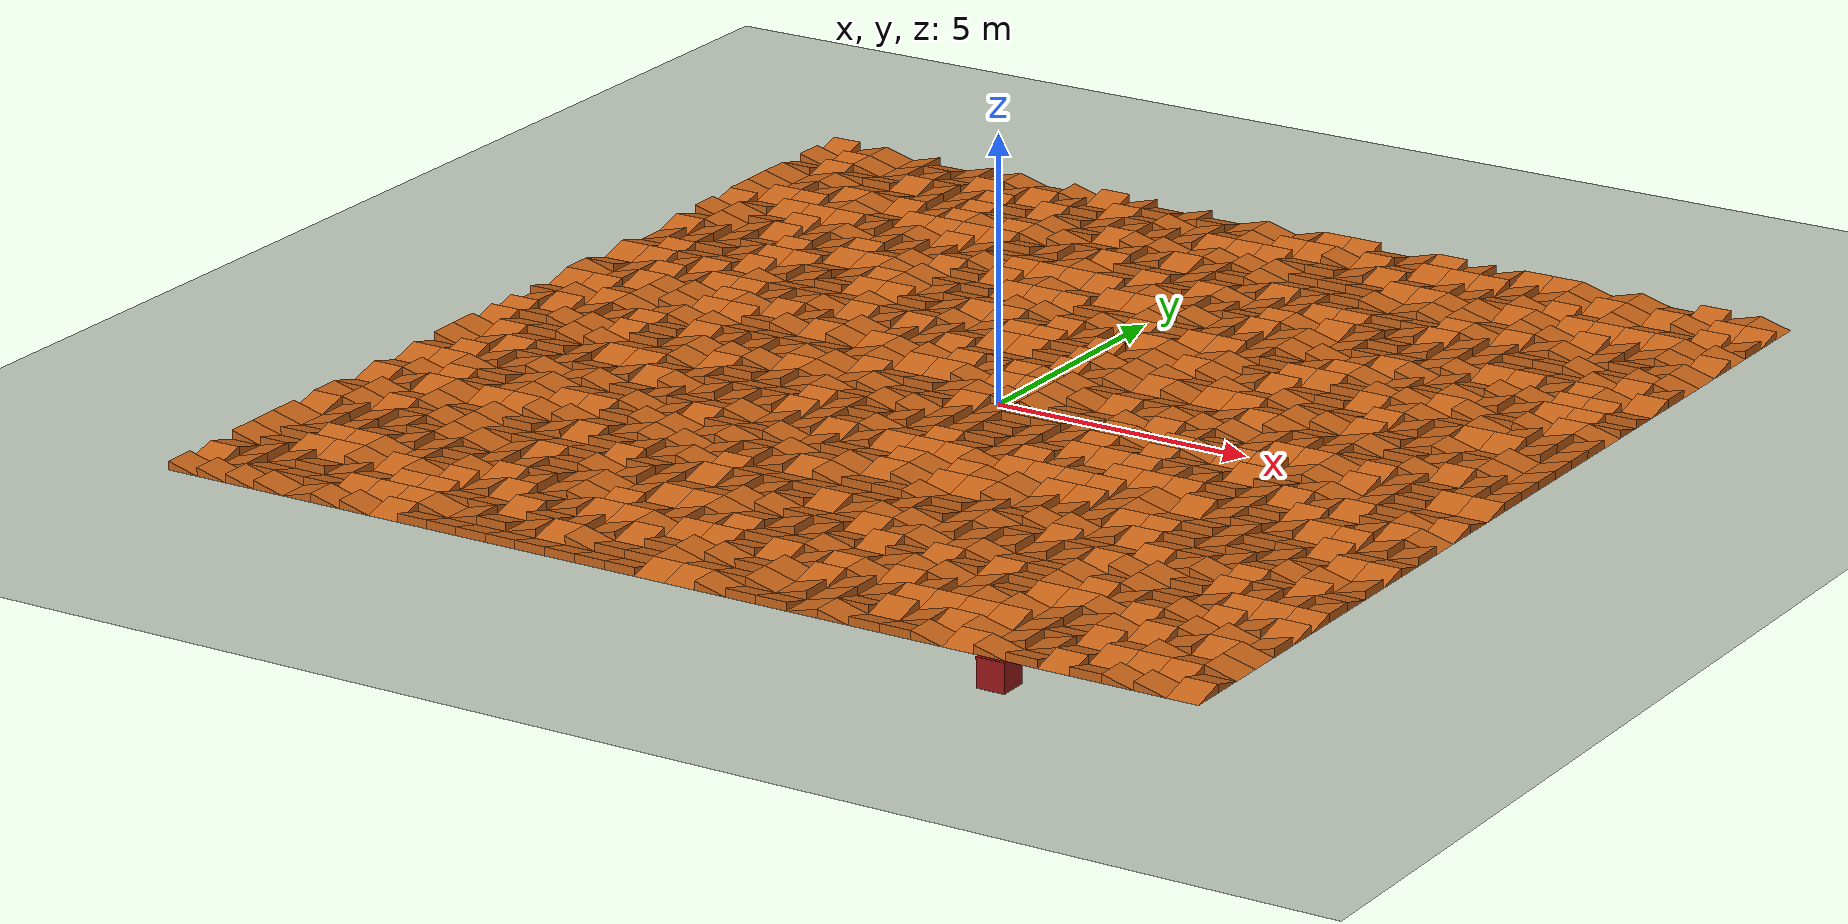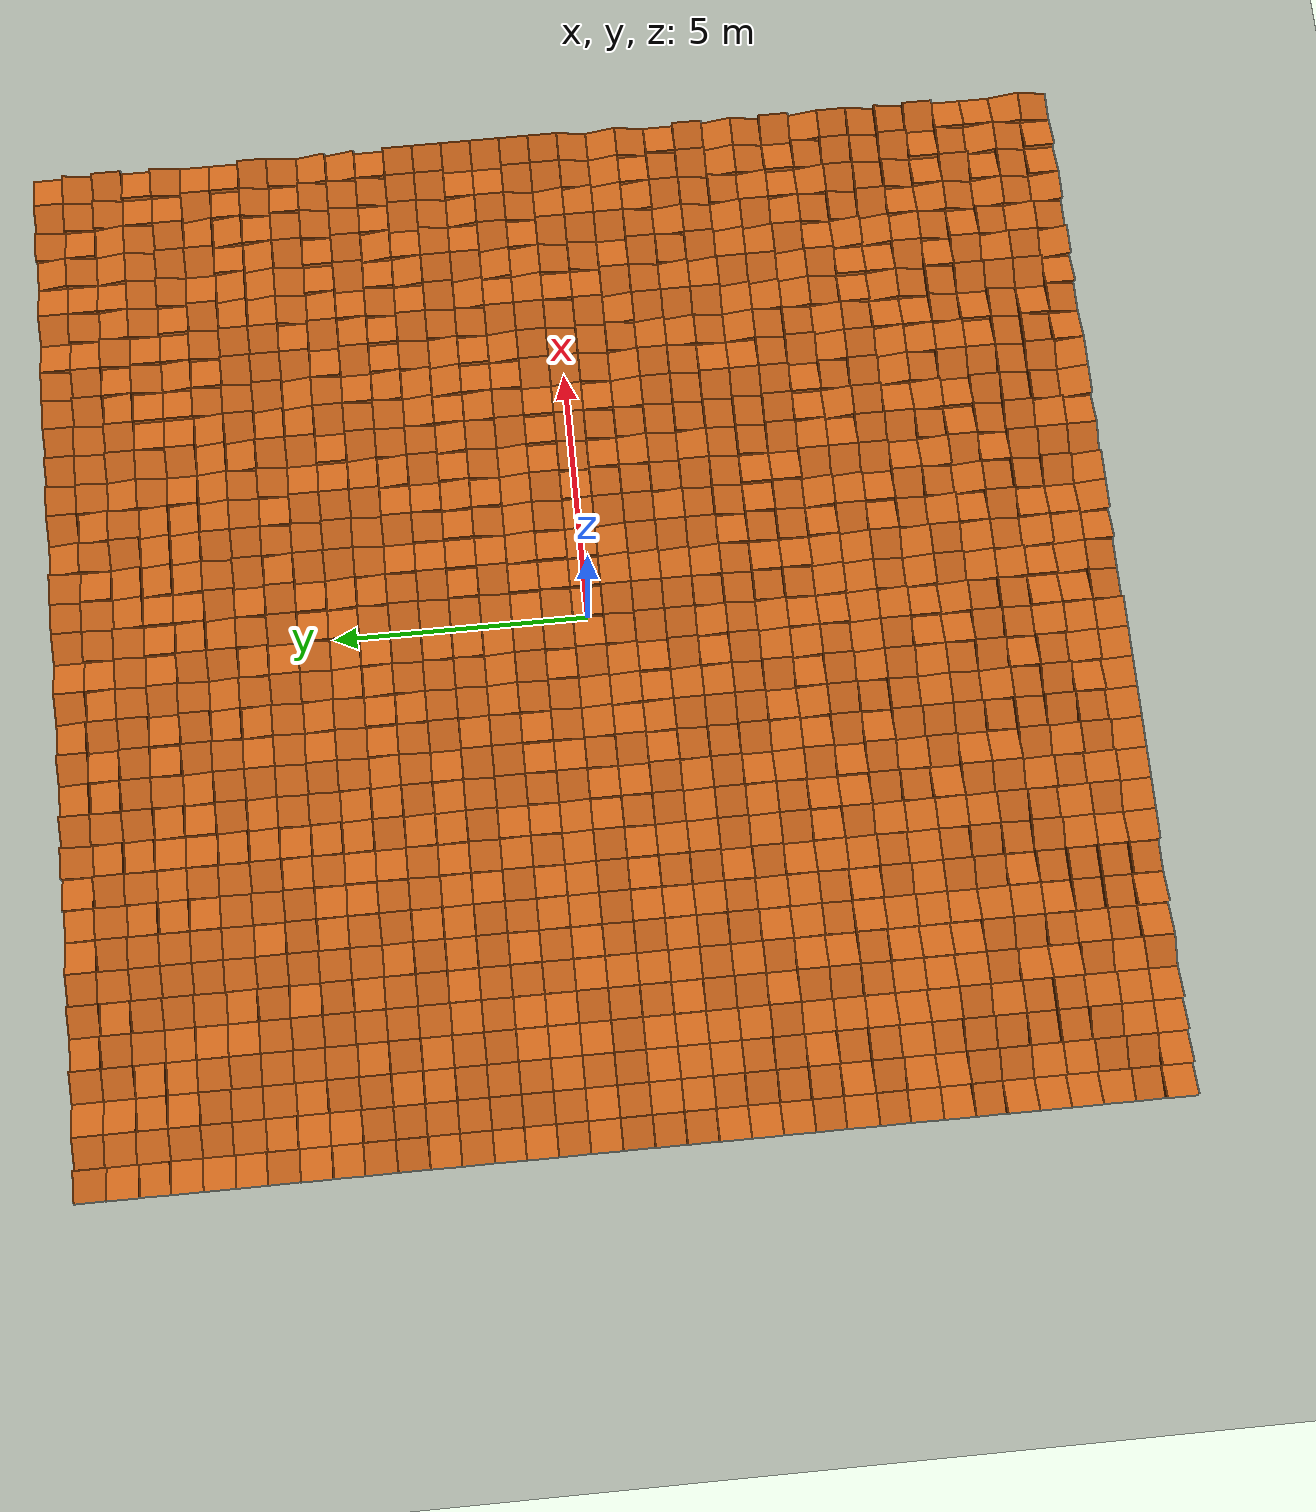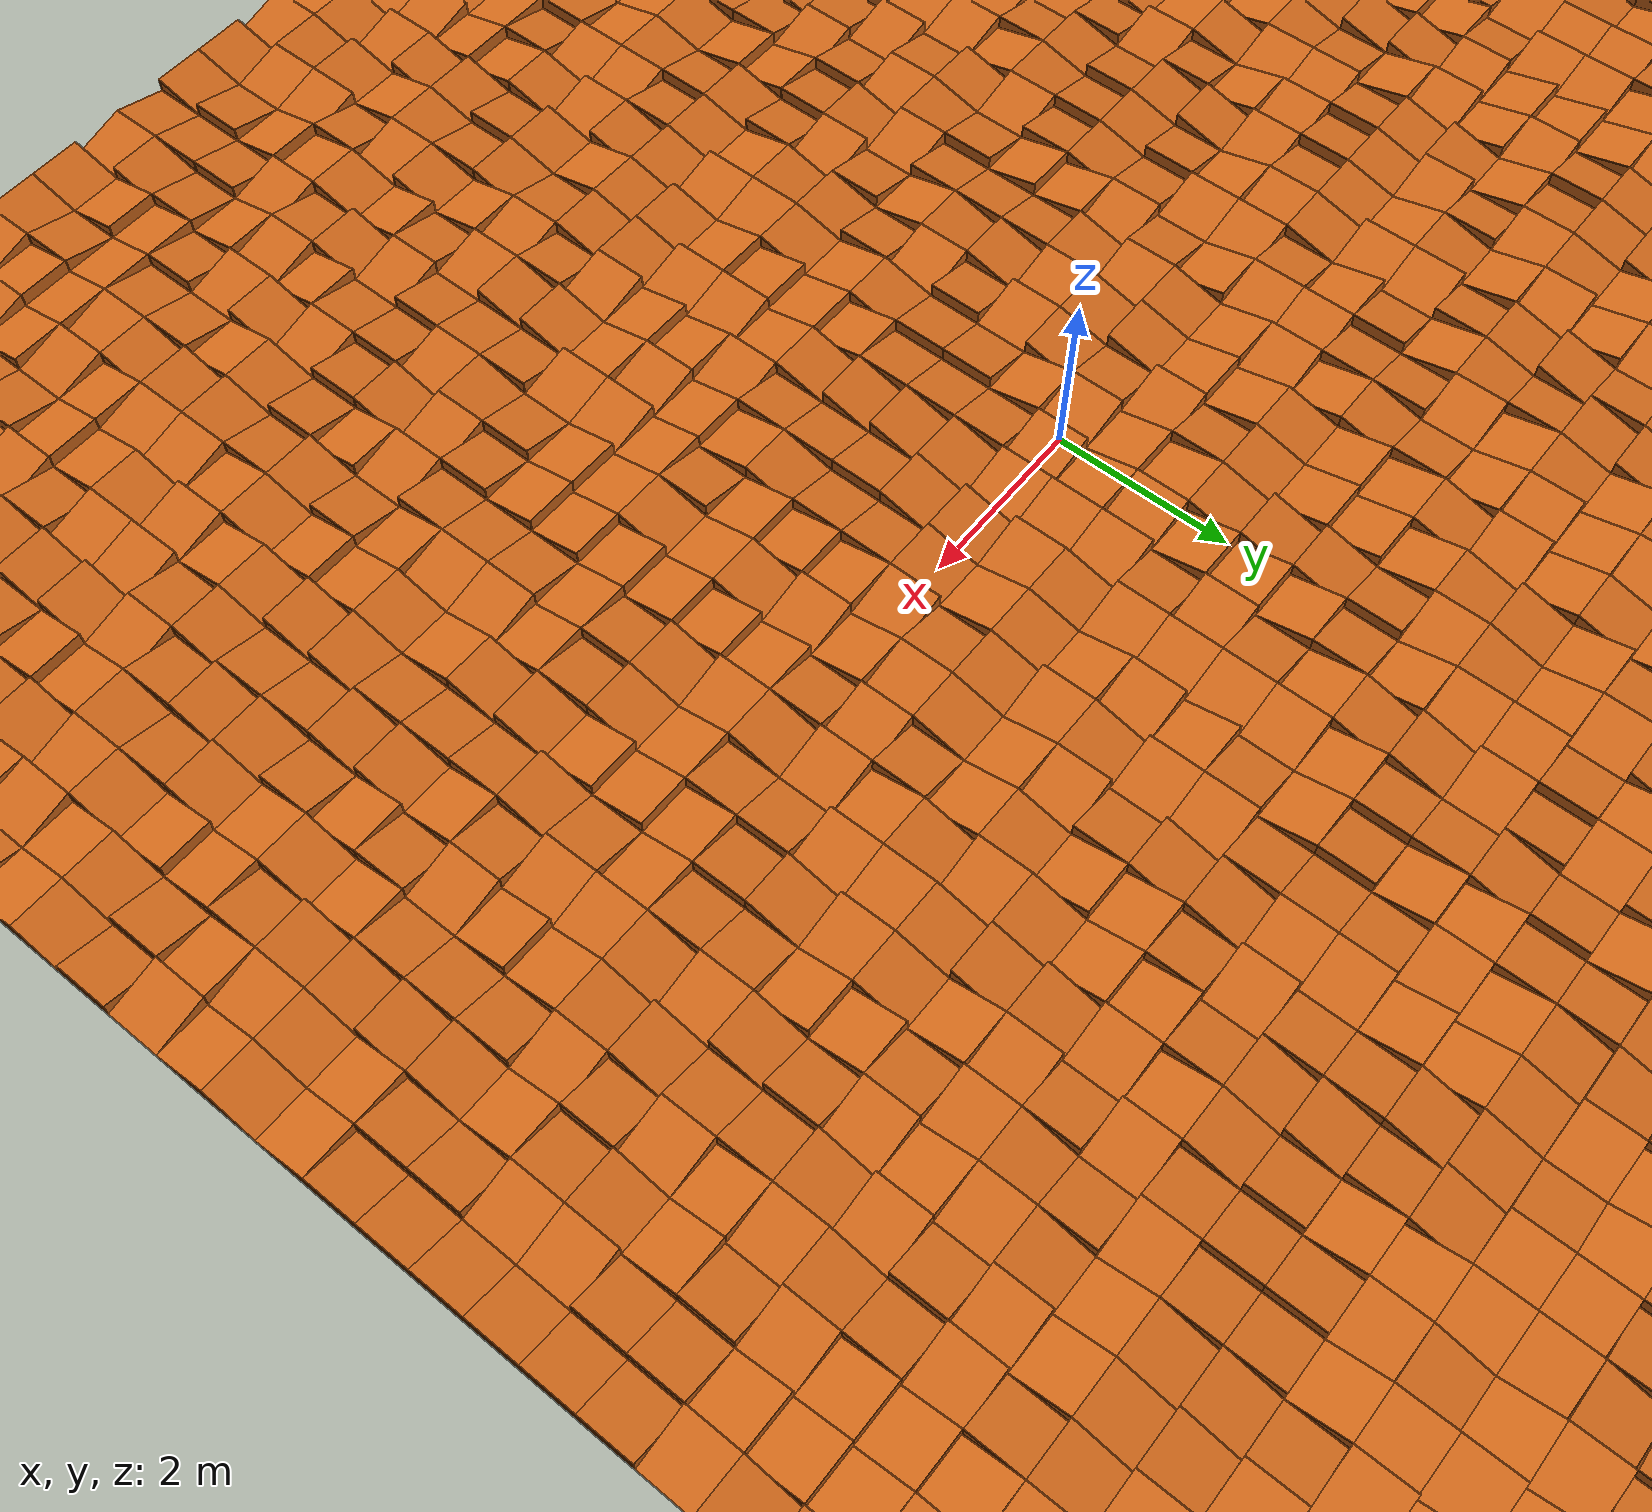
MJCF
<mujoco model="track_ramps">
  <compiler angle="radian"/>
  <!-- GENERADO desde pistas_temporal/ramps/mapa_con_rampas.xml: eulers convertidos a RADIANES (el complete compila angle="radian") y mesh apuntando a meshes/ramps/rampa.stl -->

    <asset>

        <texture type="skybox" builtin="gradient" rgb1="0.4 0.6 0.8" rgb2="0 0 0" width="512" height="512" />

        <texture name="tex_piso" type="2d" builtin="checker" rgb1="0.15 0.1 0.1" rgb2="0.08 0.05 0.05" width="512" height="512" />

        <material name="mat_piso" texture="tex_piso" texrepeat="20 20" texuniform="true" reflectance="0.1" />

        <texture name="tex_plataforma" type="2d" builtin="flat" rgb1="0.8 0.4 0.1" rgb2="0.1 0.15 0.2" width="512" height="512" />

        <material name="mat_plataforma" texture="tex_plataforma" texrepeat="40 40" texuniform="true" reflectance="0.1" />

        <mesh name="rampa_mesh" file="meshes/ramps/rampa.stl" scale="0.001 0.001 0.001" />

    </asset>

    <worldbody>

        <light directional="true" pos="0 0 10" dir="0 0 -1" />

        <geom name="suelo" type="plane" size="40 40 0.1" material="mat_piso" condim="3" friction="1 0.005 0.0001" />

        <geom name="plataforma_gigante" type="box" size="10 10 0.06" pos="0 0 0.06" material="mat_plataforma" condim="3" friction="1 0.005 0.0001" />

        <geom name="virtual_obstacle" type="box" size="0.3 0.3 0.3" pos="0 0 -5" rgba="0.85 0.1 0.1 1" condim="3" friction="1 0.005 0.0001" />

    <body name="rampa_0" pos="-9.900 -10.200 0.12" euler="1.570796 1.570796 0.000000"><geom name="rampa_geom_0" type="mesh" mesh="rampa_mesh" material="mat_plataforma" condim="3" friction="1 0.005 0.0001" /></body><body name="rampa_1" pos="-9.300 -10.200 0.12" euler="1.570796 1.570796 0.000000"><geom name="rampa_geom_1" type="mesh" mesh="rampa_mesh" material="mat_plataforma" condim="3" friction="1 0.005 0.0001" /></body><body name="rampa_2" pos="-8.700 -10.200 0.12" euler="1.570796 1.570796 0.000000"><geom name="rampa_geom_2" type="mesh" mesh="rampa_mesh" material="mat_plataforma" condim="3" friction="1 0.005 0.0001" /></body><body name="rampa_3" pos="-8.100 -10.200 0.12" euler="1.570796 1.570796 0.000000"><geom name="rampa_geom_3" type="mesh" mesh="rampa_mesh" material="mat_plataforma" condim="3" friction="1 0.005 0.0001" /></body><body name="rampa_4" pos="-7.500 -10.200 0.12" euler="1.570796 4.712389 0.000000"><geom name="rampa_geom_4" type="mesh" mesh="rampa_mesh" material="mat_plataforma" condim="3" friction="1 0.005 0.0001" /></body><body name="rampa_5" pos="-6.900 -10.200 0.12" euler="1.570796 1.570796 0.000000"><geom name="rampa_geom_5" type="mesh" mesh="rampa_mesh" material="mat_plataforma" condim="3" friction="1 0.005 0.0001" /></body><body name="rampa_6" pos="-6.300 -10.200 0.12" euler="1.570796 1.570796 0.000000"><geom name="rampa_geom_6" type="mesh" mesh="rampa_mesh" material="mat_plataforma" condim="3" friction="1 0.005 0.0001" /></body><body name="rampa_7" pos="-5.700 -10.200 0.12" euler="1.570796 0.000000 0.000000"><geom name="rampa_geom_7" type="mesh" mesh="rampa_mesh" material="mat_plataforma" condim="3" friction="1 0.005 0.0001" /></body><body name="rampa_8" pos="-5.100 -10.200 0.12" euler="1.570796 3.141593 0.000000"><geom name="rampa_geom_8" type="mesh" mesh="rampa_mesh" material="mat_plataforma" condim="3" friction="1 0.005 0.0001" /></body><body name="rampa_9" pos="-4.500 -10.200 0.12" euler="1.570796 3.141593 0.000000"><geom name="rampa_geom_9" type="mesh" mesh="rampa_mesh" material="mat_plataforma" condim="3" friction="1 0.005 0.0001" /></body><body name="rampa_10" pos="-3.900 -10.200 0.12" euler="1.570796 3.141593 0.000000"><geom name="rampa_geom_10" type="mesh" mesh="rampa_mesh" material="mat_plataforma" condim="3" friction="1 0.005 0.0001" /></body><body name="rampa_11" pos="-3.300 -10.200 0.12" euler="1.570796 3.141593 0.000000"><geom name="rampa_geom_11" type="mesh" mesh="rampa_mesh" material="mat_plataforma" condim="3" friction="1 0.005 0.0001" /></body><body name="rampa_12" pos="-2.700 -10.200 0.12" euler="1.570796 3.141593 0.000000"><geom name="rampa_geom_12" type="mesh" mesh="rampa_mesh" material="mat_plataforma" condim="3" friction="1 0.005 0.0001" /></body><body name="rampa_13" pos="-2.100 -10.200 0.12" euler="1.570796 3.141593 0.000000"><geom name="rampa_geom_13" type="mesh" mesh="rampa_mesh" material="mat_plataforma" condim="3" friction="1 0.005 0.0001" /></body><body name="rampa_14" pos="-1.500 -10.200 0.12" euler="1.570796 3.141593 0.000000"><geom name="rampa_geom_14" type="mesh" mesh="rampa_mesh" material="mat_plataforma" condim="3" friction="1 0.005 0.0001" /></body><body name="rampa_15" pos="-0.900 -10.200 0.12" euler="1.570796 3.141593 0.000000"><geom name="rampa_geom_15" type="mesh" mesh="rampa_mesh" material="mat_plataforma" condim="3" friction="1 0.005 0.0001" /></body><body name="rampa_16" pos="-0.300 -10.200 0.12" euler="1.570796 0.000000 0.000000"><geom name="rampa_geom_16" type="mesh" mesh="rampa_mesh" material="mat_plataforma" condim="3" friction="1 0.005 0.0001" /></body><body name="rampa_17" pos="0.300 -10.200 0.12" euler="1.570796 0.000000 0.000000"><geom name="rampa_geom_17" type="mesh" mesh="rampa_mesh" material="mat_plataforma" condim="3" friction="1 0.005 0.0001" /></body><body name="rampa_18" pos="0.900 -10.200 0.12" euler="1.570796 1.570796 0.000000"><geom name="rampa_geom_18" type="mesh" mesh="rampa_mesh" material="mat_plataforma" condim="3" friction="1 0.005 0.0001" /></body><body name="rampa_19" pos="1.500 -10.200 0.12" euler="1.570796 3.141593 0.000000"><geom name="rampa_geom_19" type="mesh" mesh="rampa_mesh" material="mat_plataforma" condim="3" friction="1 0.005 0.0001" /></body><body name="rampa_20" pos="2.100 -10.200 0.12" euler="1.570796 3.141593 0.000000"><geom name="rampa_geom_20" type="mesh" mesh="rampa_mesh" material="mat_plataforma" condim="3" friction="1 0.005 0.0001" /></body><body name="rampa_21" pos="2.700 -10.200 0.12" euler="1.570796 4.712389 0.000000"><geom name="rampa_geom_21" type="mesh" mesh="rampa_mesh" material="mat_plataforma" condim="3" friction="1 0.005 0.0001" /></body><body name="rampa_22" pos="3.300 -10.200 0.12" euler="1.570796 1.570796 0.000000"><geom name="rampa_geom_22" type="mesh" mesh="rampa_mesh" material="mat_plataforma" condim="3" friction="1 0.005 0.0001" /></body><body name="rampa_23" pos="3.900 -10.200 0.12" euler="1.570796 3.141593 0.000000"><geom name="rampa_geom_23" type="mesh" mesh="rampa_mesh" material="mat_plataforma" condim="3" friction="1 0.005 0.0001" /></body><body name="rampa_24" pos="4.500 -10.200 0.12" euler="1.570796 3.141593 0.000000"><geom name="rampa_geom_24" type="mesh" mesh="rampa_mesh" material="mat_plataforma" condim="3" friction="1 0.005 0.0001" /></body><body name="rampa_25" pos="5.100 -10.200 0.12" euler="1.570796 1.570796 0.000000"><geom name="rampa_geom_25" type="mesh" mesh="rampa_mesh" material="mat_plataforma" condim="3" friction="1 0.005 0.0001" /></body><body name="rampa_26" pos="5.700 -10.200 0.12" euler="1.570796 0.000000 0.000000"><geom name="rampa_geom_26" type="mesh" mesh="rampa_mesh" material="mat_plataforma" condim="3" friction="1 0.005 0.0001" /></body><body name="rampa_27" pos="6.300 -10.200 0.12" euler="1.570796 1.570796 0.000000"><geom name="rampa_geom_27" type="mesh" mesh="rampa_mesh" material="mat_plataforma" condim="3" friction="1 0.005 0.0001" /></body><body name="rampa_28" pos="6.900 -10.200 0.12" euler="1.570796 3.141593 0.000000"><geom name="rampa_geom_28" type="mesh" mesh="rampa_mesh" material="mat_plataforma" condim="3" friction="1 0.005 0.0001" /></body><body name="rampa_29" pos="7.500 -10.200 0.12" euler="1.570796 0.000000 0.000000"><geom name="rampa_geom_29" type="mesh" mesh="rampa_mesh" material="mat_plataforma" condim="3" friction="1 0.005 0.0001" /></body><body name="rampa_30" pos="8.100 -10.200 0.12" euler="1.570796 3.141593 0.000000"><geom name="rampa_geom_30" type="mesh" mesh="rampa_mesh" material="mat_plataforma" condim="3" friction="1 0.005 0.0001" /></body><body name="rampa_31" pos="8.700 -10.200 0.12" euler="1.570796 1.570796 0.000000"><geom name="rampa_geom_31" type="mesh" mesh="rampa_mesh" material="mat_plataforma" condim="3" friction="1 0.005 0.0001" /></body><body name="rampa_32" pos="9.300 -10.200 0.12" euler="1.570796 1.570796 0.000000"><geom name="rampa_geom_32" type="mesh" mesh="rampa_mesh" material="mat_plataforma" condim="3" friction="1 0.005 0.0001" /></body><body name="rampa_33" pos="9.900 -10.200 0.12" euler="1.570796 0.000000 0.000000"><geom name="rampa_geom_33" type="mesh" mesh="rampa_mesh" material="mat_plataforma" condim="3" friction="1 0.005 0.0001" /></body><body name="rampa_34" pos="-9.900 -9.600 0.12" euler="1.570796 0.000000 0.000000"><geom name="rampa_geom_34" type="mesh" mesh="rampa_mesh" material="mat_plataforma" condim="3" friction="1 0.005 0.0001" /></body><body name="rampa_35" pos="-9.300 -9.600 0.12" euler="1.570796 4.712389 0.000000"><geom name="rampa_geom_35" type="mesh" mesh="rampa_mesh" material="mat_plataforma" condim="3" friction="1 0.005 0.0001" /></body><body name="rampa_36" pos="-8.700 -9.600 0.12" euler="1.570796 3.141593 0.000000"><geom name="rampa_geom_36" type="mesh" mesh="rampa_mesh" material="mat_plataforma" condim="3" friction="1 0.005 0.0001" /></body><body name="rampa_37" pos="-8.100 -9.600 0.12" euler="1.570796 3.141593 0.000000"><geom name="rampa_geom_37" type="mesh" mesh="rampa_mesh" material="mat_plataforma" condim="3" friction="1 0.005 0.0001" /></body><body name="rampa_38" pos="-7.500 -9.600 0.12" euler="1.570796 3.141593 0.000000"><geom name="rampa_geom_38" type="mesh" mesh="rampa_mesh" material="mat_plataforma" condim="3" friction="1 0.005 0.0001" /></body><body name="rampa_39" pos="-6.900 -9.600 0.12" euler="1.570796 0.000000 0.000000"><geom name="rampa_geom_39" type="mesh" mesh="rampa_mesh" material="mat_plataforma" condim="3" friction="1 0.005 0.0001" /></body><body name="rampa_40" pos="-6.300 -9.600 0.12" euler="1.570796 0.000000 0.000000"><geom name="rampa_geom_40" type="mesh" mesh="rampa_mesh" material="mat_plataforma" condim="3" friction="1 0.005 0.0001" /></body><body name="rampa_41" pos="-5.700 -9.600 0.12" euler="1.570796 0.000000 0.000000"><geom name="rampa_geom_41" type="mesh" mesh="rampa_mesh" material="mat_plataforma" condim="3" friction="1 0.005 0.0001" /></body><body name="rampa_42" pos="-5.100 -9.600 0.12" euler="1.570796 1.570796 0.000000"><geom name="rampa_geom_42" type="mesh" mesh="rampa_mesh" material="mat_plataforma" condim="3" friction="1 0.005 0.0001" /></body><body name="rampa_43" pos="-4.500 -9.600 0.12" euler="1.570796 4.712389 0.000000"><geom name="rampa_geom_43" type="mesh" mesh="rampa_mesh" material="mat_plataforma" condim="3" friction="1 0.005 0.0001" /></body><body name="rampa_44" pos="-3.900 -9.600 0.12" euler="1.570796 3.141593 0.000000"><geom name="rampa_geom_44" type="mesh" mesh="rampa_mesh" material="mat_plataforma" condim="3" friction="1 0.005 0.0001" /></body><body name="rampa_45" pos="-3.300 -9.600 0.12" euler="1.570796 4.712389 0.000000"><geom name="rampa_geom_45" type="mesh" mesh="rampa_mesh" material="mat_plataforma" condim="3" friction="1 0.005 0.0001" /></body><body name="rampa_46" pos="-2.700 -9.600 0.12" euler="1.570796 0.000000 0.000000"><geom name="rampa_geom_46" type="mesh" mesh="rampa_mesh" material="mat_plataforma" condim="3" friction="1 0.005 0.0001" /></body><body name="rampa_47" pos="-2.100 -9.600 0.12" euler="1.570796 1.570796 0.000000"><geom name="rampa_geom_47" type="mesh" mesh="rampa_mesh" material="mat_plataforma" condim="3" friction="1 0.005 0.0001" /></body><body name="rampa_48" pos="-1.500 -9.600 0.12" euler="1.570796 3.141593 0.000000"><geom name="rampa_geom_48" type="mesh" mesh="rampa_mesh" material="mat_plataforma" condim="3" friction="1 0.005 0.0001" /></body><body name="rampa_49" pos="-0.900 -9.600 0.12" euler="1.570796 3.141593 0.000000"><geom name="rampa_geom_49" type="mesh" mesh="rampa_mesh" material="mat_plataforma" condim="3" friction="1 0.005 0.0001" /></body><body name="rampa_50" pos="-0.300 -9.600 0.12" euler="1.570796 1.570796 0.000000"><geom name="rampa_geom_50" type="mesh" mesh="rampa_mesh" material="mat_plataforma" condim="3" friction="1 0.005 0.0001" /></body><body name="rampa_51" pos="0.300 -9.600 0.12" euler="1.570796 3.141593 0.000000"><geom name="rampa_geom_51" type="mesh" mesh="rampa_mesh" material="mat_plataforma" condim="3" friction="1 0.005 0.0001" /></body><body name="rampa_52" pos="0.900 -9.600 0.12" euler="1.570796 3.141593 0.000000"><geom name="rampa_geom_52" type="mesh" mesh="rampa_mesh" material="mat_plataforma" condim="3" friction="1 0.005 0.0001" /></body><body name="rampa_53" pos="1.500 -9.600 0.12" euler="1.570796 1.570796 0.000000"><geom name="rampa_geom_53" type="mesh" mesh="rampa_mesh" material="mat_plataforma" condim="3" friction="1 0.005 0.0001" /></body><body name="rampa_54" pos="2.100 -9.600 0.12" euler="1.570796 4.712389 0.000000"><geom name="rampa_geom_54" type="mesh" mesh="rampa_mesh" material="mat_plataforma" condim="3" friction="1 0.005 0.0001" /></body><body name="rampa_55" pos="2.700 -9.600 0.12" euler="1.570796 4.712389 0.000000"><geom name="rampa_geom_55" type="mesh" mesh="rampa_mesh" material="mat_plataforma" condim="3" friction="1 0.005 0.0001" /></body><body name="rampa_56" pos="3.300 -9.600 0.12" euler="1.570796 3.141593 0.000000"><geom name="rampa_geom_56" type="mesh" mesh="rampa_mesh" material="mat_plataforma" condim="3" friction="1 0.005 0.0001" /></body><body name="rampa_57" pos="3.900 -9.600 0.12" euler="1.570796 0.000000 0.000000"><geom name="rampa_geom_57" type="mesh" mesh="rampa_mesh" material="mat_plataforma" condim="3" friction="1 0.005 0.0001" /></body><body name="rampa_58" pos="4.500 -9.600 0.12" euler="1.570796 4.712389 0.000000"><geom name="rampa_geom_58" type="mesh" mesh="rampa_mesh" material="mat_plataforma" condim="3" friction="1 0.005 0.0001" /></body><body name="rampa_59" pos="5.100 -9.600 0.12" euler="1.570796 0.000000 0.000000"><geom name="rampa_geom_59" type="mesh" mesh="rampa_mesh" material="mat_plataforma" condim="3" friction="1 0.005 0.0001" /></body><body name="rampa_60" pos="5.700 -9.600 0.12" euler="1.570796 1.570796 0.000000"><geom name="rampa_geom_60" type="mesh" mesh="rampa_mesh" material="mat_plataforma" condim="3" friction="1 0.005 0.0001" /></body><body name="rampa_61" pos="6.300 -9.600 0.12" euler="1.570796 4.712389 0.000000"><geom name="rampa_geom_61" type="mesh" mesh="rampa_mesh" material="mat_plataforma" condim="3" friction="1 0.005 0.0001" /></body><body name="rampa_62" pos="6.900 -9.600 0.12" euler="1.570796 4.712389 0.000000"><geom name="rampa_geom_62" type="mesh" mesh="rampa_mesh" material="mat_plataforma" condim="3" friction="1 0.005 0.0001" /></body><body name="rampa_63" pos="7.500 -9.600 0.12" euler="1.570796 3.141593 0.000000"><geom name="rampa_geom_63" type="mesh" mesh="rampa_mesh" material="mat_plataforma" condim="3" friction="1 0.005 0.0001" /></body><body name="rampa_64" pos="8.100 -9.600 0.12" euler="1.570796 0.000000 0.000000"><geom name="rampa_geom_64" type="mesh" mesh="rampa_mesh" material="mat_plataforma" condim="3" friction="1 0.005 0.0001" /></body><body name="rampa_65" pos="8.700 -9.600 0.12" euler="1.570796 0.000000 0.000000"><geom name="rampa_geom_65" type="mesh" mesh="rampa_mesh" material="mat_plataforma" condim="3" friction="1 0.005 0.0001" /></body><body name="rampa_66" pos="9.300 -9.600 0.12" euler="1.570796 0.000000 0.000000"><geom name="rampa_geom_66" type="mesh" mesh="rampa_mesh" material="mat_plataforma" condim="3" friction="1 0.005 0.0001" /></body><body name="rampa_67" pos="9.900 -9.600 0.12" euler="1.570796 3.141593 0.000000"><geom name="rampa_geom_67" type="mesh" mesh="rampa_mesh" material="mat_plataforma" condim="3" friction="1 0.005 0.0001" /></body><body name="rampa_68" pos="-9.900 -9.000 0.12" euler="1.570796 3.141593 0.000000"><geom name="rampa_geom_68" type="mesh" mesh="rampa_mesh" material="mat_plataforma" condim="3" friction="1 0.005 0.0001" /></body><body name="rampa_69" pos="-9.300 -9.000 0.12" euler="1.570796 4.712389 0.000000"><geom name="rampa_geom_69" type="mesh" mesh="rampa_mesh" material="mat_plataforma" condim="3" friction="1 0.005 0.0001" /></body><body name="rampa_70" pos="-8.700 -9.000 0.12" euler="1.570796 4.712389 0.000000"><geom name="rampa_geom_70" type="mesh" mesh="rampa_mesh" material="mat_plataforma" condim="3" friction="1 0.005 0.0001" /></body><body name="rampa_71" pos="-8.100 -9.000 0.12" euler="1.570796 3.141593 0.000000"><geom name="rampa_geom_71" type="mesh" mesh="rampa_mesh" material="mat_plataforma" condim="3" friction="1 0.005 0.0001" /></body><body name="rampa_72" pos="-7.500 -9.000 0.12" euler="1.570796 4.712389 0.000000"><geom name="rampa_geom_72" type="mesh" mesh="rampa_mesh" material="mat_plataforma" condim="3" friction="1 0.005 0.0001" /></body><body name="rampa_73" pos="-6.900 -9.000 0.12" euler="1.570796 3.141593 0.000000"><geom name="rampa_geom_73" type="mesh" mesh="rampa_mesh" material="mat_plataforma" condim="3" friction="1 0.005 0.0001" /></body><body name="rampa_74" pos="-6.300 -9.000 0.12" euler="1.570796 0.000000 0.000000"><geom name="rampa_geom_74" type="mesh" mesh="rampa_mesh" material="mat_plataforma" condim="3" friction="1 0.005 0.0001" /></body><body name="rampa_75" pos="-5.700 -9.000 0.12" euler="1.570796 0.000000 0.000000"><geom name="rampa_geom_75" type="mesh" mesh="rampa_mesh" material="mat_plataforma" condim="3" friction="1 0.005 0.0001" /></body><body name="rampa_76" pos="-5.100 -9.000 0.12" euler="1.570796 3.141593 0.000000"><geom name="rampa_geom_76" type="mesh" mesh="rampa_mesh" material="mat_plataforma" condim="3" friction="1 0.005 0.0001" /></body><body name="rampa_77" pos="-4.500 -9.000 0.12" euler="1.570796 3.141593 0.000000"><geom name="rampa_geom_77" type="mesh" mesh="rampa_mesh" material="mat_plataforma" condim="3" friction="1 0.005 0.0001" /></body><body name="rampa_78" pos="-3.900 -9.000 0.12" euler="1.570796 0.000000 0.000000"><geom name="rampa_geom_78" type="mesh" mesh="rampa_mesh" material="mat_plataforma" condim="3" friction="1 0.005 0.0001" /></body><body name="rampa_79" pos="-3.300 -9.000 0.12" euler="1.570796 3.141593 0.000000"><geom name="rampa_geom_79" type="mesh" mesh="rampa_mesh" material="mat_plataforma" condim="3" friction="1 0.005 0.0001" /></body><body name="rampa_80" pos="-2.700 -9.000 0.12" euler="1.570796 4.712389 0.000000"><geom name="rampa_geom_80" type="mesh" mesh="rampa_mesh" material="mat_plataforma" condim="3" friction="1 0.005 0.0001" /></body><body name="rampa_81" pos="-2.100 -9.000 0.12" euler="1.570796 4.712389 0.000000"><geom name="rampa_geom_81" type="mesh" mesh="rampa_mesh" material="mat_plataforma" condim="3" friction="1 0.005 0.0001" /></body><body name="rampa_82" pos="-1.500 -9.000 0.12" euler="1.570796 0.000000 0.000000"><geom name="rampa_geom_82" type="mesh" mesh="rampa_mesh" material="mat_plataforma" condim="3" friction="1 0.005 0.0001" /></body><body name="rampa_83" pos="-0.900 -9.000 0.12" euler="1.570796 3.141593 0.000000"><geom name="rampa_geom_83" type="mesh" mesh="rampa_mesh" material="mat_plataforma" condim="3" friction="1 0.005 0.0001" /></body><body name="rampa_84" pos="-0.300 -9.000 0.12" euler="1.570796 1.570796 0.000000"><geom name="rampa_geom_84" type="mesh" mesh="rampa_mesh" material="mat_plataforma" condim="3" friction="1 0.005 0.0001" /></body><body name="rampa_85" pos="0.300 -9.000 0.12" euler="1.570796 1.570796 0.000000"><geom name="rampa_geom_85" type="mesh" mesh="rampa_mesh" material="mat_plataforma" condim="3" friction="1 0.005 0.0001" /></body><body name="rampa_86" pos="0.900 -9.000 0.12" euler="1.570796 3.141593 0.000000"><geom name="rampa_geom_86" type="mesh" mesh="rampa_mesh" material="mat_plataforma" condim="3" friction="1 0.005 0.0001" /></body><body name="rampa_87" pos="1.500 -9.000 0.12" euler="1.570796 1.570796 0.000000"><geom name="rampa_geom_87" type="mesh" mesh="rampa_mesh" material="mat_plataforma" condim="3" friction="1 0.005 0.0001" /></body><body name="rampa_88" pos="2.100 -9.000 0.12" euler="1.570796 0.000000 0.000000"><geom name="rampa_geom_88" type="mesh" mesh="rampa_mesh" material="mat_plataforma" condim="3" friction="1 0.005 0.0001" /></body><body name="rampa_89" pos="2.700 -9.000 0.12" euler="1.570796 4.712389 0.000000"><geom name="rampa_geom_89" type="mesh" mesh="rampa_mesh" material="mat_plataforma" condim="3" friction="1 0.005 0.0001" /></body><body name="rampa_90" pos="3.300 -9.000 0.12" euler="1.570796 4.712389 0.000000"><geom name="rampa_geom_90" type="mesh" mesh="rampa_mesh" material="mat_plataforma" condim="3" friction="1 0.005 0.0001" /></body><body name="rampa_91" pos="3.900 -9.000 0.12" euler="1.570796 0.000000 0.000000"><geom name="rampa_geom_91" type="mesh" mesh="rampa_mesh" material="mat_plataforma" condim="3" friction="1 0.005 0.0001" /></body><body name="rampa_92" pos="4.500 -9.000 0.12" euler="1.570796 0.000000 0.000000"><geom name="rampa_geom_92" type="mesh" mesh="rampa_mesh" material="mat_plataforma" condim="3" friction="1 0.005 0.0001" /></body><body name="rampa_93" pos="5.100 -9.000 0.12" euler="1.570796 0.000000 0.000000"><geom name="rampa_geom_93" type="mesh" mesh="rampa_mesh" material="mat_plataforma" condim="3" friction="1 0.005 0.0001" /></body><body name="rampa_94" pos="5.700 -9.000 0.12" euler="1.570796 0.000000 0.000000"><geom name="rampa_geom_94" type="mesh" mesh="rampa_mesh" material="mat_plataforma" condim="3" friction="1 0.005 0.0001" /></body><body name="rampa_95" pos="6.300 -9.000 0.12" euler="1.570796 4.712389 0.000000"><geom name="rampa_geom_95" type="mesh" mesh="rampa_mesh" material="mat_plataforma" condim="3" friction="1 0.005 0.0001" /></body><body name="rampa_96" pos="6.900 -9.000 0.12" euler="1.570796 3.141593 0.000000"><geom name="rampa_geom_96" type="mesh" mesh="rampa_mesh" material="mat_plataforma" condim="3" friction="1 0.005 0.0001" /></body><body name="rampa_97" pos="7.500 -9.000 0.12" euler="1.570796 0.000000 0.000000"><geom name="rampa_geom_97" type="mesh" mesh="rampa_mesh" material="mat_plataforma" condim="3" friction="1 0.005 0.0001" /></body><body name="rampa_98" pos="8.100 -9.000 0.12" euler="1.570796 3.141593 0.000000"><geom name="rampa_geom_98" type="mesh" mesh="rampa_mesh" material="mat_plataforma" condim="3" friction="1 0.005 0.0001" /></body><body name="rampa_99" pos="8.700 -9.000 0.12" euler="1.570796 1.570796 0.000000"><geom name="rampa_geom_99" type="mesh" mesh="rampa_mesh" material="mat_plataforma" condim="3" friction="1 0.005 0.0001" /></body><body name="rampa_100" pos="9.300 -9.000 0.12" euler="1.570796 3.141593 0.000000"><geom name="rampa_geom_100" type="mesh" mesh="rampa_mesh" material="mat_plataforma" condim="3" friction="1 0.005 0.0001" /></body><body name="rampa_101" pos="9.900 -9.000 0.12" euler="1.570796 1.570796 0.000000"><geom name="rampa_geom_101" type="mesh" mesh="rampa_mesh" material="mat_plataforma" condim="3" friction="1 0.005 0.0001" /></body><body name="rampa_102" pos="-9.900 -8.400 0.12" euler="1.570796 1.570796 0.000000"><geom name="rampa_geom_102" type="mesh" mesh="rampa_mesh" material="mat_plataforma" condim="3" friction="1 0.005 0.0001" /></body><body name="rampa_103" pos="-9.300 -8.400 0.12" euler="1.570796 3.141593 0.000000"><geom name="rampa_geom_103" type="mesh" mesh="rampa_mesh" material="mat_plataforma" condim="3" friction="1 0.005 0.0001" /></body><body name="rampa_104" pos="-8.700 -8.400 0.12" euler="1.570796 0.000000 0.000000"><geom name="rampa_geom_104" type="mesh" mesh="rampa_mesh" material="mat_plataforma" condim="3" friction="1 0.005 0.0001" /></body><body name="rampa_105" pos="-8.100 -8.400 0.12" euler="1.570796 0.000000 0.000000"><geom name="rampa_geom_105" type="mesh" mesh="rampa_mesh" material="mat_plataforma" condim="3" friction="1 0.005 0.0001" /></body><body name="rampa_106" pos="-7.500 -8.400 0.12" euler="1.570796 1.570796 0.000000"><geom name="rampa_geom_106" type="mesh" mesh="rampa_mesh" material="mat_plataforma" condim="3" friction="1 0.005 0.0001" /></body><body name="rampa_107" pos="-6.900 -8.400 0.12" euler="1.570796 0.000000 0.000000"><geom name="rampa_geom_107" type="mesh" mesh="rampa_mesh" material="mat_plataforma" condim="3" friction="1 0.005 0.0001" /></body><body name="rampa_108" pos="-6.300 -8.400 0.12" euler="1.570796 1.570796 0.000000"><geom name="rampa_geom_108" type="mesh" mesh="rampa_mesh" material="mat_plataforma" condim="3" friction="1 0.005 0.0001" /></body><body name="rampa_109" pos="-5.700 -8.400 0.12" euler="1.570796 0.000000 0.000000"><geom name="rampa_geom_109" type="mesh" mesh="rampa_mesh" material="mat_plataforma" condim="3" friction="1 0.005 0.0001" /></body><body name="rampa_110" pos="-5.100 -8.400 0.12" euler="1.570796 4.712389 0.000000"><geom name="rampa_geom_110" type="mesh" mesh="rampa_mesh" material="mat_plataforma" condim="3" friction="1 0.005 0.0001" /></body><body name="rampa_111" pos="-4.500 -8.400 0.12" euler="1.570796 0.000000 0.000000"><geom name="rampa_geom_111" type="mesh" mesh="rampa_mesh" material="mat_plataforma" condim="3" friction="1 0.005 0.0001" /></body><body name="rampa_112" pos="-3.900 -8.400 0.12" euler="1.570796 3.141593 0.000000"><geom name="rampa_geom_112" type="mesh" mesh="rampa_mesh" material="mat_plataforma" condim="3" friction="1 0.005 0.0001" /></body><body name="rampa_113" pos="-3.300 -8.400 0.12" euler="1.570796 4.712389 0.000000"><geom name="rampa_geom_113" type="mesh" mesh="rampa_mesh" material="mat_plataforma" condim="3" friction="1 0.005 0.0001" /></body><body name="rampa_114" pos="-2.700 -8.400 0.12" euler="1.570796 0.000000 0.000000"><geom name="rampa_geom_114" type="mesh" mesh="rampa_mesh" material="mat_plataforma" condim="3" friction="1 0.005 0.0001" /></body><body name="rampa_115" pos="-2.100 -8.400 0.12" euler="1.570796 0.000000 0.000000"><geom name="rampa_geom_115" type="mesh" mesh="rampa_mesh" material="mat_plataforma" condim="3" friction="1 0.005 0.0001" /></body><body name="rampa_116" pos="-1.500 -8.400 0.12" euler="1.570796 1.570796 0.000000"><geom name="rampa_geom_116" type="mesh" mesh="rampa_mesh" material="mat_plataforma" condim="3" friction="1 0.005 0.0001" /></body><body name="rampa_117" pos="-0.900 -8.400 0.12" euler="1.570796 0.000000 0.000000"><geom name="rampa_geom_117" type="mesh" mesh="rampa_mesh" material="mat_plataforma" condim="3" friction="1 0.005 0.0001" /></body><body name="rampa_118" pos="-0.300 -8.400 0.12" euler="1.570796 0.000000 0.000000"><geom name="rampa_geom_118" type="mesh" mesh="rampa_mesh" material="mat_plataforma" condim="3" friction="1 0.005 0.0001" /></body><body name="rampa_119" pos="0.300 -8.400 0.12" euler="1.570796 3.141593 0.000000"><geom name="rampa_geom_119" type="mesh" mesh="rampa_mesh" material="mat_plataforma" condim="3" friction="1 0.005 0.0001" /></body><body name="rampa_120" pos="0.900 -8.400 0.12" euler="1.570796 0.000000 0.000000"><geom name="rampa_geom_120" type="mesh" mesh="rampa_mesh" material="mat_plataforma" condim="3" friction="1 0.005 0.0001" /></body><body name="rampa_121" pos="1.500 -8.400 0.12" euler="1.570796 4.712389 0.000000"><geom name="rampa_geom_121" type="mesh" mesh="rampa_mesh" material="mat_plataforma" condim="3" friction="1 0.005 0.0001" /></body><body name="rampa_122" pos="2.100 -8.400 0.12" euler="1.570796 0.000000 0.000000"><geom name="rampa_geom_122" type="mesh" mesh="rampa_mesh" material="mat_plataforma" condim="3" friction="1 0.005 0.0001" /></body><body name="rampa_123" pos="2.700 -8.400 0.12" euler="1.570796 1.570796 0.000000"><geom name="rampa_geom_123" type="mesh" mesh="rampa_mesh" material="mat_plataforma" condim="3" friction="1 0.005 0.0001" /></body><body name="rampa_124" pos="3.300 -8.400 0.12" euler="1.570796 0.000000 0.000000"><geom name="rampa_geom_124" type="mesh" mesh="rampa_mesh" material="mat_plataforma" condim="3" friction="1 0.005 0.0001" /></body><body name="rampa_125" pos="3.900 -8.400 0.12" euler="1.570796 4.712389 0.000000"><geom name="rampa_geom_125" type="mesh" mesh="rampa_mesh" material="mat_plataforma" condim="3" friction="1 0.005 0.0001" /></body><body name="rampa_126" pos="4.500 -8.400 0.12" euler="1.570796 4.712389 0.000000"><geom name="rampa_geom_126" type="mesh" mesh="rampa_mesh" material="mat_plataforma" condim="3" friction="1 0.005 0.0001" /></body><body name="rampa_127" pos="5.100 -8.400 0.12" euler="1.570796 1.570796 0.000000"><geom name="rampa_geom_127" type="mesh" mesh="rampa_mesh" material="mat_plataforma" condim="3" friction="1 0.005 0.0001" /></body><body name="rampa_128" pos="5.700 -8.400 0.12" euler="1.570796 1.570796 0.000000"><geom name="rampa_geom_128" type="mesh" mesh="rampa_mesh" material="mat_plataforma" condim="3" friction="1 0.005 0.0001" /></body><body name="rampa_129" pos="6.300 -8.400 0.12" euler="1.570796 4.712389 0.000000"><geom name="rampa_geom_129" type="mesh" mesh="rampa_mesh" material="mat_plataforma" condim="3" friction="1 0.005 0.0001" /></body><body name="rampa_130" pos="6.900 -8.400 0.12" euler="1.570796 4.712389 0.000000"><geom name="rampa_geom_130" type="mesh" mesh="rampa_mesh" material="mat_plataforma" condim="3" friction="1 0.005 0.0001" /></body><body name="rampa_131" pos="7.500 -8.400 0.12" euler="1.570796 1.570796 0.000000"><geom name="rampa_geom_131" type="mesh" mesh="rampa_mesh" material="mat_plataforma" condim="3" friction="1 0.005 0.0001" /></body><body name="rampa_132" pos="8.100 -8.400 0.12" euler="1.570796 0.000000 0.000000"><geom name="rampa_geom_132" type="mesh" mesh="rampa_mesh" material="mat_plataforma" condim="3" friction="1 0.005 0.0001" /></body><body name="rampa_133" pos="8.700 -8.400 0.12" euler="1.570796 4.712389 0.000000"><geom name="rampa_geom_133" type="mesh" mesh="rampa_mesh" material="mat_plataforma" condim="3" friction="1 0.005 0.0001" /></body><body name="rampa_134" pos="9.300 -8.400 0.12" euler="1.570796 0.000000 0.000000"><geom name="rampa_geom_134" type="mesh" mesh="rampa_mesh" material="mat_plataforma" condim="3" friction="1 0.005 0.0001" /></body><body name="rampa_135" pos="9.900 -8.400 0.12" euler="1.570796 1.570796 0.000000"><geom name="rampa_geom_135" type="mesh" mesh="rampa_mesh" material="mat_plataforma" condim="3" friction="1 0.005 0.0001" /></body><body name="rampa_136" pos="-9.900 -7.800 0.12" euler="1.570796 1.570796 0.000000"><geom name="rampa_geom_136" type="mesh" mesh="rampa_mesh" material="mat_plataforma" condim="3" friction="1 0.005 0.0001" /></body><body name="rampa_137" pos="-9.300 -7.800 0.12" euler="1.570796 3.141593 0.000000"><geom name="rampa_geom_137" type="mesh" mesh="rampa_mesh" material="mat_plataforma" condim="3" friction="1 0.005 0.0001" /></body><body name="rampa_138" pos="-8.700 -7.800 0.12" euler="1.570796 0.000000 0.000000"><geom name="rampa_geom_138" type="mesh" mesh="rampa_mesh" material="mat_plataforma" condim="3" friction="1 0.005 0.0001" /></body><body name="rampa_139" pos="-8.100 -7.800 0.12" euler="1.570796 0.000000 0.000000"><geom name="rampa_geom_139" type="mesh" mesh="rampa_mesh" material="mat_plataforma" condim="3" friction="1 0.005 0.0001" /></body><body name="rampa_140" pos="-7.500 -7.800 0.12" euler="1.570796 1.570796 0.000000"><geom name="rampa_geom_140" type="mesh" mesh="rampa_mesh" material="mat_plataforma" condim="3" friction="1 0.005 0.0001" /></body><body name="rampa_141" pos="-6.900 -7.800 0.12" euler="1.570796 4.712389 0.000000"><geom name="rampa_geom_141" type="mesh" mesh="rampa_mesh" material="mat_plataforma" condim="3" friction="1 0.005 0.0001" /></body><body name="rampa_142" pos="-6.300 -7.800 0.12" euler="1.570796 3.141593 0.000000"><geom name="rampa_geom_142" type="mesh" mesh="rampa_mesh" material="mat_plataforma" condim="3" friction="1 0.005 0.0001" /></body><body name="rampa_143" pos="-5.700 -7.800 0.12" euler="1.570796 1.570796 0.000000"><geom name="rampa_geom_143" type="mesh" mesh="rampa_mesh" material="mat_plataforma" condim="3" friction="1 0.005 0.0001" /></body><body name="rampa_144" pos="-5.100 -7.800 0.12" euler="1.570796 0.000000 0.000000"><geom name="rampa_geom_144" type="mesh" mesh="rampa_mesh" material="mat_plataforma" condim="3" friction="1 0.005 0.0001" /></body><body name="rampa_145" pos="-4.500 -7.800 0.12" euler="1.570796 4.712389 0.000000"><geom name="rampa_geom_145" type="mesh" mesh="rampa_mesh" material="mat_plataforma" condim="3" friction="1 0.005 0.0001" /></body><body name="rampa_146" pos="-3.900 -7.800 0.12" euler="1.570796 4.712389 0.000000"><geom name="rampa_geom_146" type="mesh" mesh="rampa_mesh" material="mat_plataforma" condim="3" friction="1 0.005 0.0001" /></body><body name="rampa_147" pos="-3.300 -7.800 0.12" euler="1.570796 1.570796 0.000000"><geom name="rampa_geom_147" type="mesh" mesh="rampa_mesh" material="mat_plataforma" condim="3" friction="1 0.005 0.0001" /></body><body name="rampa_148" pos="-2.700 -7.800 0.12" euler="1.570796 0.000000 0.000000"><geom name="rampa_geom_148" type="mesh" mesh="rampa_mesh" material="mat_plataforma" condim="3" friction="1 0.005 0.0001" /></body><body name="rampa_149" pos="-2.100 -7.800 0.12" euler="1.570796 3.141593 0.000000"><geom name="rampa_geom_149" type="mesh" mesh="rampa_mesh" material="mat_plataforma" condim="3" friction="1 0.005 0.0001" /></body><body name="rampa_150" pos="-1.500 -7.800 0.12" euler="1.570796 4.712389 0.000000"><geom name="rampa_geom_150" type="mesh" mesh="rampa_mesh" material="mat_plataforma" condim="3" friction="1 0.005 0.0001" /></body><body name="rampa_151" pos="-0.900 -7.800 0.12" euler="1.570796 4.712389 0.000000"><geom name="rampa_geom_151" type="mesh" mesh="rampa_mesh" material="mat_plataforma" condim="3" friction="1 0.005 0.0001" /></body><body name="rampa_152" pos="-0.300 -7.800 0.12" euler="1.570796 0.000000 0.000000"><geom name="rampa_geom_152" type="mesh" mesh="rampa_mesh" material="mat_plataforma" condim="3" friction="1 0.005 0.0001" /></body><body name="rampa_153" pos="0.300 -7.800 0.12" euler="1.570796 3.141593 0.000000"><geom name="rampa_geom_153" type="mesh" mesh="rampa_mesh" material="mat_plataforma" condim="3" friction="1 0.005 0.0001" /></body><body name="rampa_154" pos="0.900 -7.800 0.12" euler="1.570796 3.141593 0.000000"><geom name="rampa_geom_154" type="mesh" mesh="rampa_mesh" material="mat_plataforma" condim="3" friction="1 0.005 0.0001" /></body><body name="rampa_155" pos="1.500 -7.800 0.12" euler="1.570796 1.570796 0.000000"><geom name="rampa_geom_155" type="mesh" mesh="rampa_mesh" material="mat_plataforma" condim="3" friction="1 0.005 0.0001" /></body><body name="rampa_156" pos="2.100 -7.800 0.12" euler="1.570796 3.141593 0.000000"><geom name="rampa_geom_156" type="mesh" mesh="rampa_mesh" material="mat_plataforma" condim="3" friction="1 0.005 0.0001" /></body><body name="rampa_157" pos="2.700 -7.800 0.12" euler="1.570796 4.712389 0.000000"><geom name="rampa_geom_157" type="mesh" mesh="rampa_mesh" material="mat_plataforma" condim="3" friction="1 0.005 0.0001" /></body><body name="rampa_158" pos="3.300 -7.800 0.12" euler="1.570796 1.570796 0.000000"><geom name="rampa_geom_158" type="mesh" mesh="rampa_mesh" material="mat_plataforma" condim="3" friction="1 0.005 0.0001" /></body><body name="rampa_159" pos="3.900 -7.800 0.12" euler="1.570796 1.570796 0.000000"><geom name="rampa_geom_159" type="mesh" mesh="rampa_mesh" material="mat_plataforma" condim="3" friction="1 0.005 0.0001" /></body><body name="rampa_160" pos="4.500 -7.800 0.12" euler="1.570796 4.712389 0.000000"><geom name="rampa_geom_160" type="mesh" mesh="rampa_mesh" material="mat_plataforma" condim="3" friction="1 0.005 0.0001" /></body><body name="rampa_161" pos="5.100 -7.800 0.12" euler="1.570796 3.141593 0.000000"><geom name="rampa_geom_161" type="mesh" mesh="rampa_mesh" material="mat_plataforma" condim="3" friction="1 0.005 0.0001" /></body><body name="rampa_162" pos="5.700 -7.800 0.12" euler="1.570796 0.000000 0.000000"><geom name="rampa_geom_162" type="mesh" mesh="rampa_mesh" material="mat_plataforma" condim="3" friction="1 0.005 0.0001" /></body><body name="rampa_163" pos="6.300 -7.800 0.12" euler="1.570796 0.000000 0.000000"><geom name="rampa_geom_163" type="mesh" mesh="rampa_mesh" material="mat_plataforma" condim="3" friction="1 0.005 0.0001" /></body><body name="rampa_164" pos="6.900 -7.800 0.12" euler="1.570796 1.570796 0.000000"><geom name="rampa_geom_164" type="mesh" mesh="rampa_mesh" material="mat_plataforma" condim="3" friction="1 0.005 0.0001" /></body><body name="rampa_165" pos="7.500 -7.800 0.12" euler="1.570796 0.000000 0.000000"><geom name="rampa_geom_165" type="mesh" mesh="rampa_mesh" material="mat_plataforma" condim="3" friction="1 0.005 0.0001" /></body><body name="rampa_166" pos="8.100 -7.800 0.12" euler="1.570796 3.141593 0.000000"><geom name="rampa_geom_166" type="mesh" mesh="rampa_mesh" material="mat_plataforma" condim="3" friction="1 0.005 0.0001" /></body><body name="rampa_167" pos="8.700 -7.800 0.12" euler="1.570796 1.570796 0.000000"><geom name="rampa_geom_167" type="mesh" mesh="rampa_mesh" material="mat_plataforma" condim="3" friction="1 0.005 0.0001" /></body><body name="rampa_168" pos="9.300 -7.800 0.12" euler="1.570796 1.570796 0.000000"><geom name="rampa_geom_168" type="mesh" mesh="rampa_mesh" material="mat_plataforma" condim="3" friction="1 0.005 0.0001" /></body><body name="rampa_169" pos="9.900 -7.800 0.12" euler="1.570796 4.712389 0.000000"><geom name="rampa_geom_169" type="mesh" mesh="rampa_mesh" material="mat_plataforma" condim="3" friction="1 0.005 0.0001" /></body><body name="rampa_170" pos="-9.900 -7.200 0.12" euler="1.570796 1.570796 0.000000"><geom name="rampa_geom_170" type="mesh" mesh="rampa_mesh" material="mat_plataforma" condim="3" friction="1 0.005 0.0001" /></body><body name="rampa_171" pos="-9.300 -7.200 0.12" euler="1.570796 4.712389 0.000000"><geom name="rampa_geom_171" type="mesh" mesh="rampa_mesh" material="mat_plataforma" condim="3" friction="1 0.005 0.0001" /></body><body name="rampa_172" pos="-8.700 -7.200 0.12" euler="1.570796 4.712389 0.000000"><geom name="rampa_geom_172" type="mesh" mesh="rampa_mesh" material="mat_plataforma" condim="3" friction="1 0.005 0.0001" /></body><body name="rampa_173" pos="-8.100 -7.200 0.12" euler="1.570796 3.141593 0.000000"><geom name="rampa_geom_173" type="mesh" mesh="rampa_mesh" material="mat_plataforma" condim="3" friction="1 0.005 0.0001" /></body><body name="rampa_174" pos="-7.500 -7.200 0.12" euler="1.570796 4.712389 0.000000"><geom name="rampa_geom_174" type="mesh" mesh="rampa_mesh" material="mat_plataforma" condim="3" friction="1 0.005 0.0001" /></body><body name="rampa_175" pos="-6.900 -7.200 0.12" euler="1.570796 4.712389 0.000000"><geom name="rampa_geom_175" type="mesh" mesh="rampa_mesh" material="mat_plataforma" condim="3" friction="1 0.005 0.0001" /></body><body name="rampa_176" pos="-6.300 -7.200 0.12" euler="1.570796 3.141593 0.000000"><geom name="rampa_geom_176" type="mesh" mesh="rampa_mesh" material="mat_plataforma" condim="3" friction="1 0.005 0.0001" /></body><body name="rampa_177" pos="-5.700 -7.200 0.12" euler="1.570796 4.712389 0.000000"><geom name="rampa_geom_177" type="mesh" mesh="rampa_mesh" material="mat_plataforma" condim="3" friction="1 0.005 0.0001" /></body><body name="rampa_178" pos="-5.100 -7.200 0.12" euler="1.570796 4.712389 0.000000"><geom name="rampa_geom_178" type="mesh" mesh="rampa_mesh" material="mat_plataforma" condim="3" friction="1 0.005 0.0001" /></body><body name="rampa_179" pos="-4.500 -7.200 0.12" euler="1.570796 3.141593 0.000000"><geom name="rampa_geom_179" type="mesh" mesh="rampa_mesh" material="mat_plataforma" condim="3" friction="1 0.005 0.0001" /></body><body name="rampa_180" pos="-3.900 -7.200 0.12" euler="1.570796 4.712389 0.000000"><geom name="rampa_geom_180" type="mesh" mesh="rampa_mesh" material="mat_plataforma" condim="3" friction="1 0.005 0.0001" /></body><body name="rampa_181" pos="-3.300 -7.200 0.12" euler="1.570796 1.570796 0.000000"><geom name="rampa_geom_181" type="mesh" mesh="rampa_mesh" material="mat_plataforma" condim="3" friction="1 0.005 0.0001" /></body><body name="rampa_182" pos="-2.700 -7.200 0.12" euler="1.570796 4.712389 0.000000"><geom name="rampa_geom_182" type="mesh" mesh="rampa_mesh" material="mat_plataforma" condim="3" friction="1 0.005 0.0001" /></body><body name="rampa_183" pos="-2.100 -7.200 0.12" euler="1.570796 0.000000 0.000000"><geom name="rampa_geom_183" type="mesh" mesh="rampa_mesh" material="mat_plataforma" condim="3" friction="1 0.005 0.0001" /></body><body name="rampa_184" pos="-1.500 -7.200 0.12" euler="1.570796 0.000000 0.000000"><geom name="rampa_geom_184" type="mesh" mesh="rampa_mesh" material="mat_plataforma" condim="3" friction="1 0.005 0.0001" /></body><body name="rampa_185" pos="-0.900 -7.200 0.12" euler="1.570796 1.570796 0.000000"><geom name="rampa_geom_185" type="mesh" mesh="rampa_mesh" material="mat_plataforma" condim="3" friction="1 0.005 0.0001" /></body><body name="rampa_186" pos="-0.300 -7.200 0.12" euler="1.570796 3.141593 0.000000"><geom name="rampa_geom_186" type="mesh" mesh="rampa_mesh" material="mat_plataforma" condim="3" friction="1 0.005 0.0001" /></body><body name="rampa_187" pos="0.300 -7.200 0.12" euler="1.570796 4.712389 0.000000"><geom name="rampa_geom_187" type="mesh" mesh="rampa_mesh" material="mat_plataforma" condim="3" friction="1 0.005 0.0001" /></body><body name="rampa_188" pos="0.900 -7.200 0.12" euler="1.570796 4.712389 0.000000"><geom name="rampa_geom_188" type="mesh" mesh="rampa_mesh" material="mat_plataforma" condim="3" friction="1 0.005 0.0001" /></body><body name="rampa_189" pos="1.500 -7.200 0.12" euler="1.570796 3.141593 0.000000"><geom name="rampa_geom_189" type="mesh" mesh="rampa_mesh" material="mat_plataforma" condim="3" friction="1 0.005 0.0001" /></body><body name="rampa_190" pos="2.100 -7.200 0.12" euler="1.570796 0.000000 0.000000"><geom name="rampa_geom_190" type="mesh" mesh="rampa_mesh" material="mat_plataforma" condim="3" friction="1 0.005 0.0001" /></body><body name="rampa_191" pos="2.700 -7.200 0.12" euler="1.570796 3.141593 0.000000"><geom name="rampa_geom_191" type="mesh" mesh="rampa_mesh" material="mat_plataforma" condim="3" friction="1 0.005 0.0001" /></body><body name="rampa_192" pos="3.300 -7.200 0.12" euler="1.570796 0.000000 0.000000"><geom name="rampa_geom_192" type="mesh" mesh="rampa_mesh" material="mat_plataforma" condim="3" friction="1 0.005 0.0001" /></body><body name="rampa_193" pos="3.900 -7.200 0.12" euler="1.570796 3.141593 0.000000"><geom name="rampa_geom_193" type="mesh" mesh="rampa_mesh" material="mat_plataforma" condim="3" friction="1 0.005 0.0001" /></body><body name="rampa_194" pos="4.500 -7.200 0.12" euler="1.570796 0.000000 0.000000"><geom name="rampa_geom_194" type="mesh" mesh="rampa_mesh" material="mat_plataforma" condim="3" friction="1 0.005 0.0001" /></body><body name="rampa_195" pos="5.100 -7.200 0.12" euler="1.570796 3.141593 0.000000"><geom name="rampa_geom_195" type="mesh" mesh="rampa_mesh" material="mat_plataforma" condim="3" friction="1 0.005 0.0001" /></body><body name="rampa_196" pos="5.700 -7.200 0.12" euler="1.570796 1.570796 0.000000"><geom name="rampa_geom_196" type="mesh" mesh="rampa_mesh" material="mat_plataforma" condim="3" friction="1 0.005 0.0001" /></body><body name="rampa_197" pos="6.300 -7.200 0.12" euler="1.570796 0.000000 0.000000"><geom name="rampa_geom_197" type="mesh" mesh="rampa_mesh" material="mat_plataforma" condim="3" friction="1 0.005 0.0001" /></body><body name="rampa_198" pos="6.900 -7.200 0.12" euler="1.570796 4.712389 0.000000"><geom name="rampa_geom_198" type="mesh" mesh="rampa_mesh" material="mat_plataforma" condim="3" friction="1 0.005 0.0001" /></body><body name="rampa_199" pos="7.500 -7.200 0.12" euler="1.570796 3.141593 0.000000"><geom name="rampa_geom_199" type="mesh" mesh="rampa_mesh" material="mat_plataforma" condim="3" friction="1 0.005 0.0001" /></body><body name="rampa_200" pos="8.100 -7.200 0.12" euler="1.570796 1.570796 0.000000"><geom name="rampa_geom_200" type="mesh" mesh="rampa_mesh" material="mat_plataforma" condim="3" friction="1 0.005 0.0001" /></body><body name="rampa_201" pos="8.700 -7.200 0.12" euler="1.570796 0.000000 0.000000"><geom name="rampa_geom_201" type="mesh" mesh="rampa_mesh" material="mat_plataforma" condim="3" friction="1 0.005 0.0001" /></body><body name="rampa_202" pos="9.300 -7.200 0.12" euler="1.570796 4.712389 0.000000"><geom name="rampa_geom_202" type="mesh" mesh="rampa_mesh" material="mat_plataforma" condim="3" friction="1 0.005 0.0001" /></body><body name="rampa_203" pos="9.900 -7.200 0.12" euler="1.570796 0.000000 0.000000"><geom name="rampa_geom_203" type="mesh" mesh="rampa_mesh" material="mat_plataforma" condim="3" friction="1 0.005 0.0001" /></body><body name="rampa_204" pos="-9.900 -6.600 0.12" euler="1.570796 0.000000 0.000000"><geom name="rampa_geom_204" type="mesh" mesh="rampa_mesh" material="mat_plataforma" condim="3" friction="1 0.005 0.0001" /></body><body name="rampa_205" pos="-9.300 -6.600 0.12" euler="1.570796 4.712389 0.000000"><geom name="rampa_geom_205" type="mesh" mesh="rampa_mesh" material="mat_plataforma" condim="3" friction="1 0.005 0.0001" /></body><body name="rampa_206" pos="-8.700 -6.600 0.12" euler="1.570796 4.712389 0.000000"><geom name="rampa_geom_206" type="mesh" mesh="rampa_mesh" material="mat_plataforma" condim="3" friction="1 0.005 0.0001" /></body><body name="rampa_207" pos="-8.100 -6.600 0.12" euler="1.570796 4.712389 0.000000"><geom name="rampa_geom_207" type="mesh" mesh="rampa_mesh" material="mat_plataforma" condim="3" friction="1 0.005 0.0001" /></body><body name="rampa_208" pos="-7.500 -6.600 0.12" euler="1.570796 3.141593 0.000000"><geom name="rampa_geom_208" type="mesh" mesh="rampa_mesh" material="mat_plataforma" condim="3" friction="1 0.005 0.0001" /></body><body name="rampa_209" pos="-6.900 -6.600 0.12" euler="1.570796 1.570796 0.000000"><geom name="rampa_geom_209" type="mesh" mesh="rampa_mesh" material="mat_plataforma" condim="3" friction="1 0.005 0.0001" /></body><body name="rampa_210" pos="-6.300 -6.600 0.12" euler="1.570796 1.570796 0.000000"><geom name="rampa_geom_210" type="mesh" mesh="rampa_mesh" material="mat_plataforma" condim="3" friction="1 0.005 0.0001" /></body><body name="rampa_211" pos="-5.700 -6.600 0.12" euler="1.570796 4.712389 0.000000"><geom name="rampa_geom_211" type="mesh" mesh="rampa_mesh" material="mat_plataforma" condim="3" friction="1 0.005 0.0001" /></body><body name="rampa_212" pos="-5.100 -6.600 0.12" euler="1.570796 0.000000 0.000000"><geom name="rampa_geom_212" type="mesh" mesh="rampa_mesh" material="mat_plataforma" condim="3" friction="1 0.005 0.0001" /></body><body name="rampa_213" pos="-4.500 -6.600 0.12" euler="1.570796 3.141593 0.000000"><geom name="rampa_geom_213" type="mesh" mesh="rampa_mesh" material="mat_plataforma" condim="3" friction="1 0.005 0.0001" /></body><body name="rampa_214" pos="-3.900 -6.600 0.12" euler="1.570796 1.570796 0.000000"><geom name="rampa_geom_214" type="mesh" mesh="rampa_mesh" material="mat_plataforma" condim="3" friction="1 0.005 0.0001" /></body><body name="rampa_215" pos="-3.300 -6.600 0.12" euler="1.570796 4.712389 0.000000"><geom name="rampa_geom_215" type="mesh" mesh="rampa_mesh" material="mat_plataforma" condim="3" friction="1 0.005 0.0001" /></body><body name="rampa_216" pos="-2.700 -6.600 0.12" euler="1.570796 4.712389 0.000000"><geom name="rampa_geom_216" type="mesh" mesh="rampa_mesh" material="mat_plataforma" condim="3" friction="1 0.005 0.0001" /></body><body name="rampa_217" pos="-2.100 -6.600 0.12" euler="1.570796 3.141593 0.000000"><geom name="rampa_geom_217" type="mesh" mesh="rampa_mesh" material="mat_plataforma" condim="3" friction="1 0.005 0.0001" /></body><body name="rampa_218" pos="-1.500 -6.600 0.12" euler="1.570796 3.141593 0.000000"><geom name="rampa_geom_218" type="mesh" mesh="rampa_mesh" material="mat_plataforma" condim="3" friction="1 0.005 0.0001" /></body><body name="rampa_219" pos="-0.900 -6.600 0.12" euler="1.570796 1.570796 0.000000"><geom name="rampa_geom_219" type="mesh" mesh="rampa_mesh" material="mat_plataforma" condim="3" friction="1 0.005 0.0001" /></body><body name="rampa_220" pos="-0.300 -6.600 0.12" euler="1.570796 1.570796 0.000000"><geom name="rampa_geom_220" type="mesh" mesh="rampa_mesh" material="mat_plataforma" condim="3" friction="1 0.005 0.0001" /></body><body name="rampa_221" pos="0.300 -6.600 0.12" euler="1.570796 3.141593 0.000000"><geom name="rampa_geom_221" type="mesh" mesh="rampa_mesh" material="mat_plataforma" condim="3" friction="1 0.005 0.0001" /></body><body name="rampa_222" pos="0.900 -6.600 0.12" euler="1.570796 3.141593 0.000000"><geom name="rampa_geom_222" type="mesh" mesh="rampa_mesh" material="mat_plataforma" condim="3" friction="1 0.005 0.0001" /></body><body name="rampa_223" pos="1.500 -6.600 0.12" euler="1.570796 0.000000 0.000000"><geom name="rampa_geom_223" type="mesh" mesh="rampa_mesh" material="mat_plataforma" condim="3" friction="1 0.005 0.0001" /></body><body name="rampa_224" pos="2.100 -6.600 0.12" euler="1.570796 4.712389 0.000000"><geom name="rampa_geom_224" type="mesh" mesh="rampa_mesh" material="mat_plataforma" condim="3" friction="1 0.005 0.0001" /></body><body name="rampa_225" pos="2.700 -6.600 0.12" euler="1.570796 1.570796 0.000000"><geom name="rampa_geom_225" type="mesh" mesh="rampa_mesh" material="mat_plataforma" condim="3" friction="1 0.005 0.0001" /></body><body name="rampa_226" pos="3.300 -6.600 0.12" euler="1.570796 4.712389 0.000000"><geom name="rampa_geom_226" type="mesh" mesh="rampa_mesh" material="mat_plataforma" condim="3" friction="1 0.005 0.0001" /></body><body name="rampa_227" pos="3.900 -6.600 0.12" euler="1.570796 1.570796 0.000000"><geom name="rampa_geom_227" type="mesh" mesh="rampa_mesh" material="mat_plataforma" condim="3" friction="1 0.005 0.0001" /></body><body name="rampa_228" pos="4.500 -6.600 0.12" euler="1.570796 3.141593 0.000000"><geom name="rampa_geom_228" type="mesh" mesh="rampa_mesh" material="mat_plataforma" condim="3" friction="1 0.005 0.0001" /></body><body name="rampa_229" pos="5.100 -6.600 0.12" euler="1.570796 3.141593 0.000000"><geom name="rampa_geom_229" type="mesh" mesh="rampa_mesh" material="mat_plataforma" condim="3" friction="1 0.005 0.0001" /></body><body name="rampa_230" pos="5.700 -6.600 0.12" euler="1.570796 1.570796 0.000000"><geom name="rampa_geom_230" type="mesh" mesh="rampa_mesh" material="mat_plataforma" condim="3" friction="1 0.005 0.0001" /></body><body name="rampa_231" pos="6.300 -6.600 0.12" euler="1.570796 3.141593 0.000000"><geom name="rampa_geom_231" type="mesh" mesh="rampa_mesh" material="mat_plataforma" condim="3" friction="1 0.005 0.0001" /></body><body name="rampa_232" pos="6.900 -6.600 0.12" euler="1.570796 1.570796 0.000000"><geom name="rampa_geom_232" type="mesh" mesh="rampa_mesh" material="mat_plataforma" condim="3" friction="1 0.005 0.0001" /></body><body name="rampa_233" pos="7.500 -6.600 0.12" euler="1.570796 3.141593 0.000000"><geom name="rampa_geom_233" type="mesh" mesh="rampa_mesh" material="mat_plataforma" condim="3" friction="1 0.005 0.0001" /></body><body name="rampa_234" pos="8.100 -6.600 0.12" euler="1.570796 4.712389 0.000000"><geom name="rampa_geom_234" type="mesh" mesh="rampa_mesh" material="mat_plataforma" condim="3" friction="1 0.005 0.0001" /></body><body name="rampa_235" pos="8.700 -6.600 0.12" euler="1.570796 0.000000 0.000000"><geom name="rampa_geom_235" type="mesh" mesh="rampa_mesh" material="mat_plataforma" condim="3" friction="1 0.005 0.0001" /></body><body name="rampa_236" pos="9.300 -6.600 0.12" euler="1.570796 0.000000 0.000000"><geom name="rampa_geom_236" type="mesh" mesh="rampa_mesh" material="mat_plataforma" condim="3" friction="1 0.005 0.0001" /></body><body name="rampa_237" pos="9.900 -6.600 0.12" euler="1.570796 0.000000 0.000000"><geom name="rampa_geom_237" type="mesh" mesh="rampa_mesh" material="mat_plataforma" condim="3" friction="1 0.005 0.0001" /></body><body name="rampa_238" pos="-9.900 -6.000 0.12" euler="1.570796 1.570796 0.000000"><geom name="rampa_geom_238" type="mesh" mesh="rampa_mesh" material="mat_plataforma" condim="3" friction="1 0.005 0.0001" /></body><body name="rampa_239" pos="-9.300 -6.000 0.12" euler="1.570796 1.570796 0.000000"><geom name="rampa_geom_239" type="mesh" mesh="rampa_mesh" material="mat_plataforma" condim="3" friction="1 0.005 0.0001" /></body><body name="rampa_240" pos="-8.700 -6.000 0.12" euler="1.570796 0.000000 0.000000"><geom name="rampa_geom_240" type="mesh" mesh="rampa_mesh" material="mat_plataforma" condim="3" friction="1 0.005 0.0001" /></body><body name="rampa_241" pos="-8.100 -6.000 0.12" euler="1.570796 3.141593 0.000000"><geom name="rampa_geom_241" type="mesh" mesh="rampa_mesh" material="mat_plataforma" condim="3" friction="1 0.005 0.0001" /></body><body name="rampa_242" pos="-7.500 -6.000 0.12" euler="1.570796 1.570796 0.000000"><geom name="rampa_geom_242" type="mesh" mesh="rampa_mesh" material="mat_plataforma" condim="3" friction="1 0.005 0.0001" /></body><body name="rampa_243" pos="-6.900 -6.000 0.12" euler="1.570796 1.570796 0.000000"><geom name="rampa_geom_243" type="mesh" mesh="rampa_mesh" material="mat_plataforma" condim="3" friction="1 0.005 0.0001" /></body><body name="rampa_244" pos="-6.300 -6.000 0.12" euler="1.570796 3.141593 0.000000"><geom name="rampa_geom_244" type="mesh" mesh="rampa_mesh" material="mat_plataforma" condim="3" friction="1 0.005 0.0001" /></body><body name="rampa_245" pos="-5.700 -6.000 0.12" euler="1.570796 3.141593 0.000000"><geom name="rampa_geom_245" type="mesh" mesh="rampa_mesh" material="mat_plataforma" condim="3" friction="1 0.005 0.0001" /></body><body name="rampa_246" pos="-5.100 -6.000 0.12" euler="1.570796 3.141593 0.000000"><geom name="rampa_geom_246" type="mesh" mesh="rampa_mesh" material="mat_plataforma" condim="3" friction="1 0.005 0.0001" /></body><body name="rampa_247" pos="-4.500 -6.000 0.12" euler="1.570796 3.141593 0.000000"><geom name="rampa_geom_247" type="mesh" mesh="rampa_mesh" material="mat_plataforma" condim="3" friction="1 0.005 0.0001" /></body><body name="rampa_248" pos="-3.900 -6.000 0.12" euler="1.570796 0.000000 0.000000"><geom name="rampa_geom_248" type="mesh" mesh="rampa_mesh" material="mat_plataforma" condim="3" friction="1 0.005 0.0001" /></body><body name="rampa_249" pos="-3.300 -6.000 0.12" euler="1.570796 3.141593 0.000000"><geom name="rampa_geom_249" type="mesh" mesh="rampa_mesh" material="mat_plataforma" condim="3" friction="1 0.005 0.0001" /></body><body name="rampa_250" pos="-2.700 -6.000 0.12" euler="1.570796 4.712389 0.000000"><geom name="rampa_geom_250" type="mesh" mesh="rampa_mesh" material="mat_plataforma" condim="3" friction="1 0.005 0.0001" /></body><body name="rampa_251" pos="-2.100 -6.000 0.12" euler="1.570796 0.000000 0.000000"><geom name="rampa_geom_251" type="mesh" mesh="rampa_mesh" material="mat_plataforma" condim="3" friction="1 0.005 0.0001" /></body><body name="rampa_252" pos="-1.500 -6.000 0.12" euler="1.570796 4.712389 0.000000"><geom name="rampa_geom_252" type="mesh" mesh="rampa_mesh" material="mat_plataforma" condim="3" friction="1 0.005 0.0001" /></body><body name="rampa_253" pos="-0.900 -6.000 0.12" euler="1.570796 4.712389 0.000000"><geom name="rampa_geom_253" type="mesh" mesh="rampa_mesh" material="mat_plataforma" condim="3" friction="1 0.005 0.0001" /></body><body name="rampa_254" pos="-0.300 -6.000 0.12" euler="1.570796 3.141593 0.000000"><geom name="rampa_geom_254" type="mesh" mesh="rampa_mesh" material="mat_plataforma" condim="3" friction="1 0.005 0.0001" /></body><body name="rampa_255" pos="0.300 -6.000 0.12" euler="1.570796 0.000000 0.000000"><geom name="rampa_geom_255" type="mesh" mesh="rampa_mesh" material="mat_plataforma" condim="3" friction="1 0.005 0.0001" /></body><body name="rampa_256" pos="0.900 -6.000 0.12" euler="1.570796 4.712389 0.000000"><geom name="rampa_geom_256" type="mesh" mesh="rampa_mesh" material="mat_plataforma" condim="3" friction="1 0.005 0.0001" /></body><body name="rampa_257" pos="1.500 -6.000 0.12" euler="1.570796 1.570796 0.000000"><geom name="rampa_geom_257" type="mesh" mesh="rampa_mesh" material="mat_plataforma" condim="3" friction="1 0.005 0.0001" /></body><body name="rampa_258" pos="2.100 -6.000 0.12" euler="1.570796 1.570796 0.000000"><geom name="rampa_geom_258" type="mesh" mesh="rampa_mesh" material="mat_plataforma" condim="3" friction="1 0.005 0.0001" /></body><body name="rampa_259" pos="2.700 -6.000 0.12" euler="1.570796 4.712389 0.000000"><geom name="rampa_geom_259" type="mesh" mesh="rampa_mesh" material="mat_plataforma" condim="3" friction="1 0.005 0.0001" /></body><body name="rampa_260" pos="3.300 -6.000 0.12" euler="1.570796 4.712389 0.000000"><geom name="rampa_geom_260" type="mesh" mesh="rampa_mesh" material="mat_plataforma" condim="3" friction="1 0.005 0.0001" /></body><body name="rampa_261" pos="3.900 -6.000 0.12" euler="1.570796 4.712389 0.000000"><geom name="rampa_geom_261" type="mesh" mesh="rampa_mesh" material="mat_plataforma" condim="3" friction="1 0.005 0.0001" /></body><body name="rampa_262" pos="4.500 -6.000 0.12" euler="1.570796 4.712389 0.000000"><geom name="rampa_geom_262" type="mesh" mesh="rampa_mesh" material="mat_plataforma" condim="3" friction="1 0.005 0.0001" /></body><body name="rampa_263" pos="5.100 -6.000 0.12" euler="1.570796 4.712389 0.000000"><geom name="rampa_geom_263" type="mesh" mesh="rampa_mesh" material="mat_plataforma" condim="3" friction="1 0.005 0.0001" /></body><body name="rampa_264" pos="5.700 -6.000 0.12" euler="1.570796 0.000000 0.000000"><geom name="rampa_geom_264" type="mesh" mesh="rampa_mesh" material="mat_plataforma" condim="3" friction="1 0.005 0.0001" /></body><body name="rampa_265" pos="6.300 -6.000 0.12" euler="1.570796 1.570796 0.000000"><geom name="rampa_geom_265" type="mesh" mesh="rampa_mesh" material="mat_plataforma" condim="3" friction="1 0.005 0.0001" /></body><body name="rampa_266" pos="6.900 -6.000 0.12" euler="1.570796 1.570796 0.000000"><geom name="rampa_geom_266" type="mesh" mesh="rampa_mesh" material="mat_plataforma" condim="3" friction="1 0.005 0.0001" /></body><body name="rampa_267" pos="7.500 -6.000 0.12" euler="1.570796 3.141593 0.000000"><geom name="rampa_geom_267" type="mesh" mesh="rampa_mesh" material="mat_plataforma" condim="3" friction="1 0.005 0.0001" /></body><body name="rampa_268" pos="8.100 -6.000 0.12" euler="1.570796 0.000000 0.000000"><geom name="rampa_geom_268" type="mesh" mesh="rampa_mesh" material="mat_plataforma" condim="3" friction="1 0.005 0.0001" /></body><body name="rampa_269" pos="8.700 -6.000 0.12" euler="1.570796 4.712389 0.000000"><geom name="rampa_geom_269" type="mesh" mesh="rampa_mesh" material="mat_plataforma" condim="3" friction="1 0.005 0.0001" /></body><body name="rampa_270" pos="9.300 -6.000 0.12" euler="1.570796 4.712389 0.000000"><geom name="rampa_geom_270" type="mesh" mesh="rampa_mesh" material="mat_plataforma" condim="3" friction="1 0.005 0.0001" /></body><body name="rampa_271" pos="9.900 -6.000 0.12" euler="1.570796 4.712389 0.000000"><geom name="rampa_geom_271" type="mesh" mesh="rampa_mesh" material="mat_plataforma" condim="3" friction="1 0.005 0.0001" /></body><body name="rampa_272" pos="-9.900 -5.400 0.12" euler="1.570796 3.141593 0.000000"><geom name="rampa_geom_272" type="mesh" mesh="rampa_mesh" material="mat_plataforma" condim="3" friction="1 0.005 0.0001" /></body><body name="rampa_273" pos="-9.300 -5.400 0.12" euler="1.570796 1.570796 0.000000"><geom name="rampa_geom_273" type="mesh" mesh="rampa_mesh" material="mat_plataforma" condim="3" friction="1 0.005 0.0001" /></body><body name="rampa_274" pos="-8.700 -5.400 0.12" euler="1.570796 3.141593 0.000000"><geom name="rampa_geom_274" type="mesh" mesh="rampa_mesh" material="mat_plataforma" condim="3" friction="1 0.005 0.0001" /></body><body name="rampa_275" pos="-8.100 -5.400 0.12" euler="1.570796 1.570796 0.000000"><geom name="rampa_geom_275" type="mesh" mesh="rampa_mesh" material="mat_plataforma" condim="3" friction="1 0.005 0.0001" /></body><body name="rampa_276" pos="-7.500 -5.400 0.12" euler="1.570796 3.141593 0.000000"><geom name="rampa_geom_276" type="mesh" mesh="rampa_mesh" material="mat_plataforma" condim="3" friction="1 0.005 0.0001" /></body><body name="rampa_277" pos="-6.900 -5.400 0.12" euler="1.570796 1.570796 0.000000"><geom name="rampa_geom_277" type="mesh" mesh="rampa_mesh" material="mat_plataforma" condim="3" friction="1 0.005 0.0001" /></body><body name="rampa_278" pos="-6.300 -5.400 0.12" euler="1.570796 3.141593 0.000000"><geom name="rampa_geom_278" type="mesh" mesh="rampa_mesh" material="mat_plataforma" condim="3" friction="1 0.005 0.0001" /></body><body name="rampa_279" pos="-5.700 -5.400 0.12" euler="1.570796 4.712389 0.000000"><geom name="rampa_geom_279" type="mesh" mesh="rampa_mesh" material="mat_plataforma" condim="3" friction="1 0.005 0.0001" /></body><body name="rampa_280" pos="-5.100 -5.400 0.12" euler="1.570796 0.000000 0.000000"><geom name="rampa_geom_280" type="mesh" mesh="rampa_mesh" material="mat_plataforma" condim="3" friction="1 0.005 0.0001" /></body><body name="rampa_281" pos="-4.500 -5.400 0.12" euler="1.570796 3.141593 0.000000"><geom name="rampa_geom_281" type="mesh" mesh="rampa_mesh" material="mat_plataforma" condim="3" friction="1 0.005 0.0001" /></body><body name="rampa_282" pos="-3.900 -5.400 0.12" euler="1.570796 4.712389 0.000000"><geom name="rampa_geom_282" type="mesh" mesh="rampa_mesh" material="mat_plataforma" condim="3" friction="1 0.005 0.0001" /></body><body name="rampa_283" pos="-3.300 -5.400 0.12" euler="1.570796 4.712389 0.000000"><geom name="rampa_geom_283" type="mesh" mesh="rampa_mesh" material="mat_plataforma" condim="3" friction="1 0.005 0.0001" /></body><body name="rampa_284" pos="-2.700 -5.400 0.12" euler="1.570796 1.570796 0.000000"><geom name="rampa_geom_284" type="mesh" mesh="rampa_mesh" material="mat_plataforma" condim="3" friction="1 0.005 0.0001" /></body><body name="rampa_285" pos="-2.100 -5.400 0.12" euler="1.570796 0.000000 0.000000"><geom name="rampa_geom_285" type="mesh" mesh="rampa_mesh" material="mat_plataforma" condim="3" friction="1 0.005 0.0001" /></body><body name="rampa_286" pos="-1.500 -5.400 0.12" euler="1.570796 3.141593 0.000000"><geom name="rampa_geom_286" type="mesh" mesh="rampa_mesh" material="mat_plataforma" condim="3" friction="1 0.005 0.0001" /></body><body name="rampa_287" pos="-0.900 -5.400 0.12" euler="1.570796 3.141593 0.000000"><geom name="rampa_geom_287" type="mesh" mesh="rampa_mesh" material="mat_plataforma" condim="3" friction="1 0.005 0.0001" /></body><body name="rampa_288" pos="-0.300 -5.400 0.12" euler="1.570796 3.141593 0.000000"><geom name="rampa_geom_288" type="mesh" mesh="rampa_mesh" material="mat_plataforma" condim="3" friction="1 0.005 0.0001" /></body><body name="rampa_289" pos="0.300 -5.400 0.12" euler="1.570796 3.141593 0.000000"><geom name="rampa_geom_289" type="mesh" mesh="rampa_mesh" material="mat_plataforma" condim="3" friction="1 0.005 0.0001" /></body><body name="rampa_290" pos="0.900 -5.400 0.12" euler="1.570796 3.141593 0.000000"><geom name="rampa_geom_290" type="mesh" mesh="rampa_mesh" material="mat_plataforma" condim="3" friction="1 0.005 0.0001" /></body><body name="rampa_291" pos="1.500 -5.400 0.12" euler="1.570796 4.712389 0.000000"><geom name="rampa_geom_291" type="mesh" mesh="rampa_mesh" material="mat_plataforma" condim="3" friction="1 0.005 0.0001" /></body><body name="rampa_292" pos="2.100 -5.400 0.12" euler="1.570796 3.141593 0.000000"><geom name="rampa_geom_292" type="mesh" mesh="rampa_mesh" material="mat_plataforma" condim="3" friction="1 0.005 0.0001" /></body><body name="rampa_293" pos="2.700 -5.400 0.12" euler="1.570796 4.712389 0.000000"><geom name="rampa_geom_293" type="mesh" mesh="rampa_mesh" material="mat_plataforma" condim="3" friction="1 0.005 0.0001" /></body><body name="rampa_294" pos="3.300 -5.400 0.12" euler="1.570796 1.570796 0.000000"><geom name="rampa_geom_294" type="mesh" mesh="rampa_mesh" material="mat_plataforma" condim="3" friction="1 0.005 0.0001" /></body><body name="rampa_295" pos="3.900 -5.400 0.12" euler="1.570796 3.141593 0.000000"><geom name="rampa_geom_295" type="mesh" mesh="rampa_mesh" material="mat_plataforma" condim="3" friction="1 0.005 0.0001" /></body><body name="rampa_296" pos="4.500 -5.400 0.12" euler="1.570796 0.000000 0.000000"><geom name="rampa_geom_296" type="mesh" mesh="rampa_mesh" material="mat_plataforma" condim="3" friction="1 0.005 0.0001" /></body><body name="rampa_297" pos="5.100 -5.400 0.12" euler="1.570796 3.141593 0.000000"><geom name="rampa_geom_297" type="mesh" mesh="rampa_mesh" material="mat_plataforma" condim="3" friction="1 0.005 0.0001" /></body><body name="rampa_298" pos="5.700 -5.400 0.12" euler="1.570796 3.141593 0.000000"><geom name="rampa_geom_298" type="mesh" mesh="rampa_mesh" material="mat_plataforma" condim="3" friction="1 0.005 0.0001" /></body><body name="rampa_299" pos="6.300 -5.400 0.12" euler="1.570796 0.000000 0.000000"><geom name="rampa_geom_299" type="mesh" mesh="rampa_mesh" material="mat_plataforma" condim="3" friction="1 0.005 0.0001" /></body><body name="rampa_300" pos="6.900 -5.400 0.12" euler="1.570796 4.712389 0.000000"><geom name="rampa_geom_300" type="mesh" mesh="rampa_mesh" material="mat_plataforma" condim="3" friction="1 0.005 0.0001" /></body><body name="rampa_301" pos="7.500 -5.400 0.12" euler="1.570796 1.570796 0.000000"><geom name="rampa_geom_301" type="mesh" mesh="rampa_mesh" material="mat_plataforma" condim="3" friction="1 0.005 0.0001" /></body><body name="rampa_302" pos="8.100 -5.400 0.12" euler="1.570796 0.000000 0.000000"><geom name="rampa_geom_302" type="mesh" mesh="rampa_mesh" material="mat_plataforma" condim="3" friction="1 0.005 0.0001" /></body><body name="rampa_303" pos="8.700 -5.400 0.12" euler="1.570796 3.141593 0.000000"><geom name="rampa_geom_303" type="mesh" mesh="rampa_mesh" material="mat_plataforma" condim="3" friction="1 0.005 0.0001" /></body><body name="rampa_304" pos="9.300 -5.400 0.12" euler="1.570796 0.000000 0.000000"><geom name="rampa_geom_304" type="mesh" mesh="rampa_mesh" material="mat_plataforma" condim="3" friction="1 0.005 0.0001" /></body><body name="rampa_305" pos="9.900 -5.400 0.12" euler="1.570796 3.141593 0.000000"><geom name="rampa_geom_305" type="mesh" mesh="rampa_mesh" material="mat_plataforma" condim="3" friction="1 0.005 0.0001" /></body><body name="rampa_306" pos="-9.900 -4.800 0.12" euler="1.570796 0.000000 0.000000"><geom name="rampa_geom_306" type="mesh" mesh="rampa_mesh" material="mat_plataforma" condim="3" friction="1 0.005 0.0001" /></body><body name="rampa_307" pos="-9.300 -4.800 0.12" euler="1.570796 4.712389 0.000000"><geom name="rampa_geom_307" type="mesh" mesh="rampa_mesh" material="mat_plataforma" condim="3" friction="1 0.005 0.0001" /></body><body name="rampa_308" pos="-8.700 -4.800 0.12" euler="1.570796 0.000000 0.000000"><geom name="rampa_geom_308" type="mesh" mesh="rampa_mesh" material="mat_plataforma" condim="3" friction="1 0.005 0.0001" /></body><body name="rampa_309" pos="-8.100 -4.800 0.12" euler="1.570796 1.570796 0.000000"><geom name="rampa_geom_309" type="mesh" mesh="rampa_mesh" material="mat_plataforma" condim="3" friction="1 0.005 0.0001" /></body><body name="rampa_310" pos="-7.500 -4.800 0.12" euler="1.570796 0.000000 0.000000"><geom name="rampa_geom_310" type="mesh" mesh="rampa_mesh" material="mat_plataforma" condim="3" friction="1 0.005 0.0001" /></body><body name="rampa_311" pos="-6.900 -4.800 0.12" euler="1.570796 0.000000 0.000000"><geom name="rampa_geom_311" type="mesh" mesh="rampa_mesh" material="mat_plataforma" condim="3" friction="1 0.005 0.0001" /></body><body name="rampa_312" pos="-6.300 -4.800 0.12" euler="1.570796 1.570796 0.000000"><geom name="rampa_geom_312" type="mesh" mesh="rampa_mesh" material="mat_plataforma" condim="3" friction="1 0.005 0.0001" /></body><body name="rampa_313" pos="-5.700 -4.800 0.12" euler="1.570796 1.570796 0.000000"><geom name="rampa_geom_313" type="mesh" mesh="rampa_mesh" material="mat_plataforma" condim="3" friction="1 0.005 0.0001" /></body><body name="rampa_314" pos="-5.100 -4.800 0.12" euler="1.570796 3.141593 0.000000"><geom name="rampa_geom_314" type="mesh" mesh="rampa_mesh" material="mat_plataforma" condim="3" friction="1 0.005 0.0001" /></body><body name="rampa_315" pos="-4.500 -4.800 0.12" euler="1.570796 4.712389 0.000000"><geom name="rampa_geom_315" type="mesh" mesh="rampa_mesh" material="mat_plataforma" condim="3" friction="1 0.005 0.0001" /></body><body name="rampa_316" pos="-3.900 -4.800 0.12" euler="1.570796 1.570796 0.000000"><geom name="rampa_geom_316" type="mesh" mesh="rampa_mesh" material="mat_plataforma" condim="3" friction="1 0.005 0.0001" /></body><body name="rampa_317" pos="-3.300 -4.800 0.12" euler="1.570796 1.570796 0.000000"><geom name="rampa_geom_317" type="mesh" mesh="rampa_mesh" material="mat_plataforma" condim="3" friction="1 0.005 0.0001" /></body><body name="rampa_318" pos="-2.700 -4.800 0.12" euler="1.570796 4.712389 0.000000"><geom name="rampa_geom_318" type="mesh" mesh="rampa_mesh" material="mat_plataforma" condim="3" friction="1 0.005 0.0001" /></body><body name="rampa_319" pos="-2.100 -4.800 0.12" euler="1.570796 4.712389 0.000000"><geom name="rampa_geom_319" type="mesh" mesh="rampa_mesh" material="mat_plataforma" condim="3" friction="1 0.005 0.0001" /></body><body name="rampa_320" pos="-1.500 -4.800 0.12" euler="1.570796 4.712389 0.000000"><geom name="rampa_geom_320" type="mesh" mesh="rampa_mesh" material="mat_plataforma" condim="3" friction="1 0.005 0.0001" /></body><body name="rampa_321" pos="-0.900 -4.800 0.12" euler="1.570796 0.000000 0.000000"><geom name="rampa_geom_321" type="mesh" mesh="rampa_mesh" material="mat_plataforma" condim="3" friction="1 0.005 0.0001" /></body><body name="rampa_322" pos="-0.300 -4.800 0.12" euler="1.570796 1.570796 0.000000"><geom name="rampa_geom_322" type="mesh" mesh="rampa_mesh" material="mat_plataforma" condim="3" friction="1 0.005 0.0001" /></body><body name="rampa_323" pos="0.300 -4.800 0.12" euler="1.570796 3.141593 0.000000"><geom name="rampa_geom_323" type="mesh" mesh="rampa_mesh" material="mat_plataforma" condim="3" friction="1 0.005 0.0001" /></body><body name="rampa_324" pos="0.900 -4.800 0.12" euler="1.570796 3.141593 0.000000"><geom name="rampa_geom_324" type="mesh" mesh="rampa_mesh" material="mat_plataforma" condim="3" friction="1 0.005 0.0001" /></body><body name="rampa_325" pos="1.500 -4.800 0.12" euler="1.570796 1.570796 0.000000"><geom name="rampa_geom_325" type="mesh" mesh="rampa_mesh" material="mat_plataforma" condim="3" friction="1 0.005 0.0001" /></body><body name="rampa_326" pos="2.100 -4.800 0.12" euler="1.570796 3.141593 0.000000"><geom name="rampa_geom_326" type="mesh" mesh="rampa_mesh" material="mat_plataforma" condim="3" friction="1 0.005 0.0001" /></body><body name="rampa_327" pos="2.700 -4.800 0.12" euler="1.570796 4.712389 0.000000"><geom name="rampa_geom_327" type="mesh" mesh="rampa_mesh" material="mat_plataforma" condim="3" friction="1 0.005 0.0001" /></body><body name="rampa_328" pos="3.300 -4.800 0.12" euler="1.570796 3.141593 0.000000"><geom name="rampa_geom_328" type="mesh" mesh="rampa_mesh" material="mat_plataforma" condim="3" friction="1 0.005 0.0001" /></body><body name="rampa_329" pos="3.900 -4.800 0.12" euler="1.570796 1.570796 0.000000"><geom name="rampa_geom_329" type="mesh" mesh="rampa_mesh" material="mat_plataforma" condim="3" friction="1 0.005 0.0001" /></body><body name="rampa_330" pos="4.500 -4.800 0.12" euler="1.570796 1.570796 0.000000"><geom name="rampa_geom_330" type="mesh" mesh="rampa_mesh" material="mat_plataforma" condim="3" friction="1 0.005 0.0001" /></body><body name="rampa_331" pos="5.100 -4.800 0.12" euler="1.570796 4.712389 0.000000"><geom name="rampa_geom_331" type="mesh" mesh="rampa_mesh" material="mat_plataforma" condim="3" friction="1 0.005 0.0001" /></body><body name="rampa_332" pos="5.700 -4.800 0.12" euler="1.570796 0.000000 0.000000"><geom name="rampa_geom_332" type="mesh" mesh="rampa_mesh" material="mat_plataforma" condim="3" friction="1 0.005 0.0001" /></body><body name="rampa_333" pos="6.300 -4.800 0.12" euler="1.570796 3.141593 0.000000"><geom name="rampa_geom_333" type="mesh" mesh="rampa_mesh" material="mat_plataforma" condim="3" friction="1 0.005 0.0001" /></body><body name="rampa_334" pos="6.900 -4.800 0.12" euler="1.570796 3.141593 0.000000"><geom name="rampa_geom_334" type="mesh" mesh="rampa_mesh" material="mat_plataforma" condim="3" friction="1 0.005 0.0001" /></body><body name="rampa_335" pos="7.500 -4.800 0.12" euler="1.570796 4.712389 0.000000"><geom name="rampa_geom_335" type="mesh" mesh="rampa_mesh" material="mat_plataforma" condim="3" friction="1 0.005 0.0001" /></body><body name="rampa_336" pos="8.100 -4.800 0.12" euler="1.570796 3.141593 0.000000"><geom name="rampa_geom_336" type="mesh" mesh="rampa_mesh" material="mat_plataforma" condim="3" friction="1 0.005 0.0001" /></body><body name="rampa_337" pos="8.700 -4.800 0.12" euler="1.570796 1.570796 0.000000"><geom name="rampa_geom_337" type="mesh" mesh="rampa_mesh" material="mat_plataforma" condim="3" friction="1 0.005 0.0001" /></body><body name="rampa_338" pos="9.300 -4.800 0.12" euler="1.570796 1.570796 0.000000"><geom name="rampa_geom_338" type="mesh" mesh="rampa_mesh" material="mat_plataforma" condim="3" friction="1 0.005 0.0001" /></body><body name="rampa_339" pos="9.900 -4.800 0.12" euler="1.570796 4.712389 0.000000"><geom name="rampa_geom_339" type="mesh" mesh="rampa_mesh" material="mat_plataforma" condim="3" friction="1 0.005 0.0001" /></body><body name="rampa_340" pos="-9.900 -4.200 0.12" euler="1.570796 3.141593 0.000000"><geom name="rampa_geom_340" type="mesh" mesh="rampa_mesh" material="mat_plataforma" condim="3" friction="1 0.005 0.0001" /></body><body name="rampa_341" pos="-9.300 -4.200 0.12" euler="1.570796 1.570796 0.000000"><geom name="rampa_geom_341" type="mesh" mesh="rampa_mesh" material="mat_plataforma" condim="3" friction="1 0.005 0.0001" /></body><body name="rampa_342" pos="-8.700 -4.200 0.12" euler="1.570796 0.000000 0.000000"><geom name="rampa_geom_342" type="mesh" mesh="rampa_mesh" material="mat_plataforma" condim="3" friction="1 0.005 0.0001" /></body><body name="rampa_343" pos="-8.100 -4.200 0.12" euler="1.570796 3.141593 0.000000"><geom name="rampa_geom_343" type="mesh" mesh="rampa_mesh" material="mat_plataforma" condim="3" friction="1 0.005 0.0001" /></body><body name="rampa_344" pos="-7.500 -4.200 0.12" euler="1.570796 4.712389 0.000000"><geom name="rampa_geom_344" type="mesh" mesh="rampa_mesh" material="mat_plataforma" condim="3" friction="1 0.005 0.0001" /></body><body name="rampa_345" pos="-6.900 -4.200 0.12" euler="1.570796 1.570796 0.000000"><geom name="rampa_geom_345" type="mesh" mesh="rampa_mesh" material="mat_plataforma" condim="3" friction="1 0.005 0.0001" /></body><body name="rampa_346" pos="-6.300 -4.200 0.12" euler="1.570796 0.000000 0.000000"><geom name="rampa_geom_346" type="mesh" mesh="rampa_mesh" material="mat_plataforma" condim="3" friction="1 0.005 0.0001" /></body><body name="rampa_347" pos="-5.700 -4.200 0.12" euler="1.570796 0.000000 0.000000"><geom name="rampa_geom_347" type="mesh" mesh="rampa_mesh" material="mat_plataforma" condim="3" friction="1 0.005 0.0001" /></body><body name="rampa_348" pos="-5.100 -4.200 0.12" euler="1.570796 3.141593 0.000000"><geom name="rampa_geom_348" type="mesh" mesh="rampa_mesh" material="mat_plataforma" condim="3" friction="1 0.005 0.0001" /></body><body name="rampa_349" pos="-4.500 -4.200 0.12" euler="1.570796 1.570796 0.000000"><geom name="rampa_geom_349" type="mesh" mesh="rampa_mesh" material="mat_plataforma" condim="3" friction="1 0.005 0.0001" /></body><body name="rampa_350" pos="-3.900 -4.200 0.12" euler="1.570796 1.570796 0.000000"><geom name="rampa_geom_350" type="mesh" mesh="rampa_mesh" material="mat_plataforma" condim="3" friction="1 0.005 0.0001" /></body><body name="rampa_351" pos="-3.300 -4.200 0.12" euler="1.570796 4.712389 0.000000"><geom name="rampa_geom_351" type="mesh" mesh="rampa_mesh" material="mat_plataforma" condim="3" friction="1 0.005 0.0001" /></body><body name="rampa_352" pos="-2.700 -4.200 0.12" euler="1.570796 1.570796 0.000000"><geom name="rampa_geom_352" type="mesh" mesh="rampa_mesh" material="mat_plataforma" condim="3" friction="1 0.005 0.0001" /></body><body name="rampa_353" pos="-2.100 -4.200 0.12" euler="1.570796 3.141593 0.000000"><geom name="rampa_geom_353" type="mesh" mesh="rampa_mesh" material="mat_plataforma" condim="3" friction="1 0.005 0.0001" /></body><body name="rampa_354" pos="-1.500 -4.200 0.12" euler="1.570796 1.570796 0.000000"><geom name="rampa_geom_354" type="mesh" mesh="rampa_mesh" material="mat_plataforma" condim="3" friction="1 0.005 0.0001" /></body><body name="rampa_355" pos="-0.900 -4.200 0.12" euler="1.570796 3.141593 0.000000"><geom name="rampa_geom_355" type="mesh" mesh="rampa_mesh" material="mat_plataforma" condim="3" friction="1 0.005 0.0001" /></body><body name="rampa_356" pos="-0.300 -4.200 0.12" euler="1.570796 1.570796 0.000000"><geom name="rampa_geom_356" type="mesh" mesh="rampa_mesh" material="mat_plataforma" condim="3" friction="1 0.005 0.0001" /></body><body name="rampa_357" pos="0.300 -4.200 0.12" euler="1.570796 0.000000 0.000000"><geom name="rampa_geom_357" type="mesh" mesh="rampa_mesh" material="mat_plataforma" condim="3" friction="1 0.005 0.0001" /></body><body name="rampa_358" pos="0.900 -4.200 0.12" euler="1.570796 1.570796 0.000000"><geom name="rampa_geom_358" type="mesh" mesh="rampa_mesh" material="mat_plataforma" condim="3" friction="1 0.005 0.0001" /></body><body name="rampa_359" pos="1.500 -4.200 0.12" euler="1.570796 0.000000 0.000000"><geom name="rampa_geom_359" type="mesh" mesh="rampa_mesh" material="mat_plataforma" condim="3" friction="1 0.005 0.0001" /></body><body name="rampa_360" pos="2.100 -4.200 0.12" euler="1.570796 0.000000 0.000000"><geom name="rampa_geom_360" type="mesh" mesh="rampa_mesh" material="mat_plataforma" condim="3" friction="1 0.005 0.0001" /></body><body name="rampa_361" pos="2.700 -4.200 0.12" euler="1.570796 1.570796 0.000000"><geom name="rampa_geom_361" type="mesh" mesh="rampa_mesh" material="mat_plataforma" condim="3" friction="1 0.005 0.0001" /></body><body name="rampa_362" pos="3.300 -4.200 0.12" euler="1.570796 4.712389 0.000000"><geom name="rampa_geom_362" type="mesh" mesh="rampa_mesh" material="mat_plataforma" condim="3" friction="1 0.005 0.0001" /></body><body name="rampa_363" pos="3.900 -4.200 0.12" euler="1.570796 4.712389 0.000000"><geom name="rampa_geom_363" type="mesh" mesh="rampa_mesh" material="mat_plataforma" condim="3" friction="1 0.005 0.0001" /></body><body name="rampa_364" pos="4.500 -4.200 0.12" euler="1.570796 4.712389 0.000000"><geom name="rampa_geom_364" type="mesh" mesh="rampa_mesh" material="mat_plataforma" condim="3" friction="1 0.005 0.0001" /></body><body name="rampa_365" pos="5.100 -4.200 0.12" euler="1.570796 0.000000 0.000000"><geom name="rampa_geom_365" type="mesh" mesh="rampa_mesh" material="mat_plataforma" condim="3" friction="1 0.005 0.0001" /></body><body name="rampa_366" pos="5.700 -4.200 0.12" euler="1.570796 0.000000 0.000000"><geom name="rampa_geom_366" type="mesh" mesh="rampa_mesh" material="mat_plataforma" condim="3" friction="1 0.005 0.0001" /></body><body name="rampa_367" pos="6.300 -4.200 0.12" euler="1.570796 3.141593 0.000000"><geom name="rampa_geom_367" type="mesh" mesh="rampa_mesh" material="mat_plataforma" condim="3" friction="1 0.005 0.0001" /></body><body name="rampa_368" pos="6.900 -4.200 0.12" euler="1.570796 4.712389 0.000000"><geom name="rampa_geom_368" type="mesh" mesh="rampa_mesh" material="mat_plataforma" condim="3" friction="1 0.005 0.0001" /></body><body name="rampa_369" pos="7.500 -4.200 0.12" euler="1.570796 3.141593 0.000000"><geom name="rampa_geom_369" type="mesh" mesh="rampa_mesh" material="mat_plataforma" condim="3" friction="1 0.005 0.0001" /></body><body name="rampa_370" pos="8.100 -4.200 0.12" euler="1.570796 4.712389 0.000000"><geom name="rampa_geom_370" type="mesh" mesh="rampa_mesh" material="mat_plataforma" condim="3" friction="1 0.005 0.0001" /></body><body name="rampa_371" pos="8.700 -4.200 0.12" euler="1.570796 3.141593 0.000000"><geom name="rampa_geom_371" type="mesh" mesh="rampa_mesh" material="mat_plataforma" condim="3" friction="1 0.005 0.0001" /></body><body name="rampa_372" pos="9.300 -4.200 0.12" euler="1.570796 0.000000 0.000000"><geom name="rampa_geom_372" type="mesh" mesh="rampa_mesh" material="mat_plataforma" condim="3" friction="1 0.005 0.0001" /></body><body name="rampa_373" pos="9.900 -4.200 0.12" euler="1.570796 0.000000 0.000000"><geom name="rampa_geom_373" type="mesh" mesh="rampa_mesh" material="mat_plataforma" condim="3" friction="1 0.005 0.0001" /></body><body name="rampa_374" pos="-9.900 -3.600 0.12" euler="1.570796 0.000000 0.000000"><geom name="rampa_geom_374" type="mesh" mesh="rampa_mesh" material="mat_plataforma" condim="3" friction="1 0.005 0.0001" /></body><body name="rampa_375" pos="-9.300 -3.600 0.12" euler="1.570796 0.000000 0.000000"><geom name="rampa_geom_375" type="mesh" mesh="rampa_mesh" material="mat_plataforma" condim="3" friction="1 0.005 0.0001" /></body><body name="rampa_376" pos="-8.700 -3.600 0.12" euler="1.570796 1.570796 0.000000"><geom name="rampa_geom_376" type="mesh" mesh="rampa_mesh" material="mat_plataforma" condim="3" friction="1 0.005 0.0001" /></body><body name="rampa_377" pos="-8.100 -3.600 0.12" euler="1.570796 3.141593 0.000000"><geom name="rampa_geom_377" type="mesh" mesh="rampa_mesh" material="mat_plataforma" condim="3" friction="1 0.005 0.0001" /></body><body name="rampa_378" pos="-7.500 -3.600 0.12" euler="1.570796 4.712389 0.000000"><geom name="rampa_geom_378" type="mesh" mesh="rampa_mesh" material="mat_plataforma" condim="3" friction="1 0.005 0.0001" /></body><body name="rampa_379" pos="-6.900 -3.600 0.12" euler="1.570796 1.570796 0.000000"><geom name="rampa_geom_379" type="mesh" mesh="rampa_mesh" material="mat_plataforma" condim="3" friction="1 0.005 0.0001" /></body><body name="rampa_380" pos="-6.300 -3.600 0.12" euler="1.570796 3.141593 0.000000"><geom name="rampa_geom_380" type="mesh" mesh="rampa_mesh" material="mat_plataforma" condim="3" friction="1 0.005 0.0001" /></body><body name="rampa_381" pos="-5.700 -3.600 0.12" euler="1.570796 3.141593 0.000000"><geom name="rampa_geom_381" type="mesh" mesh="rampa_mesh" material="mat_plataforma" condim="3" friction="1 0.005 0.0001" /></body><body name="rampa_382" pos="-5.100 -3.600 0.12" euler="1.570796 1.570796 0.000000"><geom name="rampa_geom_382" type="mesh" mesh="rampa_mesh" material="mat_plataforma" condim="3" friction="1 0.005 0.0001" /></body><body name="rampa_383" pos="-4.500 -3.600 0.12" euler="1.570796 4.712389 0.000000"><geom name="rampa_geom_383" type="mesh" mesh="rampa_mesh" material="mat_plataforma" condim="3" friction="1 0.005 0.0001" /></body><body name="rampa_384" pos="-3.900 -3.600 0.12" euler="1.570796 0.000000 0.000000"><geom name="rampa_geom_384" type="mesh" mesh="rampa_mesh" material="mat_plataforma" condim="3" friction="1 0.005 0.0001" /></body><body name="rampa_385" pos="-3.300 -3.600 0.12" euler="1.570796 3.141593 0.000000"><geom name="rampa_geom_385" type="mesh" mesh="rampa_mesh" material="mat_plataforma" condim="3" friction="1 0.005 0.0001" /></body><body name="rampa_386" pos="-2.700 -3.600 0.12" euler="1.570796 3.141593 0.000000"><geom name="rampa_geom_386" type="mesh" mesh="rampa_mesh" material="mat_plataforma" condim="3" friction="1 0.005 0.0001" /></body><body name="rampa_387" pos="-2.100 -3.600 0.12" euler="1.570796 1.570796 0.000000"><geom name="rampa_geom_387" type="mesh" mesh="rampa_mesh" material="mat_plataforma" condim="3" friction="1 0.005 0.0001" /></body><body name="rampa_388" pos="-1.500 -3.600 0.12" euler="1.570796 4.712389 0.000000"><geom name="rampa_geom_388" type="mesh" mesh="rampa_mesh" material="mat_plataforma" condim="3" friction="1 0.005 0.0001" /></body><body name="rampa_389" pos="-0.900 -3.600 0.12" euler="1.570796 3.141593 0.000000"><geom name="rampa_geom_389" type="mesh" mesh="rampa_mesh" material="mat_plataforma" condim="3" friction="1 0.005 0.0001" /></body><body name="rampa_390" pos="-0.300 -3.600 0.12" euler="1.570796 3.141593 0.000000"><geom name="rampa_geom_390" type="mesh" mesh="rampa_mesh" material="mat_plataforma" condim="3" friction="1 0.005 0.0001" /></body><body name="rampa_391" pos="0.300 -3.600 0.12" euler="1.570796 0.000000 0.000000"><geom name="rampa_geom_391" type="mesh" mesh="rampa_mesh" material="mat_plataforma" condim="3" friction="1 0.005 0.0001" /></body><body name="rampa_392" pos="0.900 -3.600 0.12" euler="1.570796 1.570796 0.000000"><geom name="rampa_geom_392" type="mesh" mesh="rampa_mesh" material="mat_plataforma" condim="3" friction="1 0.005 0.0001" /></body><body name="rampa_393" pos="1.500 -3.600 0.12" euler="1.570796 0.000000 0.000000"><geom name="rampa_geom_393" type="mesh" mesh="rampa_mesh" material="mat_plataforma" condim="3" friction="1 0.005 0.0001" /></body><body name="rampa_394" pos="2.100 -3.600 0.12" euler="1.570796 1.570796 0.000000"><geom name="rampa_geom_394" type="mesh" mesh="rampa_mesh" material="mat_plataforma" condim="3" friction="1 0.005 0.0001" /></body><body name="rampa_395" pos="2.700 -3.600 0.12" euler="1.570796 1.570796 0.000000"><geom name="rampa_geom_395" type="mesh" mesh="rampa_mesh" material="mat_plataforma" condim="3" friction="1 0.005 0.0001" /></body><body name="rampa_396" pos="3.300 -3.600 0.12" euler="1.570796 0.000000 0.000000"><geom name="rampa_geom_396" type="mesh" mesh="rampa_mesh" material="mat_plataforma" condim="3" friction="1 0.005 0.0001" /></body><body name="rampa_397" pos="3.900 -3.600 0.12" euler="1.570796 0.000000 0.000000"><geom name="rampa_geom_397" type="mesh" mesh="rampa_mesh" material="mat_plataforma" condim="3" friction="1 0.005 0.0001" /></body><body name="rampa_398" pos="4.500 -3.600 0.12" euler="1.570796 4.712389 0.000000"><geom name="rampa_geom_398" type="mesh" mesh="rampa_mesh" material="mat_plataforma" condim="3" friction="1 0.005 0.0001" /></body><body name="rampa_399" pos="5.100 -3.600 0.12" euler="1.570796 1.570796 0.000000"><geom name="rampa_geom_399" type="mesh" mesh="rampa_mesh" material="mat_plataforma" condim="3" friction="1 0.005 0.0001" /></body><body name="rampa_400" pos="5.700 -3.600 0.12" euler="1.570796 3.141593 0.000000"><geom name="rampa_geom_400" type="mesh" mesh="rampa_mesh" material="mat_plataforma" condim="3" friction="1 0.005 0.0001" /></body><body name="rampa_401" pos="6.300 -3.600 0.12" euler="1.570796 3.141593 0.000000"><geom name="rampa_geom_401" type="mesh" mesh="rampa_mesh" material="mat_plataforma" condim="3" friction="1 0.005 0.0001" /></body><body name="rampa_402" pos="6.900 -3.600 0.12" euler="1.570796 4.712389 0.000000"><geom name="rampa_geom_402" type="mesh" mesh="rampa_mesh" material="mat_plataforma" condim="3" friction="1 0.005 0.0001" /></body><body name="rampa_403" pos="7.500 -3.600 0.12" euler="1.570796 3.141593 0.000000"><geom name="rampa_geom_403" type="mesh" mesh="rampa_mesh" material="mat_plataforma" condim="3" friction="1 0.005 0.0001" /></body><body name="rampa_404" pos="8.100 -3.600 0.12" euler="1.570796 3.141593 0.000000"><geom name="rampa_geom_404" type="mesh" mesh="rampa_mesh" material="mat_plataforma" condim="3" friction="1 0.005 0.0001" /></body><body name="rampa_405" pos="8.700 -3.600 0.12" euler="1.570796 0.000000 0.000000"><geom name="rampa_geom_405" type="mesh" mesh="rampa_mesh" material="mat_plataforma" condim="3" friction="1 0.005 0.0001" /></body><body name="rampa_406" pos="9.300 -3.600 0.12" euler="1.570796 3.141593 0.000000"><geom name="rampa_geom_406" type="mesh" mesh="rampa_mesh" material="mat_plataforma" condim="3" friction="1 0.005 0.0001" /></body><body name="rampa_407" pos="9.900 -3.600 0.12" euler="1.570796 3.141593 0.000000"><geom name="rampa_geom_407" type="mesh" mesh="rampa_mesh" material="mat_plataforma" condim="3" friction="1 0.005 0.0001" /></body><body name="rampa_408" pos="-9.900 -3.000 0.12" euler="1.570796 3.141593 0.000000"><geom name="rampa_geom_408" type="mesh" mesh="rampa_mesh" material="mat_plataforma" condim="3" friction="1 0.005 0.0001" /></body><body name="rampa_409" pos="-9.300 -3.000 0.12" euler="1.570796 0.000000 0.000000"><geom name="rampa_geom_409" type="mesh" mesh="rampa_mesh" material="mat_plataforma" condim="3" friction="1 0.005 0.0001" /></body><body name="rampa_410" pos="-8.700 -3.000 0.12" euler="1.570796 4.712389 0.000000"><geom name="rampa_geom_410" type="mesh" mesh="rampa_mesh" material="mat_plataforma" condim="3" friction="1 0.005 0.0001" /></body><body name="rampa_411" pos="-8.100 -3.000 0.12" euler="1.570796 4.712389 0.000000"><geom name="rampa_geom_411" type="mesh" mesh="rampa_mesh" material="mat_plataforma" condim="3" friction="1 0.005 0.0001" /></body><body name="rampa_412" pos="-7.500 -3.000 0.12" euler="1.570796 1.570796 0.000000"><geom name="rampa_geom_412" type="mesh" mesh="rampa_mesh" material="mat_plataforma" condim="3" friction="1 0.005 0.0001" /></body><body name="rampa_413" pos="-6.900 -3.000 0.12" euler="1.570796 4.712389 0.000000"><geom name="rampa_geom_413" type="mesh" mesh="rampa_mesh" material="mat_plataforma" condim="3" friction="1 0.005 0.0001" /></body><body name="rampa_414" pos="-6.300 -3.000 0.12" euler="1.570796 1.570796 0.000000"><geom name="rampa_geom_414" type="mesh" mesh="rampa_mesh" material="mat_plataforma" condim="3" friction="1 0.005 0.0001" /></body><body name="rampa_415" pos="-5.700 -3.000 0.12" euler="1.570796 3.141593 0.000000"><geom name="rampa_geom_415" type="mesh" mesh="rampa_mesh" material="mat_plataforma" condim="3" friction="1 0.005 0.0001" /></body><body name="rampa_416" pos="-5.100 -3.000 0.12" euler="1.570796 4.712389 0.000000"><geom name="rampa_geom_416" type="mesh" mesh="rampa_mesh" material="mat_plataforma" condim="3" friction="1 0.005 0.0001" /></body><body name="rampa_417" pos="-4.500 -3.000 0.12" euler="1.570796 3.141593 0.000000"><geom name="rampa_geom_417" type="mesh" mesh="rampa_mesh" material="mat_plataforma" condim="3" friction="1 0.005 0.0001" /></body><body name="rampa_418" pos="-3.900 -3.000 0.12" euler="1.570796 3.141593 0.000000"><geom name="rampa_geom_418" type="mesh" mesh="rampa_mesh" material="mat_plataforma" condim="3" friction="1 0.005 0.0001" /></body><body name="rampa_419" pos="-3.300 -3.000 0.12" euler="1.570796 1.570796 0.000000"><geom name="rampa_geom_419" type="mesh" mesh="rampa_mesh" material="mat_plataforma" condim="3" friction="1 0.005 0.0001" /></body><body name="rampa_420" pos="-2.700 -3.000 0.12" euler="1.570796 4.712389 0.000000"><geom name="rampa_geom_420" type="mesh" mesh="rampa_mesh" material="mat_plataforma" condim="3" friction="1 0.005 0.0001" /></body><body name="rampa_421" pos="-2.100 -3.000 0.12" euler="1.570796 4.712389 0.000000"><geom name="rampa_geom_421" type="mesh" mesh="rampa_mesh" material="mat_plataforma" condim="3" friction="1 0.005 0.0001" /></body><body name="rampa_422" pos="-1.500 -3.000 0.12" euler="1.570796 0.000000 0.000000"><geom name="rampa_geom_422" type="mesh" mesh="rampa_mesh" material="mat_plataforma" condim="3" friction="1 0.005 0.0001" /></body><body name="rampa_423" pos="-0.900 -3.000 0.12" euler="1.570796 4.712389 0.000000"><geom name="rampa_geom_423" type="mesh" mesh="rampa_mesh" material="mat_plataforma" condim="3" friction="1 0.005 0.0001" /></body><body name="rampa_424" pos="-0.300 -3.000 0.12" euler="1.570796 0.000000 0.000000"><geom name="rampa_geom_424" type="mesh" mesh="rampa_mesh" material="mat_plataforma" condim="3" friction="1 0.005 0.0001" /></body><body name="rampa_425" pos="0.300 -3.000 0.12" euler="1.570796 0.000000 0.000000"><geom name="rampa_geom_425" type="mesh" mesh="rampa_mesh" material="mat_plataforma" condim="3" friction="1 0.005 0.0001" /></body><body name="rampa_426" pos="0.900 -3.000 0.12" euler="1.570796 0.000000 0.000000"><geom name="rampa_geom_426" type="mesh" mesh="rampa_mesh" material="mat_plataforma" condim="3" friction="1 0.005 0.0001" /></body><body name="rampa_427" pos="1.500 -3.000 0.12" euler="1.570796 1.570796 0.000000"><geom name="rampa_geom_427" type="mesh" mesh="rampa_mesh" material="mat_plataforma" condim="3" friction="1 0.005 0.0001" /></body><body name="rampa_428" pos="2.100 -3.000 0.12" euler="1.570796 0.000000 0.000000"><geom name="rampa_geom_428" type="mesh" mesh="rampa_mesh" material="mat_plataforma" condim="3" friction="1 0.005 0.0001" /></body><body name="rampa_429" pos="2.700 -3.000 0.12" euler="1.570796 0.000000 0.000000"><geom name="rampa_geom_429" type="mesh" mesh="rampa_mesh" material="mat_plataforma" condim="3" friction="1 0.005 0.0001" /></body><body name="rampa_430" pos="3.300 -3.000 0.12" euler="1.570796 0.000000 0.000000"><geom name="rampa_geom_430" type="mesh" mesh="rampa_mesh" material="mat_plataforma" condim="3" friction="1 0.005 0.0001" /></body><body name="rampa_431" pos="3.900 -3.000 0.12" euler="1.570796 0.000000 0.000000"><geom name="rampa_geom_431" type="mesh" mesh="rampa_mesh" material="mat_plataforma" condim="3" friction="1 0.005 0.0001" /></body><body name="rampa_432" pos="4.500 -3.000 0.12" euler="1.570796 4.712389 0.000000"><geom name="rampa_geom_432" type="mesh" mesh="rampa_mesh" material="mat_plataforma" condim="3" friction="1 0.005 0.0001" /></body><body name="rampa_433" pos="5.100 -3.000 0.12" euler="1.570796 1.570796 0.000000"><geom name="rampa_geom_433" type="mesh" mesh="rampa_mesh" material="mat_plataforma" condim="3" friction="1 0.005 0.0001" /></body><body name="rampa_434" pos="5.700 -3.000 0.12" euler="1.570796 0.000000 0.000000"><geom name="rampa_geom_434" type="mesh" mesh="rampa_mesh" material="mat_plataforma" condim="3" friction="1 0.005 0.0001" /></body><body name="rampa_435" pos="6.300 -3.000 0.12" euler="1.570796 4.712389 0.000000"><geom name="rampa_geom_435" type="mesh" mesh="rampa_mesh" material="mat_plataforma" condim="3" friction="1 0.005 0.0001" /></body><body name="rampa_436" pos="6.900 -3.000 0.12" euler="1.570796 3.141593 0.000000"><geom name="rampa_geom_436" type="mesh" mesh="rampa_mesh" material="mat_plataforma" condim="3" friction="1 0.005 0.0001" /></body><body name="rampa_437" pos="7.500 -3.000 0.12" euler="1.570796 4.712389 0.000000"><geom name="rampa_geom_437" type="mesh" mesh="rampa_mesh" material="mat_plataforma" condim="3" friction="1 0.005 0.0001" /></body><body name="rampa_438" pos="8.100 -3.000 0.12" euler="1.570796 0.000000 0.000000"><geom name="rampa_geom_438" type="mesh" mesh="rampa_mesh" material="mat_plataforma" condim="3" friction="1 0.005 0.0001" /></body><body name="rampa_439" pos="8.700 -3.000 0.12" euler="1.570796 0.000000 0.000000"><geom name="rampa_geom_439" type="mesh" mesh="rampa_mesh" material="mat_plataforma" condim="3" friction="1 0.005 0.0001" /></body><body name="rampa_440" pos="9.300 -3.000 0.12" euler="1.570796 4.712389 0.000000"><geom name="rampa_geom_440" type="mesh" mesh="rampa_mesh" material="mat_plataforma" condim="3" friction="1 0.005 0.0001" /></body><body name="rampa_441" pos="9.900 -3.000 0.12" euler="1.570796 4.712389 0.000000"><geom name="rampa_geom_441" type="mesh" mesh="rampa_mesh" material="mat_plataforma" condim="3" friction="1 0.005 0.0001" /></body><body name="rampa_442" pos="-9.900 -2.400 0.12" euler="1.570796 1.570796 0.000000"><geom name="rampa_geom_442" type="mesh" mesh="rampa_mesh" material="mat_plataforma" condim="3" friction="1 0.005 0.0001" /></body><body name="rampa_443" pos="-9.300 -2.400 0.12" euler="1.570796 4.712389 0.000000"><geom name="rampa_geom_443" type="mesh" mesh="rampa_mesh" material="mat_plataforma" condim="3" friction="1 0.005 0.0001" /></body><body name="rampa_444" pos="-8.700 -2.400 0.12" euler="1.570796 0.000000 0.000000"><geom name="rampa_geom_444" type="mesh" mesh="rampa_mesh" material="mat_plataforma" condim="3" friction="1 0.005 0.0001" /></body><body name="rampa_445" pos="-8.100 -2.400 0.12" euler="1.570796 3.141593 0.000000"><geom name="rampa_geom_445" type="mesh" mesh="rampa_mesh" material="mat_plataforma" condim="3" friction="1 0.005 0.0001" /></body><body name="rampa_446" pos="-7.500 -2.400 0.12" euler="1.570796 4.712389 0.000000"><geom name="rampa_geom_446" type="mesh" mesh="rampa_mesh" material="mat_plataforma" condim="3" friction="1 0.005 0.0001" /></body><body name="rampa_447" pos="-6.900 -2.400 0.12" euler="1.570796 3.141593 0.000000"><geom name="rampa_geom_447" type="mesh" mesh="rampa_mesh" material="mat_plataforma" condim="3" friction="1 0.005 0.0001" /></body><body name="rampa_448" pos="-6.300 -2.400 0.12" euler="1.570796 4.712389 0.000000"><geom name="rampa_geom_448" type="mesh" mesh="rampa_mesh" material="mat_plataforma" condim="3" friction="1 0.005 0.0001" /></body><body name="rampa_449" pos="-5.700 -2.400 0.12" euler="1.570796 0.000000 0.000000"><geom name="rampa_geom_449" type="mesh" mesh="rampa_mesh" material="mat_plataforma" condim="3" friction="1 0.005 0.0001" /></body><body name="rampa_450" pos="-5.100 -2.400 0.12" euler="1.570796 1.570796 0.000000"><geom name="rampa_geom_450" type="mesh" mesh="rampa_mesh" material="mat_plataforma" condim="3" friction="1 0.005 0.0001" /></body><body name="rampa_451" pos="-4.500 -2.400 0.12" euler="1.570796 4.712389 0.000000"><geom name="rampa_geom_451" type="mesh" mesh="rampa_mesh" material="mat_plataforma" condim="3" friction="1 0.005 0.0001" /></body><body name="rampa_452" pos="-3.900 -2.400 0.12" euler="1.570796 4.712389 0.000000"><geom name="rampa_geom_452" type="mesh" mesh="rampa_mesh" material="mat_plataforma" condim="3" friction="1 0.005 0.0001" /></body><body name="rampa_453" pos="-3.300 -2.400 0.12" euler="1.570796 4.712389 0.000000"><geom name="rampa_geom_453" type="mesh" mesh="rampa_mesh" material="mat_plataforma" condim="3" friction="1 0.005 0.0001" /></body><body name="rampa_454" pos="-2.700 -2.400 0.12" euler="1.570796 0.000000 0.000000"><geom name="rampa_geom_454" type="mesh" mesh="rampa_mesh" material="mat_plataforma" condim="3" friction="1 0.005 0.0001" /></body><body name="rampa_455" pos="-2.100 -2.400 0.12" euler="1.570796 4.712389 0.000000"><geom name="rampa_geom_455" type="mesh" mesh="rampa_mesh" material="mat_plataforma" condim="3" friction="1 0.005 0.0001" /></body><body name="rampa_456" pos="-1.500 -2.400 0.12" euler="1.570796 3.141593 0.000000"><geom name="rampa_geom_456" type="mesh" mesh="rampa_mesh" material="mat_plataforma" condim="3" friction="1 0.005 0.0001" /></body><body name="rampa_457" pos="-0.900 -2.400 0.12" euler="1.570796 1.570796 0.000000"><geom name="rampa_geom_457" type="mesh" mesh="rampa_mesh" material="mat_plataforma" condim="3" friction="1 0.005 0.0001" /></body><body name="rampa_458" pos="-0.300 -2.400 0.12" euler="1.570796 3.141593 0.000000"><geom name="rampa_geom_458" type="mesh" mesh="rampa_mesh" material="mat_plataforma" condim="3" friction="1 0.005 0.0001" /></body><body name="rampa_459" pos="0.300 -2.400 0.12" euler="1.570796 0.000000 0.000000"><geom name="rampa_geom_459" type="mesh" mesh="rampa_mesh" material="mat_plataforma" condim="3" friction="1 0.005 0.0001" /></body><body name="rampa_460" pos="0.900 -2.400 0.12" euler="1.570796 3.141593 0.000000"><geom name="rampa_geom_460" type="mesh" mesh="rampa_mesh" material="mat_plataforma" condim="3" friction="1 0.005 0.0001" /></body><body name="rampa_461" pos="1.500 -2.400 0.12" euler="1.570796 4.712389 0.000000"><geom name="rampa_geom_461" type="mesh" mesh="rampa_mesh" material="mat_plataforma" condim="3" friction="1 0.005 0.0001" /></body><body name="rampa_462" pos="2.100 -2.400 0.12" euler="1.570796 0.000000 0.000000"><geom name="rampa_geom_462" type="mesh" mesh="rampa_mesh" material="mat_plataforma" condim="3" friction="1 0.005 0.0001" /></body><body name="rampa_463" pos="2.700 -2.400 0.12" euler="1.570796 4.712389 0.000000"><geom name="rampa_geom_463" type="mesh" mesh="rampa_mesh" material="mat_plataforma" condim="3" friction="1 0.005 0.0001" /></body><body name="rampa_464" pos="3.300 -2.400 0.12" euler="1.570796 3.141593 0.000000"><geom name="rampa_geom_464" type="mesh" mesh="rampa_mesh" material="mat_plataforma" condim="3" friction="1 0.005 0.0001" /></body><body name="rampa_465" pos="3.900 -2.400 0.12" euler="1.570796 0.000000 0.000000"><geom name="rampa_geom_465" type="mesh" mesh="rampa_mesh" material="mat_plataforma" condim="3" friction="1 0.005 0.0001" /></body><body name="rampa_466" pos="4.500 -2.400 0.12" euler="1.570796 0.000000 0.000000"><geom name="rampa_geom_466" type="mesh" mesh="rampa_mesh" material="mat_plataforma" condim="3" friction="1 0.005 0.0001" /></body><body name="rampa_467" pos="5.100 -2.400 0.12" euler="1.570796 0.000000 0.000000"><geom name="rampa_geom_467" type="mesh" mesh="rampa_mesh" material="mat_plataforma" condim="3" friction="1 0.005 0.0001" /></body><body name="rampa_468" pos="5.700 -2.400 0.12" euler="1.570796 3.141593 0.000000"><geom name="rampa_geom_468" type="mesh" mesh="rampa_mesh" material="mat_plataforma" condim="3" friction="1 0.005 0.0001" /></body><body name="rampa_469" pos="6.300 -2.400 0.12" euler="1.570796 4.712389 0.000000"><geom name="rampa_geom_469" type="mesh" mesh="rampa_mesh" material="mat_plataforma" condim="3" friction="1 0.005 0.0001" /></body><body name="rampa_470" pos="6.900 -2.400 0.12" euler="1.570796 3.141593 0.000000"><geom name="rampa_geom_470" type="mesh" mesh="rampa_mesh" material="mat_plataforma" condim="3" friction="1 0.005 0.0001" /></body><body name="rampa_471" pos="7.500 -2.400 0.12" euler="1.570796 0.000000 0.000000"><geom name="rampa_geom_471" type="mesh" mesh="rampa_mesh" material="mat_plataforma" condim="3" friction="1 0.005 0.0001" /></body><body name="rampa_472" pos="8.100 -2.400 0.12" euler="1.570796 3.141593 0.000000"><geom name="rampa_geom_472" type="mesh" mesh="rampa_mesh" material="mat_plataforma" condim="3" friction="1 0.005 0.0001" /></body><body name="rampa_473" pos="8.700 -2.400 0.12" euler="1.570796 4.712389 0.000000"><geom name="rampa_geom_473" type="mesh" mesh="rampa_mesh" material="mat_plataforma" condim="3" friction="1 0.005 0.0001" /></body><body name="rampa_474" pos="9.300 -2.400 0.12" euler="1.570796 0.000000 0.000000"><geom name="rampa_geom_474" type="mesh" mesh="rampa_mesh" material="mat_plataforma" condim="3" friction="1 0.005 0.0001" /></body><body name="rampa_475" pos="9.900 -2.400 0.12" euler="1.570796 1.570796 0.000000"><geom name="rampa_geom_475" type="mesh" mesh="rampa_mesh" material="mat_plataforma" condim="3" friction="1 0.005 0.0001" /></body><body name="rampa_476" pos="-9.900 -1.800 0.12" euler="1.570796 1.570796 0.000000"><geom name="rampa_geom_476" type="mesh" mesh="rampa_mesh" material="mat_plataforma" condim="3" friction="1 0.005 0.0001" /></body><body name="rampa_477" pos="-9.300 -1.800 0.12" euler="1.570796 0.000000 0.000000"><geom name="rampa_geom_477" type="mesh" mesh="rampa_mesh" material="mat_plataforma" condim="3" friction="1 0.005 0.0001" /></body><body name="rampa_478" pos="-8.700 -1.800 0.12" euler="1.570796 3.141593 0.000000"><geom name="rampa_geom_478" type="mesh" mesh="rampa_mesh" material="mat_plataforma" condim="3" friction="1 0.005 0.0001" /></body><body name="rampa_479" pos="-8.100 -1.800 0.12" euler="1.570796 3.141593 0.000000"><geom name="rampa_geom_479" type="mesh" mesh="rampa_mesh" material="mat_plataforma" condim="3" friction="1 0.005 0.0001" /></body><body name="rampa_480" pos="-7.500 -1.800 0.12" euler="1.570796 4.712389 0.000000"><geom name="rampa_geom_480" type="mesh" mesh="rampa_mesh" material="mat_plataforma" condim="3" friction="1 0.005 0.0001" /></body><body name="rampa_481" pos="-6.900 -1.800 0.12" euler="1.570796 0.000000 0.000000"><geom name="rampa_geom_481" type="mesh" mesh="rampa_mesh" material="mat_plataforma" condim="3" friction="1 0.005 0.0001" /></body><body name="rampa_482" pos="-6.300 -1.800 0.12" euler="1.570796 0.000000 0.000000"><geom name="rampa_geom_482" type="mesh" mesh="rampa_mesh" material="mat_plataforma" condim="3" friction="1 0.005 0.0001" /></body><body name="rampa_483" pos="-5.700 -1.800 0.12" euler="1.570796 3.141593 0.000000"><geom name="rampa_geom_483" type="mesh" mesh="rampa_mesh" material="mat_plataforma" condim="3" friction="1 0.005 0.0001" /></body><body name="rampa_484" pos="-5.100 -1.800 0.12" euler="1.570796 4.712389 0.000000"><geom name="rampa_geom_484" type="mesh" mesh="rampa_mesh" material="mat_plataforma" condim="3" friction="1 0.005 0.0001" /></body><body name="rampa_485" pos="-4.500 -1.800 0.12" euler="1.570796 3.141593 0.000000"><geom name="rampa_geom_485" type="mesh" mesh="rampa_mesh" material="mat_plataforma" condim="3" friction="1 0.005 0.0001" /></body><body name="rampa_486" pos="-3.900 -1.800 0.12" euler="1.570796 3.141593 0.000000"><geom name="rampa_geom_486" type="mesh" mesh="rampa_mesh" material="mat_plataforma" condim="3" friction="1 0.005 0.0001" /></body><body name="rampa_487" pos="-3.300 -1.800 0.12" euler="1.570796 3.141593 0.000000"><geom name="rampa_geom_487" type="mesh" mesh="rampa_mesh" material="mat_plataforma" condim="3" friction="1 0.005 0.0001" /></body><body name="rampa_488" pos="-2.700 -1.800 0.12" euler="1.570796 0.000000 0.000000"><geom name="rampa_geom_488" type="mesh" mesh="rampa_mesh" material="mat_plataforma" condim="3" friction="1 0.005 0.0001" /></body><body name="rampa_489" pos="-2.100 -1.800 0.12" euler="1.570796 4.712389 0.000000"><geom name="rampa_geom_489" type="mesh" mesh="rampa_mesh" material="mat_plataforma" condim="3" friction="1 0.005 0.0001" /></body><body name="rampa_490" pos="-1.500 -1.800 0.12" euler="1.570796 3.141593 0.000000"><geom name="rampa_geom_490" type="mesh" mesh="rampa_mesh" material="mat_plataforma" condim="3" friction="1 0.005 0.0001" /></body><body name="rampa_491" pos="-0.900 -1.800 0.12" euler="1.570796 4.712389 0.000000"><geom name="rampa_geom_491" type="mesh" mesh="rampa_mesh" material="mat_plataforma" condim="3" friction="1 0.005 0.0001" /></body><body name="rampa_492" pos="-0.300 -1.800 0.12" euler="1.570796 4.712389 0.000000"><geom name="rampa_geom_492" type="mesh" mesh="rampa_mesh" material="mat_plataforma" condim="3" friction="1 0.005 0.0001" /></body><body name="rampa_493" pos="0.300 -1.800 0.12" euler="1.570796 4.712389 0.000000"><geom name="rampa_geom_493" type="mesh" mesh="rampa_mesh" material="mat_plataforma" condim="3" friction="1 0.005 0.0001" /></body><body name="rampa_494" pos="0.900 -1.800 0.12" euler="1.570796 3.141593 0.000000"><geom name="rampa_geom_494" type="mesh" mesh="rampa_mesh" material="mat_plataforma" condim="3" friction="1 0.005 0.0001" /></body><body name="rampa_495" pos="1.500 -1.800 0.12" euler="1.570796 4.712389 0.000000"><geom name="rampa_geom_495" type="mesh" mesh="rampa_mesh" material="mat_plataforma" condim="3" friction="1 0.005 0.0001" /></body><body name="rampa_496" pos="2.100 -1.800 0.12" euler="1.570796 3.141593 0.000000"><geom name="rampa_geom_496" type="mesh" mesh="rampa_mesh" material="mat_plataforma" condim="3" friction="1 0.005 0.0001" /></body><body name="rampa_497" pos="2.700 -1.800 0.12" euler="1.570796 0.000000 0.000000"><geom name="rampa_geom_497" type="mesh" mesh="rampa_mesh" material="mat_plataforma" condim="3" friction="1 0.005 0.0001" /></body><body name="rampa_498" pos="3.300 -1.800 0.12" euler="1.570796 0.000000 0.000000"><geom name="rampa_geom_498" type="mesh" mesh="rampa_mesh" material="mat_plataforma" condim="3" friction="1 0.005 0.0001" /></body><body name="rampa_499" pos="3.900 -1.800 0.12" euler="1.570796 0.000000 0.000000"><geom name="rampa_geom_499" type="mesh" mesh="rampa_mesh" material="mat_plataforma" condim="3" friction="1 0.005 0.0001" /></body><body name="rampa_500" pos="4.500 -1.800 0.12" euler="1.570796 4.712389 0.000000"><geom name="rampa_geom_500" type="mesh" mesh="rampa_mesh" material="mat_plataforma" condim="3" friction="1 0.005 0.0001" /></body><body name="rampa_501" pos="5.100 -1.800 0.12" euler="1.570796 4.712389 0.000000"><geom name="rampa_geom_501" type="mesh" mesh="rampa_mesh" material="mat_plataforma" condim="3" friction="1 0.005 0.0001" /></body><body name="rampa_502" pos="5.700 -1.800 0.12" euler="1.570796 3.141593 0.000000"><geom name="rampa_geom_502" type="mesh" mesh="rampa_mesh" material="mat_plataforma" condim="3" friction="1 0.005 0.0001" /></body><body name="rampa_503" pos="6.300 -1.800 0.12" euler="1.570796 4.712389 0.000000"><geom name="rampa_geom_503" type="mesh" mesh="rampa_mesh" material="mat_plataforma" condim="3" friction="1 0.005 0.0001" /></body><body name="rampa_504" pos="6.900 -1.800 0.12" euler="1.570796 0.000000 0.000000"><geom name="rampa_geom_504" type="mesh" mesh="rampa_mesh" material="mat_plataforma" condim="3" friction="1 0.005 0.0001" /></body><body name="rampa_505" pos="7.500 -1.800 0.12" euler="1.570796 4.712389 0.000000"><geom name="rampa_geom_505" type="mesh" mesh="rampa_mesh" material="mat_plataforma" condim="3" friction="1 0.005 0.0001" /></body><body name="rampa_506" pos="8.100 -1.800 0.12" euler="1.570796 0.000000 0.000000"><geom name="rampa_geom_506" type="mesh" mesh="rampa_mesh" material="mat_plataforma" condim="3" friction="1 0.005 0.0001" /></body><body name="rampa_507" pos="8.700 -1.800 0.12" euler="1.570796 3.141593 0.000000"><geom name="rampa_geom_507" type="mesh" mesh="rampa_mesh" material="mat_plataforma" condim="3" friction="1 0.005 0.0001" /></body><body name="rampa_508" pos="9.300 -1.800 0.12" euler="1.570796 1.570796 0.000000"><geom name="rampa_geom_508" type="mesh" mesh="rampa_mesh" material="mat_plataforma" condim="3" friction="1 0.005 0.0001" /></body><body name="rampa_509" pos="9.900 -1.800 0.12" euler="1.570796 0.000000 0.000000"><geom name="rampa_geom_509" type="mesh" mesh="rampa_mesh" material="mat_plataforma" condim="3" friction="1 0.005 0.0001" /></body><body name="rampa_510" pos="-9.900 -1.200 0.12" euler="1.570796 0.000000 0.000000"><geom name="rampa_geom_510" type="mesh" mesh="rampa_mesh" material="mat_plataforma" condim="3" friction="1 0.005 0.0001" /></body><body name="rampa_511" pos="-9.300 -1.200 0.12" euler="1.570796 3.141593 0.000000"><geom name="rampa_geom_511" type="mesh" mesh="rampa_mesh" material="mat_plataforma" condim="3" friction="1 0.005 0.0001" /></body><body name="rampa_512" pos="-8.700 -1.200 0.12" euler="1.570796 3.141593 0.000000"><geom name="rampa_geom_512" type="mesh" mesh="rampa_mesh" material="mat_plataforma" condim="3" friction="1 0.005 0.0001" /></body><body name="rampa_513" pos="-8.100 -1.200 0.12" euler="1.570796 1.570796 0.000000"><geom name="rampa_geom_513" type="mesh" mesh="rampa_mesh" material="mat_plataforma" condim="3" friction="1 0.005 0.0001" /></body><body name="rampa_514" pos="-7.500 -1.200 0.12" euler="1.570796 1.570796 0.000000"><geom name="rampa_geom_514" type="mesh" mesh="rampa_mesh" material="mat_plataforma" condim="3" friction="1 0.005 0.0001" /></body><body name="rampa_515" pos="-6.900 -1.200 0.12" euler="1.570796 3.141593 0.000000"><geom name="rampa_geom_515" type="mesh" mesh="rampa_mesh" material="mat_plataforma" condim="3" friction="1 0.005 0.0001" /></body><body name="rampa_516" pos="-6.300 -1.200 0.12" euler="1.570796 3.141593 0.000000"><geom name="rampa_geom_516" type="mesh" mesh="rampa_mesh" material="mat_plataforma" condim="3" friction="1 0.005 0.0001" /></body><body name="rampa_517" pos="-5.700 -1.200 0.12" euler="1.570796 1.570796 0.000000"><geom name="rampa_geom_517" type="mesh" mesh="rampa_mesh" material="mat_plataforma" condim="3" friction="1 0.005 0.0001" /></body><body name="rampa_518" pos="-5.100 -1.200 0.12" euler="1.570796 0.000000 0.000000"><geom name="rampa_geom_518" type="mesh" mesh="rampa_mesh" material="mat_plataforma" condim="3" friction="1 0.005 0.0001" /></body><body name="rampa_519" pos="-4.500 -1.200 0.12" euler="1.570796 3.141593 0.000000"><geom name="rampa_geom_519" type="mesh" mesh="rampa_mesh" material="mat_plataforma" condim="3" friction="1 0.005 0.0001" /></body><body name="rampa_520" pos="-3.900 -1.200 0.12" euler="1.570796 4.712389 0.000000"><geom name="rampa_geom_520" type="mesh" mesh="rampa_mesh" material="mat_plataforma" condim="3" friction="1 0.005 0.0001" /></body><body name="rampa_521" pos="-3.300 -1.200 0.12" euler="1.570796 4.712389 0.000000"><geom name="rampa_geom_521" type="mesh" mesh="rampa_mesh" material="mat_plataforma" condim="3" friction="1 0.005 0.0001" /></body><body name="rampa_522" pos="-2.700 -1.200 0.12" euler="1.570796 1.570796 0.000000"><geom name="rampa_geom_522" type="mesh" mesh="rampa_mesh" material="mat_plataforma" condim="3" friction="1 0.005 0.0001" /></body><body name="rampa_523" pos="-2.100 -1.200 0.12" euler="1.570796 3.141593 0.000000"><geom name="rampa_geom_523" type="mesh" mesh="rampa_mesh" material="mat_plataforma" condim="3" friction="1 0.005 0.0001" /></body><body name="rampa_524" pos="-1.500 -1.200 0.12" euler="1.570796 1.570796 0.000000"><geom name="rampa_geom_524" type="mesh" mesh="rampa_mesh" material="mat_plataforma" condim="3" friction="1 0.005 0.0001" /></body><body name="rampa_525" pos="-0.900 -1.200 0.12" euler="1.570796 1.570796 0.000000"><geom name="rampa_geom_525" type="mesh" mesh="rampa_mesh" material="mat_plataforma" condim="3" friction="1 0.005 0.0001" /></body><body name="rampa_526" pos="-0.300 -1.200 0.12" euler="1.570796 4.712389 0.000000"><geom name="rampa_geom_526" type="mesh" mesh="rampa_mesh" material="mat_plataforma" condim="3" friction="1 0.005 0.0001" /></body><body name="rampa_527" pos="0.300 -1.200 0.12" euler="1.570796 4.712389 0.000000"><geom name="rampa_geom_527" type="mesh" mesh="rampa_mesh" material="mat_plataforma" condim="3" friction="1 0.005 0.0001" /></body><body name="rampa_528" pos="0.900 -1.200 0.12" euler="1.570796 3.141593 0.000000"><geom name="rampa_geom_528" type="mesh" mesh="rampa_mesh" material="mat_plataforma" condim="3" friction="1 0.005 0.0001" /></body><body name="rampa_529" pos="1.500 -1.200 0.12" euler="1.570796 4.712389 0.000000"><geom name="rampa_geom_529" type="mesh" mesh="rampa_mesh" material="mat_plataforma" condim="3" friction="1 0.005 0.0001" /></body><body name="rampa_530" pos="2.100 -1.200 0.12" euler="1.570796 4.712389 0.000000"><geom name="rampa_geom_530" type="mesh" mesh="rampa_mesh" material="mat_plataforma" condim="3" friction="1 0.005 0.0001" /></body><body name="rampa_531" pos="2.700 -1.200 0.12" euler="1.570796 0.000000 0.000000"><geom name="rampa_geom_531" type="mesh" mesh="rampa_mesh" material="mat_plataforma" condim="3" friction="1 0.005 0.0001" /></body><body name="rampa_532" pos="3.300 -1.200 0.12" euler="1.570796 3.141593 0.000000"><geom name="rampa_geom_532" type="mesh" mesh="rampa_mesh" material="mat_plataforma" condim="3" friction="1 0.005 0.0001" /></body><body name="rampa_533" pos="3.900 -1.200 0.12" euler="1.570796 0.000000 0.000000"><geom name="rampa_geom_533" type="mesh" mesh="rampa_mesh" material="mat_plataforma" condim="3" friction="1 0.005 0.0001" /></body><body name="rampa_534" pos="4.500 -1.200 0.12" euler="1.570796 3.141593 0.000000"><geom name="rampa_geom_534" type="mesh" mesh="rampa_mesh" material="mat_plataforma" condim="3" friction="1 0.005 0.0001" /></body><body name="rampa_535" pos="5.100 -1.200 0.12" euler="1.570796 3.141593 0.000000"><geom name="rampa_geom_535" type="mesh" mesh="rampa_mesh" material="mat_plataforma" condim="3" friction="1 0.005 0.0001" /></body><body name="rampa_536" pos="5.700 -1.200 0.12" euler="1.570796 0.000000 0.000000"><geom name="rampa_geom_536" type="mesh" mesh="rampa_mesh" material="mat_plataforma" condim="3" friction="1 0.005 0.0001" /></body><body name="rampa_537" pos="6.300 -1.200 0.12" euler="1.570796 3.141593 0.000000"><geom name="rampa_geom_537" type="mesh" mesh="rampa_mesh" material="mat_plataforma" condim="3" friction="1 0.005 0.0001" /></body><body name="rampa_538" pos="6.900 -1.200 0.12" euler="1.570796 4.712389 0.000000"><geom name="rampa_geom_538" type="mesh" mesh="rampa_mesh" material="mat_plataforma" condim="3" friction="1 0.005 0.0001" /></body><body name="rampa_539" pos="7.500 -1.200 0.12" euler="1.570796 1.570796 0.000000"><geom name="rampa_geom_539" type="mesh" mesh="rampa_mesh" material="mat_plataforma" condim="3" friction="1 0.005 0.0001" /></body><body name="rampa_540" pos="8.100 -1.200 0.12" euler="1.570796 4.712389 0.000000"><geom name="rampa_geom_540" type="mesh" mesh="rampa_mesh" material="mat_plataforma" condim="3" friction="1 0.005 0.0001" /></body><body name="rampa_541" pos="8.700 -1.200 0.12" euler="1.570796 3.141593 0.000000"><geom name="rampa_geom_541" type="mesh" mesh="rampa_mesh" material="mat_plataforma" condim="3" friction="1 0.005 0.0001" /></body><body name="rampa_542" pos="9.300 -1.200 0.12" euler="1.570796 3.141593 0.000000"><geom name="rampa_geom_542" type="mesh" mesh="rampa_mesh" material="mat_plataforma" condim="3" friction="1 0.005 0.0001" /></body><body name="rampa_543" pos="9.900 -1.200 0.12" euler="1.570796 3.141593 0.000000"><geom name="rampa_geom_543" type="mesh" mesh="rampa_mesh" material="mat_plataforma" condim="3" friction="1 0.005 0.0001" /></body><body name="rampa_544" pos="-9.900 -0.600 0.12" euler="1.570796 0.000000 0.000000"><geom name="rampa_geom_544" type="mesh" mesh="rampa_mesh" material="mat_plataforma" condim="3" friction="1 0.005 0.0001" /></body><body name="rampa_545" pos="-9.300 -0.600 0.12" euler="1.570796 3.141593 0.000000"><geom name="rampa_geom_545" type="mesh" mesh="rampa_mesh" material="mat_plataforma" condim="3" friction="1 0.005 0.0001" /></body><body name="rampa_546" pos="-8.700 -0.600 0.12" euler="1.570796 1.570796 0.000000"><geom name="rampa_geom_546" type="mesh" mesh="rampa_mesh" material="mat_plataforma" condim="3" friction="1 0.005 0.0001" /></body><body name="rampa_547" pos="-8.100 -0.600 0.12" euler="1.570796 1.570796 0.000000"><geom name="rampa_geom_547" type="mesh" mesh="rampa_mesh" material="mat_plataforma" condim="3" friction="1 0.005 0.0001" /></body><body name="rampa_548" pos="-7.500 -0.600 0.12" euler="1.570796 0.000000 0.000000"><geom name="rampa_geom_548" type="mesh" mesh="rampa_mesh" material="mat_plataforma" condim="3" friction="1 0.005 0.0001" /></body><body name="rampa_549" pos="-6.900 -0.600 0.12" euler="1.570796 3.141593 0.000000"><geom name="rampa_geom_549" type="mesh" mesh="rampa_mesh" material="mat_plataforma" condim="3" friction="1 0.005 0.0001" /></body><body name="rampa_550" pos="-6.300 -0.600 0.12" euler="1.570796 4.712389 0.000000"><geom name="rampa_geom_550" type="mesh" mesh="rampa_mesh" material="mat_plataforma" condim="3" friction="1 0.005 0.0001" /></body><body name="rampa_551" pos="-5.700 -0.600 0.12" euler="1.570796 1.570796 0.000000"><geom name="rampa_geom_551" type="mesh" mesh="rampa_mesh" material="mat_plataforma" condim="3" friction="1 0.005 0.0001" /></body><body name="rampa_552" pos="-5.100 -0.600 0.12" euler="1.570796 1.570796 0.000000"><geom name="rampa_geom_552" type="mesh" mesh="rampa_mesh" material="mat_plataforma" condim="3" friction="1 0.005 0.0001" /></body><body name="rampa_553" pos="-4.500 -0.600 0.12" euler="1.570796 1.570796 0.000000"><geom name="rampa_geom_553" type="mesh" mesh="rampa_mesh" material="mat_plataforma" condim="3" friction="1 0.005 0.0001" /></body><body name="rampa_554" pos="-3.900 -0.600 0.12" euler="1.570796 0.000000 0.000000"><geom name="rampa_geom_554" type="mesh" mesh="rampa_mesh" material="mat_plataforma" condim="3" friction="1 0.005 0.0001" /></body><body name="rampa_555" pos="-3.300 -0.600 0.12" euler="1.570796 1.570796 0.000000"><geom name="rampa_geom_555" type="mesh" mesh="rampa_mesh" material="mat_plataforma" condim="3" friction="1 0.005 0.0001" /></body><body name="rampa_556" pos="-2.700 -0.600 0.12" euler="1.570796 4.712389 0.000000"><geom name="rampa_geom_556" type="mesh" mesh="rampa_mesh" material="mat_plataforma" condim="3" friction="1 0.005 0.0001" /></body><body name="rampa_557" pos="-2.100 -0.600 0.12" euler="1.570796 1.570796 0.000000"><geom name="rampa_geom_557" type="mesh" mesh="rampa_mesh" material="mat_plataforma" condim="3" friction="1 0.005 0.0001" /></body><body name="rampa_558" pos="-1.500 -0.600 0.12" euler="1.570796 3.141593 0.000000"><geom name="rampa_geom_558" type="mesh" mesh="rampa_mesh" material="mat_plataforma" condim="3" friction="1 0.005 0.0001" /></body><body name="rampa_559" pos="-0.900 -0.600 0.12" euler="1.570796 3.141593 0.000000"><geom name="rampa_geom_559" type="mesh" mesh="rampa_mesh" material="mat_plataforma" condim="3" friction="1 0.005 0.0001" /></body><body name="rampa_560" pos="-0.300 -0.600 0.12" euler="1.570796 0.000000 0.000000"><geom name="rampa_geom_560" type="mesh" mesh="rampa_mesh" material="mat_plataforma" condim="3" friction="1 0.005 0.0001" /></body><body name="rampa_561" pos="0.300 -0.600 0.12" euler="1.570796 4.712389 0.000000"><geom name="rampa_geom_561" type="mesh" mesh="rampa_mesh" material="mat_plataforma" condim="3" friction="1 0.005 0.0001" /></body><body name="rampa_562" pos="0.900 -0.600 0.12" euler="1.570796 3.141593 0.000000"><geom name="rampa_geom_562" type="mesh" mesh="rampa_mesh" material="mat_plataforma" condim="3" friction="1 0.005 0.0001" /></body><body name="rampa_563" pos="1.500 -0.600 0.12" euler="1.570796 3.141593 0.000000"><geom name="rampa_geom_563" type="mesh" mesh="rampa_mesh" material="mat_plataforma" condim="3" friction="1 0.005 0.0001" /></body><body name="rampa_564" pos="2.100 -0.600 0.12" euler="1.570796 4.712389 0.000000"><geom name="rampa_geom_564" type="mesh" mesh="rampa_mesh" material="mat_plataforma" condim="3" friction="1 0.005 0.0001" /></body><body name="rampa_565" pos="2.700 -0.600 0.12" euler="1.570796 0.000000 0.000000"><geom name="rampa_geom_565" type="mesh" mesh="rampa_mesh" material="mat_plataforma" condim="3" friction="1 0.005 0.0001" /></body><body name="rampa_566" pos="3.300 -0.600 0.12" euler="1.570796 1.570796 0.000000"><geom name="rampa_geom_566" type="mesh" mesh="rampa_mesh" material="mat_plataforma" condim="3" friction="1 0.005 0.0001" /></body><body name="rampa_567" pos="3.900 -0.600 0.12" euler="1.570796 0.000000 0.000000"><geom name="rampa_geom_567" type="mesh" mesh="rampa_mesh" material="mat_plataforma" condim="3" friction="1 0.005 0.0001" /></body><body name="rampa_568" pos="4.500 -0.600 0.12" euler="1.570796 1.570796 0.000000"><geom name="rampa_geom_568" type="mesh" mesh="rampa_mesh" material="mat_plataforma" condim="3" friction="1 0.005 0.0001" /></body><body name="rampa_569" pos="5.100 -0.600 0.12" euler="1.570796 0.000000 0.000000"><geom name="rampa_geom_569" type="mesh" mesh="rampa_mesh" material="mat_plataforma" condim="3" friction="1 0.005 0.0001" /></body><body name="rampa_570" pos="5.700 -0.600 0.12" euler="1.570796 0.000000 0.000000"><geom name="rampa_geom_570" type="mesh" mesh="rampa_mesh" material="mat_plataforma" condim="3" friction="1 0.005 0.0001" /></body><body name="rampa_571" pos="6.300 -0.600 0.12" euler="1.570796 4.712389 0.000000"><geom name="rampa_geom_571" type="mesh" mesh="rampa_mesh" material="mat_plataforma" condim="3" friction="1 0.005 0.0001" /></body><body name="rampa_572" pos="6.900 -0.600 0.12" euler="1.570796 1.570796 0.000000"><geom name="rampa_geom_572" type="mesh" mesh="rampa_mesh" material="mat_plataforma" condim="3" friction="1 0.005 0.0001" /></body><body name="rampa_573" pos="7.500 -0.600 0.12" euler="1.570796 0.000000 0.000000"><geom name="rampa_geom_573" type="mesh" mesh="rampa_mesh" material="mat_plataforma" condim="3" friction="1 0.005 0.0001" /></body><body name="rampa_574" pos="8.100 -0.600 0.12" euler="1.570796 4.712389 0.000000"><geom name="rampa_geom_574" type="mesh" mesh="rampa_mesh" material="mat_plataforma" condim="3" friction="1 0.005 0.0001" /></body><body name="rampa_575" pos="8.700 -0.600 0.12" euler="1.570796 3.141593 0.000000"><geom name="rampa_geom_575" type="mesh" mesh="rampa_mesh" material="mat_plataforma" condim="3" friction="1 0.005 0.0001" /></body><body name="rampa_576" pos="9.300 -0.600 0.12" euler="1.570796 0.000000 0.000000"><geom name="rampa_geom_576" type="mesh" mesh="rampa_mesh" material="mat_plataforma" condim="3" friction="1 0.005 0.0001" /></body><body name="rampa_577" pos="9.900 -0.600 0.12" euler="1.570796 0.000000 0.000000"><geom name="rampa_geom_577" type="mesh" mesh="rampa_mesh" material="mat_plataforma" condim="3" friction="1 0.005 0.0001" /></body><body name="rampa_578" pos="-9.900 0.000 0.12" euler="1.570796 4.712389 0.000000"><geom name="rampa_geom_578" type="mesh" mesh="rampa_mesh" material="mat_plataforma" condim="3" friction="1 0.005 0.0001" /></body><body name="rampa_579" pos="-9.300 0.000 0.12" euler="1.570796 0.000000 0.000000"><geom name="rampa_geom_579" type="mesh" mesh="rampa_mesh" material="mat_plataforma" condim="3" friction="1 0.005 0.0001" /></body><body name="rampa_580" pos="-8.700 0.000 0.12" euler="1.570796 4.712389 0.000000"><geom name="rampa_geom_580" type="mesh" mesh="rampa_mesh" material="mat_plataforma" condim="3" friction="1 0.005 0.0001" /></body><body name="rampa_581" pos="-8.100 0.000 0.12" euler="1.570796 4.712389 0.000000"><geom name="rampa_geom_581" type="mesh" mesh="rampa_mesh" material="mat_plataforma" condim="3" friction="1 0.005 0.0001" /></body><body name="rampa_582" pos="-7.500 0.000 0.12" euler="1.570796 0.000000 0.000000"><geom name="rampa_geom_582" type="mesh" mesh="rampa_mesh" material="mat_plataforma" condim="3" friction="1 0.005 0.0001" /></body><body name="rampa_583" pos="-6.900 0.000 0.12" euler="1.570796 3.141593 0.000000"><geom name="rampa_geom_583" type="mesh" mesh="rampa_mesh" material="mat_plataforma" condim="3" friction="1 0.005 0.0001" /></body><body name="rampa_584" pos="-6.300 0.000 0.12" euler="1.570796 0.000000 0.000000"><geom name="rampa_geom_584" type="mesh" mesh="rampa_mesh" material="mat_plataforma" condim="3" friction="1 0.005 0.0001" /></body><body name="rampa_585" pos="-5.700 0.000 0.12" euler="1.570796 4.712389 0.000000"><geom name="rampa_geom_585" type="mesh" mesh="rampa_mesh" material="mat_plataforma" condim="3" friction="1 0.005 0.0001" /></body><body name="rampa_586" pos="-5.100 0.000 0.12" euler="1.570796 4.712389 0.000000"><geom name="rampa_geom_586" type="mesh" mesh="rampa_mesh" material="mat_plataforma" condim="3" friction="1 0.005 0.0001" /></body><body name="rampa_587" pos="-4.500 0.000 0.12" euler="1.570796 4.712389 0.000000"><geom name="rampa_geom_587" type="mesh" mesh="rampa_mesh" material="mat_plataforma" condim="3" friction="1 0.005 0.0001" /></body><body name="rampa_588" pos="-3.900 0.000 0.12" euler="1.570796 1.570796 0.000000"><geom name="rampa_geom_588" type="mesh" mesh="rampa_mesh" material="mat_plataforma" condim="3" friction="1 0.005 0.0001" /></body><body name="rampa_589" pos="-3.300 0.000 0.12" euler="1.570796 1.570796 0.000000"><geom name="rampa_geom_589" type="mesh" mesh="rampa_mesh" material="mat_plataforma" condim="3" friction="1 0.005 0.0001" /></body><body name="rampa_590" pos="-2.700 0.000 0.12" euler="1.570796 0.000000 0.000000"><geom name="rampa_geom_590" type="mesh" mesh="rampa_mesh" material="mat_plataforma" condim="3" friction="1 0.005 0.0001" /></body><body name="rampa_591" pos="-2.100 0.000 0.12" euler="1.570796 3.141593 0.000000"><geom name="rampa_geom_591" type="mesh" mesh="rampa_mesh" material="mat_plataforma" condim="3" friction="1 0.005 0.0001" /></body><body name="rampa_592" pos="-1.500 0.000 0.12" euler="1.570796 3.141593 0.000000"><geom name="rampa_geom_592" type="mesh" mesh="rampa_mesh" material="mat_plataforma" condim="3" friction="1 0.005 0.0001" /></body><body name="rampa_593" pos="-0.900 0.000 0.12" euler="1.570796 4.712389 0.000000"><geom name="rampa_geom_593" type="mesh" mesh="rampa_mesh" material="mat_plataforma" condim="3" friction="1 0.005 0.0001" /></body><body name="rampa_594" pos="-0.300 0.000 0.12" euler="1.570796 1.570796 0.000000"><geom name="rampa_geom_594" type="mesh" mesh="rampa_mesh" material="mat_plataforma" condim="3" friction="1 0.005 0.0001" /></body><body name="rampa_595" pos="0.300 0.000 0.12" euler="1.570796 1.570796 0.000000"><geom name="rampa_geom_595" type="mesh" mesh="rampa_mesh" material="mat_plataforma" condim="3" friction="1 0.005 0.0001" /></body><body name="rampa_596" pos="0.900 0.000 0.12" euler="1.570796 1.570796 0.000000"><geom name="rampa_geom_596" type="mesh" mesh="rampa_mesh" material="mat_plataforma" condim="3" friction="1 0.005 0.0001" /></body><body name="rampa_597" pos="1.500 0.000 0.12" euler="1.570796 3.141593 0.000000"><geom name="rampa_geom_597" type="mesh" mesh="rampa_mesh" material="mat_plataforma" condim="3" friction="1 0.005 0.0001" /></body><body name="rampa_598" pos="2.100 0.000 0.12" euler="1.570796 3.141593 0.000000"><geom name="rampa_geom_598" type="mesh" mesh="rampa_mesh" material="mat_plataforma" condim="3" friction="1 0.005 0.0001" /></body><body name="rampa_599" pos="2.700 0.000 0.12" euler="1.570796 1.570796 0.000000"><geom name="rampa_geom_599" type="mesh" mesh="rampa_mesh" material="mat_plataforma" condim="3" friction="1 0.005 0.0001" /></body><body name="rampa_600" pos="3.300 0.000 0.12" euler="1.570796 0.000000 0.000000"><geom name="rampa_geom_600" type="mesh" mesh="rampa_mesh" material="mat_plataforma" condim="3" friction="1 0.005 0.0001" /></body><body name="rampa_601" pos="3.900 0.000 0.12" euler="1.570796 4.712389 0.000000"><geom name="rampa_geom_601" type="mesh" mesh="rampa_mesh" material="mat_plataforma" condim="3" friction="1 0.005 0.0001" /></body><body name="rampa_602" pos="4.500 0.000 0.12" euler="1.570796 3.141593 0.000000"><geom name="rampa_geom_602" type="mesh" mesh="rampa_mesh" material="mat_plataforma" condim="3" friction="1 0.005 0.0001" /></body><body name="rampa_603" pos="5.100 0.000 0.12" euler="1.570796 4.712389 0.000000"><geom name="rampa_geom_603" type="mesh" mesh="rampa_mesh" material="mat_plataforma" condim="3" friction="1 0.005 0.0001" /></body><body name="rampa_604" pos="5.700 0.000 0.12" euler="1.570796 0.000000 0.000000"><geom name="rampa_geom_604" type="mesh" mesh="rampa_mesh" material="mat_plataforma" condim="3" friction="1 0.005 0.0001" /></body><body name="rampa_605" pos="6.300 0.000 0.12" euler="1.570796 0.000000 0.000000"><geom name="rampa_geom_605" type="mesh" mesh="rampa_mesh" material="mat_plataforma" condim="3" friction="1 0.005 0.0001" /></body><body name="rampa_606" pos="6.900 0.000 0.12" euler="1.570796 1.570796 0.000000"><geom name="rampa_geom_606" type="mesh" mesh="rampa_mesh" material="mat_plataforma" condim="3" friction="1 0.005 0.0001" /></body><body name="rampa_607" pos="7.500 0.000 0.12" euler="1.570796 0.000000 0.000000"><geom name="rampa_geom_607" type="mesh" mesh="rampa_mesh" material="mat_plataforma" condim="3" friction="1 0.005 0.0001" /></body><body name="rampa_608" pos="8.100 0.000 0.12" euler="1.570796 4.712389 0.000000"><geom name="rampa_geom_608" type="mesh" mesh="rampa_mesh" material="mat_plataforma" condim="3" friction="1 0.005 0.0001" /></body><body name="rampa_609" pos="8.700 0.000 0.12" euler="1.570796 3.141593 0.000000"><geom name="rampa_geom_609" type="mesh" mesh="rampa_mesh" material="mat_plataforma" condim="3" friction="1 0.005 0.0001" /></body><body name="rampa_610" pos="9.300 0.000 0.12" euler="1.570796 4.712389 0.000000"><geom name="rampa_geom_610" type="mesh" mesh="rampa_mesh" material="mat_plataforma" condim="3" friction="1 0.005 0.0001" /></body><body name="rampa_611" pos="9.900 0.000 0.12" euler="1.570796 4.712389 0.000000"><geom name="rampa_geom_611" type="mesh" mesh="rampa_mesh" material="mat_plataforma" condim="3" friction="1 0.005 0.0001" /></body><body name="rampa_612" pos="-9.900 0.600 0.12" euler="1.570796 3.141593 0.000000"><geom name="rampa_geom_612" type="mesh" mesh="rampa_mesh" material="mat_plataforma" condim="3" friction="1 0.005 0.0001" /></body><body name="rampa_613" pos="-9.300 0.600 0.12" euler="1.570796 1.570796 0.000000"><geom name="rampa_geom_613" type="mesh" mesh="rampa_mesh" material="mat_plataforma" condim="3" friction="1 0.005 0.0001" /></body><body name="rampa_614" pos="-8.700 0.600 0.12" euler="1.570796 0.000000 0.000000"><geom name="rampa_geom_614" type="mesh" mesh="rampa_mesh" material="mat_plataforma" condim="3" friction="1 0.005 0.0001" /></body><body name="rampa_615" pos="-8.100 0.600 0.12" euler="1.570796 1.570796 0.000000"><geom name="rampa_geom_615" type="mesh" mesh="rampa_mesh" material="mat_plataforma" condim="3" friction="1 0.005 0.0001" /></body><body name="rampa_616" pos="-7.500 0.600 0.12" euler="1.570796 4.712389 0.000000"><geom name="rampa_geom_616" type="mesh" mesh="rampa_mesh" material="mat_plataforma" condim="3" friction="1 0.005 0.0001" /></body><body name="rampa_617" pos="-6.900 0.600 0.12" euler="1.570796 1.570796 0.000000"><geom name="rampa_geom_617" type="mesh" mesh="rampa_mesh" material="mat_plataforma" condim="3" friction="1 0.005 0.0001" /></body><body name="rampa_618" pos="-6.300 0.600 0.12" euler="1.570796 1.570796 0.000000"><geom name="rampa_geom_618" type="mesh" mesh="rampa_mesh" material="mat_plataforma" condim="3" friction="1 0.005 0.0001" /></body><body name="rampa_619" pos="-5.700 0.600 0.12" euler="1.570796 3.141593 0.000000"><geom name="rampa_geom_619" type="mesh" mesh="rampa_mesh" material="mat_plataforma" condim="3" friction="1 0.005 0.0001" /></body><body name="rampa_620" pos="-5.100 0.600 0.12" euler="1.570796 3.141593 0.000000"><geom name="rampa_geom_620" type="mesh" mesh="rampa_mesh" material="mat_plataforma" condim="3" friction="1 0.005 0.0001" /></body><body name="rampa_621" pos="-4.500 0.600 0.12" euler="1.570796 3.141593 0.000000"><geom name="rampa_geom_621" type="mesh" mesh="rampa_mesh" material="mat_plataforma" condim="3" friction="1 0.005 0.0001" /></body><body name="rampa_622" pos="-3.900 0.600 0.12" euler="1.570796 3.141593 0.000000"><geom name="rampa_geom_622" type="mesh" mesh="rampa_mesh" material="mat_plataforma" condim="3" friction="1 0.005 0.0001" /></body><body name="rampa_623" pos="-3.300 0.600 0.12" euler="1.570796 4.712389 0.000000"><geom name="rampa_geom_623" type="mesh" mesh="rampa_mesh" material="mat_plataforma" condim="3" friction="1 0.005 0.0001" /></body><body name="rampa_624" pos="-2.700 0.600 0.12" euler="1.570796 1.570796 0.000000"><geom name="rampa_geom_624" type="mesh" mesh="rampa_mesh" material="mat_plataforma" condim="3" friction="1 0.005 0.0001" /></body><body name="rampa_625" pos="-2.100 0.600 0.12" euler="1.570796 0.000000 0.000000"><geom name="rampa_geom_625" type="mesh" mesh="rampa_mesh" material="mat_plataforma" condim="3" friction="1 0.005 0.0001" /></body><body name="rampa_626" pos="-1.500 0.600 0.12" euler="1.570796 0.000000 0.000000"><geom name="rampa_geom_626" type="mesh" mesh="rampa_mesh" material="mat_plataforma" condim="3" friction="1 0.005 0.0001" /></body><body name="rampa_627" pos="-0.900 0.600 0.12" euler="1.570796 1.570796 0.000000"><geom name="rampa_geom_627" type="mesh" mesh="rampa_mesh" material="mat_plataforma" condim="3" friction="1 0.005 0.0001" /></body><body name="rampa_628" pos="-0.300 0.600 0.12" euler="1.570796 0.000000 0.000000"><geom name="rampa_geom_628" type="mesh" mesh="rampa_mesh" material="mat_plataforma" condim="3" friction="1 0.005 0.0001" /></body><body name="rampa_629" pos="0.300 0.600 0.12" euler="1.570796 0.000000 0.000000"><geom name="rampa_geom_629" type="mesh" mesh="rampa_mesh" material="mat_plataforma" condim="3" friction="1 0.005 0.0001" /></body><body name="rampa_630" pos="0.900 0.600 0.12" euler="1.570796 1.570796 0.000000"><geom name="rampa_geom_630" type="mesh" mesh="rampa_mesh" material="mat_plataforma" condim="3" friction="1 0.005 0.0001" /></body><body name="rampa_631" pos="1.500 0.600 0.12" euler="1.570796 1.570796 0.000000"><geom name="rampa_geom_631" type="mesh" mesh="rampa_mesh" material="mat_plataforma" condim="3" friction="1 0.005 0.0001" /></body><body name="rampa_632" pos="2.100 0.600 0.12" euler="1.570796 0.000000 0.000000"><geom name="rampa_geom_632" type="mesh" mesh="rampa_mesh" material="mat_plataforma" condim="3" friction="1 0.005 0.0001" /></body><body name="rampa_633" pos="2.700 0.600 0.12" euler="1.570796 4.712389 0.000000"><geom name="rampa_geom_633" type="mesh" mesh="rampa_mesh" material="mat_plataforma" condim="3" friction="1 0.005 0.0001" /></body><body name="rampa_634" pos="3.300 0.600 0.12" euler="1.570796 1.570796 0.000000"><geom name="rampa_geom_634" type="mesh" mesh="rampa_mesh" material="mat_plataforma" condim="3" friction="1 0.005 0.0001" /></body><body name="rampa_635" pos="3.900 0.600 0.12" euler="1.570796 1.570796 0.000000"><geom name="rampa_geom_635" type="mesh" mesh="rampa_mesh" material="mat_plataforma" condim="3" friction="1 0.005 0.0001" /></body><body name="rampa_636" pos="4.500 0.600 0.12" euler="1.570796 1.570796 0.000000"><geom name="rampa_geom_636" type="mesh" mesh="rampa_mesh" material="mat_plataforma" condim="3" friction="1 0.005 0.0001" /></body><body name="rampa_637" pos="5.100 0.600 0.12" euler="1.570796 4.712389 0.000000"><geom name="rampa_geom_637" type="mesh" mesh="rampa_mesh" material="mat_plataforma" condim="3" friction="1 0.005 0.0001" /></body><body name="rampa_638" pos="5.700 0.600 0.12" euler="1.570796 4.712389 0.000000"><geom name="rampa_geom_638" type="mesh" mesh="rampa_mesh" material="mat_plataforma" condim="3" friction="1 0.005 0.0001" /></body><body name="rampa_639" pos="6.300 0.600 0.12" euler="1.570796 4.712389 0.000000"><geom name="rampa_geom_639" type="mesh" mesh="rampa_mesh" material="mat_plataforma" condim="3" friction="1 0.005 0.0001" /></body><body name="rampa_640" pos="6.900 0.600 0.12" euler="1.570796 3.141593 0.000000"><geom name="rampa_geom_640" type="mesh" mesh="rampa_mesh" material="mat_plataforma" condim="3" friction="1 0.005 0.0001" /></body><body name="rampa_641" pos="7.500 0.600 0.12" euler="1.570796 3.141593 0.000000"><geom name="rampa_geom_641" type="mesh" mesh="rampa_mesh" material="mat_plataforma" condim="3" friction="1 0.005 0.0001" /></body><body name="rampa_642" pos="8.100 0.600 0.12" euler="1.570796 1.570796 0.000000"><geom name="rampa_geom_642" type="mesh" mesh="rampa_mesh" material="mat_plataforma" condim="3" friction="1 0.005 0.0001" /></body><body name="rampa_643" pos="8.700 0.600 0.12" euler="1.570796 0.000000 0.000000"><geom name="rampa_geom_643" type="mesh" mesh="rampa_mesh" material="mat_plataforma" condim="3" friction="1 0.005 0.0001" /></body><body name="rampa_644" pos="9.300 0.600 0.12" euler="1.570796 4.712389 0.000000"><geom name="rampa_geom_644" type="mesh" mesh="rampa_mesh" material="mat_plataforma" condim="3" friction="1 0.005 0.0001" /></body><body name="rampa_645" pos="9.900 0.600 0.12" euler="1.570796 4.712389 0.000000"><geom name="rampa_geom_645" type="mesh" mesh="rampa_mesh" material="mat_plataforma" condim="3" friction="1 0.005 0.0001" /></body><body name="rampa_646" pos="-9.900 1.200 0.12" euler="1.570796 0.000000 0.000000"><geom name="rampa_geom_646" type="mesh" mesh="rampa_mesh" material="mat_plataforma" condim="3" friction="1 0.005 0.0001" /></body><body name="rampa_647" pos="-9.300 1.200 0.12" euler="1.570796 0.000000 0.000000"><geom name="rampa_geom_647" type="mesh" mesh="rampa_mesh" material="mat_plataforma" condim="3" friction="1 0.005 0.0001" /></body><body name="rampa_648" pos="-8.700 1.200 0.12" euler="1.570796 3.141593 0.000000"><geom name="rampa_geom_648" type="mesh" mesh="rampa_mesh" material="mat_plataforma" condim="3" friction="1 0.005 0.0001" /></body><body name="rampa_649" pos="-8.100 1.200 0.12" euler="1.570796 1.570796 0.000000"><geom name="rampa_geom_649" type="mesh" mesh="rampa_mesh" material="mat_plataforma" condim="3" friction="1 0.005 0.0001" /></body><body name="rampa_650" pos="-7.500 1.200 0.12" euler="1.570796 1.570796 0.000000"><geom name="rampa_geom_650" type="mesh" mesh="rampa_mesh" material="mat_plataforma" condim="3" friction="1 0.005 0.0001" /></body><body name="rampa_651" pos="-6.900 1.200 0.12" euler="1.570796 0.000000 0.000000"><geom name="rampa_geom_651" type="mesh" mesh="rampa_mesh" material="mat_plataforma" condim="3" friction="1 0.005 0.0001" /></body><body name="rampa_652" pos="-6.300 1.200 0.12" euler="1.570796 0.000000 0.000000"><geom name="rampa_geom_652" type="mesh" mesh="rampa_mesh" material="mat_plataforma" condim="3" friction="1 0.005 0.0001" /></body><body name="rampa_653" pos="-5.700 1.200 0.12" euler="1.570796 3.141593 0.000000"><geom name="rampa_geom_653" type="mesh" mesh="rampa_mesh" material="mat_plataforma" condim="3" friction="1 0.005 0.0001" /></body><body name="rampa_654" pos="-5.100 1.200 0.12" euler="1.570796 1.570796 0.000000"><geom name="rampa_geom_654" type="mesh" mesh="rampa_mesh" material="mat_plataforma" condim="3" friction="1 0.005 0.0001" /></body><body name="rampa_655" pos="-4.500 1.200 0.12" euler="1.570796 0.000000 0.000000"><geom name="rampa_geom_655" type="mesh" mesh="rampa_mesh" material="mat_plataforma" condim="3" friction="1 0.005 0.0001" /></body><body name="rampa_656" pos="-3.900 1.200 0.12" euler="1.570796 1.570796 0.000000"><geom name="rampa_geom_656" type="mesh" mesh="rampa_mesh" material="mat_plataforma" condim="3" friction="1 0.005 0.0001" /></body><body name="rampa_657" pos="-3.300 1.200 0.12" euler="1.570796 0.000000 0.000000"><geom name="rampa_geom_657" type="mesh" mesh="rampa_mesh" material="mat_plataforma" condim="3" friction="1 0.005 0.0001" /></body><body name="rampa_658" pos="-2.700 1.200 0.12" euler="1.570796 1.570796 0.000000"><geom name="rampa_geom_658" type="mesh" mesh="rampa_mesh" material="mat_plataforma" condim="3" friction="1 0.005 0.0001" /></body><body name="rampa_659" pos="-2.100 1.200 0.12" euler="1.570796 1.570796 0.000000"><geom name="rampa_geom_659" type="mesh" mesh="rampa_mesh" material="mat_plataforma" condim="3" friction="1 0.005 0.0001" /></body><body name="rampa_660" pos="-1.500 1.200 0.12" euler="1.570796 0.000000 0.000000"><geom name="rampa_geom_660" type="mesh" mesh="rampa_mesh" material="mat_plataforma" condim="3" friction="1 0.005 0.0001" /></body><body name="rampa_661" pos="-0.900 1.200 0.12" euler="1.570796 4.712389 0.000000"><geom name="rampa_geom_661" type="mesh" mesh="rampa_mesh" material="mat_plataforma" condim="3" friction="1 0.005 0.0001" /></body><body name="rampa_662" pos="-0.300 1.200 0.12" euler="1.570796 0.000000 0.000000"><geom name="rampa_geom_662" type="mesh" mesh="rampa_mesh" material="mat_plataforma" condim="3" friction="1 0.005 0.0001" /></body><body name="rampa_663" pos="0.300 1.200 0.12" euler="1.570796 1.570796 0.000000"><geom name="rampa_geom_663" type="mesh" mesh="rampa_mesh" material="mat_plataforma" condim="3" friction="1 0.005 0.0001" /></body><body name="rampa_664" pos="0.900 1.200 0.12" euler="1.570796 1.570796 0.000000"><geom name="rampa_geom_664" type="mesh" mesh="rampa_mesh" material="mat_plataforma" condim="3" friction="1 0.005 0.0001" /></body><body name="rampa_665" pos="1.500 1.200 0.12" euler="1.570796 3.141593 0.000000"><geom name="rampa_geom_665" type="mesh" mesh="rampa_mesh" material="mat_plataforma" condim="3" friction="1 0.005 0.0001" /></body><body name="rampa_666" pos="2.100 1.200 0.12" euler="1.570796 3.141593 0.000000"><geom name="rampa_geom_666" type="mesh" mesh="rampa_mesh" material="mat_plataforma" condim="3" friction="1 0.005 0.0001" /></body><body name="rampa_667" pos="2.700 1.200 0.12" euler="1.570796 3.141593 0.000000"><geom name="rampa_geom_667" type="mesh" mesh="rampa_mesh" material="mat_plataforma" condim="3" friction="1 0.005 0.0001" /></body><body name="rampa_668" pos="3.300 1.200 0.12" euler="1.570796 3.141593 0.000000"><geom name="rampa_geom_668" type="mesh" mesh="rampa_mesh" material="mat_plataforma" condim="3" friction="1 0.005 0.0001" /></body><body name="rampa_669" pos="3.900 1.200 0.12" euler="1.570796 4.712389 0.000000"><geom name="rampa_geom_669" type="mesh" mesh="rampa_mesh" material="mat_plataforma" condim="3" friction="1 0.005 0.0001" /></body><body name="rampa_670" pos="4.500 1.200 0.12" euler="1.570796 0.000000 0.000000"><geom name="rampa_geom_670" type="mesh" mesh="rampa_mesh" material="mat_plataforma" condim="3" friction="1 0.005 0.0001" /></body><body name="rampa_671" pos="5.100 1.200 0.12" euler="1.570796 1.570796 0.000000"><geom name="rampa_geom_671" type="mesh" mesh="rampa_mesh" material="mat_plataforma" condim="3" friction="1 0.005 0.0001" /></body><body name="rampa_672" pos="5.700 1.200 0.12" euler="1.570796 3.141593 0.000000"><geom name="rampa_geom_672" type="mesh" mesh="rampa_mesh" material="mat_plataforma" condim="3" friction="1 0.005 0.0001" /></body><body name="rampa_673" pos="6.300 1.200 0.12" euler="1.570796 4.712389 0.000000"><geom name="rampa_geom_673" type="mesh" mesh="rampa_mesh" material="mat_plataforma" condim="3" friction="1 0.005 0.0001" /></body><body name="rampa_674" pos="6.900 1.200 0.12" euler="1.570796 1.570796 0.000000"><geom name="rampa_geom_674" type="mesh" mesh="rampa_mesh" material="mat_plataforma" condim="3" friction="1 0.005 0.0001" /></body><body name="rampa_675" pos="7.500 1.200 0.12" euler="1.570796 3.141593 0.000000"><geom name="rampa_geom_675" type="mesh" mesh="rampa_mesh" material="mat_plataforma" condim="3" friction="1 0.005 0.0001" /></body><body name="rampa_676" pos="8.100 1.200 0.12" euler="1.570796 4.712389 0.000000"><geom name="rampa_geom_676" type="mesh" mesh="rampa_mesh" material="mat_plataforma" condim="3" friction="1 0.005 0.0001" /></body><body name="rampa_677" pos="8.700 1.200 0.12" euler="1.570796 4.712389 0.000000"><geom name="rampa_geom_677" type="mesh" mesh="rampa_mesh" material="mat_plataforma" condim="3" friction="1 0.005 0.0001" /></body><body name="rampa_678" pos="9.300 1.200 0.12" euler="1.570796 1.570796 0.000000"><geom name="rampa_geom_678" type="mesh" mesh="rampa_mesh" material="mat_plataforma" condim="3" friction="1 0.005 0.0001" /></body><body name="rampa_679" pos="9.900 1.200 0.12" euler="1.570796 4.712389 0.000000"><geom name="rampa_geom_679" type="mesh" mesh="rampa_mesh" material="mat_plataforma" condim="3" friction="1 0.005 0.0001" /></body><body name="rampa_680" pos="-9.900 1.800 0.12" euler="1.570796 1.570796 0.000000"><geom name="rampa_geom_680" type="mesh" mesh="rampa_mesh" material="mat_plataforma" condim="3" friction="1 0.005 0.0001" /></body><body name="rampa_681" pos="-9.300 1.800 0.12" euler="1.570796 4.712389 0.000000"><geom name="rampa_geom_681" type="mesh" mesh="rampa_mesh" material="mat_plataforma" condim="3" friction="1 0.005 0.0001" /></body><body name="rampa_682" pos="-8.700 1.800 0.12" euler="1.570796 0.000000 0.000000"><geom name="rampa_geom_682" type="mesh" mesh="rampa_mesh" material="mat_plataforma" condim="3" friction="1 0.005 0.0001" /></body><body name="rampa_683" pos="-8.100 1.800 0.12" euler="1.570796 1.570796 0.000000"><geom name="rampa_geom_683" type="mesh" mesh="rampa_mesh" material="mat_plataforma" condim="3" friction="1 0.005 0.0001" /></body><body name="rampa_684" pos="-7.500 1.800 0.12" euler="1.570796 1.570796 0.000000"><geom name="rampa_geom_684" type="mesh" mesh="rampa_mesh" material="mat_plataforma" condim="3" friction="1 0.005 0.0001" /></body><body name="rampa_685" pos="-6.900 1.800 0.12" euler="1.570796 0.000000 0.000000"><geom name="rampa_geom_685" type="mesh" mesh="rampa_mesh" material="mat_plataforma" condim="3" friction="1 0.005 0.0001" /></body><body name="rampa_686" pos="-6.300 1.800 0.12" euler="1.570796 1.570796 0.000000"><geom name="rampa_geom_686" type="mesh" mesh="rampa_mesh" material="mat_plataforma" condim="3" friction="1 0.005 0.0001" /></body><body name="rampa_687" pos="-5.700 1.800 0.12" euler="1.570796 0.000000 0.000000"><geom name="rampa_geom_687" type="mesh" mesh="rampa_mesh" material="mat_plataforma" condim="3" friction="1 0.005 0.0001" /></body><body name="rampa_688" pos="-5.100 1.800 0.12" euler="1.570796 4.712389 0.000000"><geom name="rampa_geom_688" type="mesh" mesh="rampa_mesh" material="mat_plataforma" condim="3" friction="1 0.005 0.0001" /></body><body name="rampa_689" pos="-4.500 1.800 0.12" euler="1.570796 3.141593 0.000000"><geom name="rampa_geom_689" type="mesh" mesh="rampa_mesh" material="mat_plataforma" condim="3" friction="1 0.005 0.0001" /></body><body name="rampa_690" pos="-3.900 1.800 0.12" euler="1.570796 1.570796 0.000000"><geom name="rampa_geom_690" type="mesh" mesh="rampa_mesh" material="mat_plataforma" condim="3" friction="1 0.005 0.0001" /></body><body name="rampa_691" pos="-3.300 1.800 0.12" euler="1.570796 4.712389 0.000000"><geom name="rampa_geom_691" type="mesh" mesh="rampa_mesh" material="mat_plataforma" condim="3" friction="1 0.005 0.0001" /></body><body name="rampa_692" pos="-2.700 1.800 0.12" euler="1.570796 4.712389 0.000000"><geom name="rampa_geom_692" type="mesh" mesh="rampa_mesh" material="mat_plataforma" condim="3" friction="1 0.005 0.0001" /></body><body name="rampa_693" pos="-2.100 1.800 0.12" euler="1.570796 0.000000 0.000000"><geom name="rampa_geom_693" type="mesh" mesh="rampa_mesh" material="mat_plataforma" condim="3" friction="1 0.005 0.0001" /></body><body name="rampa_694" pos="-1.500 1.800 0.12" euler="1.570796 3.141593 0.000000"><geom name="rampa_geom_694" type="mesh" mesh="rampa_mesh" material="mat_plataforma" condim="3" friction="1 0.005 0.0001" /></body><body name="rampa_695" pos="-0.900 1.800 0.12" euler="1.570796 3.141593 0.000000"><geom name="rampa_geom_695" type="mesh" mesh="rampa_mesh" material="mat_plataforma" condim="3" friction="1 0.005 0.0001" /></body><body name="rampa_696" pos="-0.300 1.800 0.12" euler="1.570796 3.141593 0.000000"><geom name="rampa_geom_696" type="mesh" mesh="rampa_mesh" material="mat_plataforma" condim="3" friction="1 0.005 0.0001" /></body><body name="rampa_697" pos="0.300 1.800 0.12" euler="1.570796 0.000000 0.000000"><geom name="rampa_geom_697" type="mesh" mesh="rampa_mesh" material="mat_plataforma" condim="3" friction="1 0.005 0.0001" /></body><body name="rampa_698" pos="0.900 1.800 0.12" euler="1.570796 4.712389 0.000000"><geom name="rampa_geom_698" type="mesh" mesh="rampa_mesh" material="mat_plataforma" condim="3" friction="1 0.005 0.0001" /></body><body name="rampa_699" pos="1.500 1.800 0.12" euler="1.570796 1.570796 0.000000"><geom name="rampa_geom_699" type="mesh" mesh="rampa_mesh" material="mat_plataforma" condim="3" friction="1 0.005 0.0001" /></body><body name="rampa_700" pos="2.100 1.800 0.12" euler="1.570796 0.000000 0.000000"><geom name="rampa_geom_700" type="mesh" mesh="rampa_mesh" material="mat_plataforma" condim="3" friction="1 0.005 0.0001" /></body><body name="rampa_701" pos="2.700 1.800 0.12" euler="1.570796 1.570796 0.000000"><geom name="rampa_geom_701" type="mesh" mesh="rampa_mesh" material="mat_plataforma" condim="3" friction="1 0.005 0.0001" /></body><body name="rampa_702" pos="3.300 1.800 0.12" euler="1.570796 0.000000 0.000000"><geom name="rampa_geom_702" type="mesh" mesh="rampa_mesh" material="mat_plataforma" condim="3" friction="1 0.005 0.0001" /></body><body name="rampa_703" pos="3.900 1.800 0.12" euler="1.570796 0.000000 0.000000"><geom name="rampa_geom_703" type="mesh" mesh="rampa_mesh" material="mat_plataforma" condim="3" friction="1 0.005 0.0001" /></body><body name="rampa_704" pos="4.500 1.800 0.12" euler="1.570796 3.141593 0.000000"><geom name="rampa_geom_704" type="mesh" mesh="rampa_mesh" material="mat_plataforma" condim="3" friction="1 0.005 0.0001" /></body><body name="rampa_705" pos="5.100 1.800 0.12" euler="1.570796 1.570796 0.000000"><geom name="rampa_geom_705" type="mesh" mesh="rampa_mesh" material="mat_plataforma" condim="3" friction="1 0.005 0.0001" /></body><body name="rampa_706" pos="5.700 1.800 0.12" euler="1.570796 1.570796 0.000000"><geom name="rampa_geom_706" type="mesh" mesh="rampa_mesh" material="mat_plataforma" condim="3" friction="1 0.005 0.0001" /></body><body name="rampa_707" pos="6.300 1.800 0.12" euler="1.570796 0.000000 0.000000"><geom name="rampa_geom_707" type="mesh" mesh="rampa_mesh" material="mat_plataforma" condim="3" friction="1 0.005 0.0001" /></body><body name="rampa_708" pos="6.900 1.800 0.12" euler="1.570796 3.141593 0.000000"><geom name="rampa_geom_708" type="mesh" mesh="rampa_mesh" material="mat_plataforma" condim="3" friction="1 0.005 0.0001" /></body><body name="rampa_709" pos="7.500 1.800 0.12" euler="1.570796 4.712389 0.000000"><geom name="rampa_geom_709" type="mesh" mesh="rampa_mesh" material="mat_plataforma" condim="3" friction="1 0.005 0.0001" /></body><body name="rampa_710" pos="8.100 1.800 0.12" euler="1.570796 1.570796 0.000000"><geom name="rampa_geom_710" type="mesh" mesh="rampa_mesh" material="mat_plataforma" condim="3" friction="1 0.005 0.0001" /></body><body name="rampa_711" pos="8.700 1.800 0.12" euler="1.570796 3.141593 0.000000"><geom name="rampa_geom_711" type="mesh" mesh="rampa_mesh" material="mat_plataforma" condim="3" friction="1 0.005 0.0001" /></body><body name="rampa_712" pos="9.300 1.800 0.12" euler="1.570796 1.570796 0.000000"><geom name="rampa_geom_712" type="mesh" mesh="rampa_mesh" material="mat_plataforma" condim="3" friction="1 0.005 0.0001" /></body><body name="rampa_713" pos="9.900 1.800 0.12" euler="1.570796 4.712389 0.000000"><geom name="rampa_geom_713" type="mesh" mesh="rampa_mesh" material="mat_plataforma" condim="3" friction="1 0.005 0.0001" /></body><body name="rampa_714" pos="-9.900 2.400 0.12" euler="1.570796 3.141593 0.000000"><geom name="rampa_geom_714" type="mesh" mesh="rampa_mesh" material="mat_plataforma" condim="3" friction="1 0.005 0.0001" /></body><body name="rampa_715" pos="-9.300 2.400 0.12" euler="1.570796 4.712389 0.000000"><geom name="rampa_geom_715" type="mesh" mesh="rampa_mesh" material="mat_plataforma" condim="3" friction="1 0.005 0.0001" /></body><body name="rampa_716" pos="-8.700 2.400 0.12" euler="1.570796 0.000000 0.000000"><geom name="rampa_geom_716" type="mesh" mesh="rampa_mesh" material="mat_plataforma" condim="3" friction="1 0.005 0.0001" /></body><body name="rampa_717" pos="-8.100 2.400 0.12" euler="1.570796 4.712389 0.000000"><geom name="rampa_geom_717" type="mesh" mesh="rampa_mesh" material="mat_plataforma" condim="3" friction="1 0.005 0.0001" /></body><body name="rampa_718" pos="-7.500 2.400 0.12" euler="1.570796 0.000000 0.000000"><geom name="rampa_geom_718" type="mesh" mesh="rampa_mesh" material="mat_plataforma" condim="3" friction="1 0.005 0.0001" /></body><body name="rampa_719" pos="-6.900 2.400 0.12" euler="1.570796 0.000000 0.000000"><geom name="rampa_geom_719" type="mesh" mesh="rampa_mesh" material="mat_plataforma" condim="3" friction="1 0.005 0.0001" /></body><body name="rampa_720" pos="-6.300 2.400 0.12" euler="1.570796 4.712389 0.000000"><geom name="rampa_geom_720" type="mesh" mesh="rampa_mesh" material="mat_plataforma" condim="3" friction="1 0.005 0.0001" /></body><body name="rampa_721" pos="-5.700 2.400 0.12" euler="1.570796 4.712389 0.000000"><geom name="rampa_geom_721" type="mesh" mesh="rampa_mesh" material="mat_plataforma" condim="3" friction="1 0.005 0.0001" /></body><body name="rampa_722" pos="-5.100 2.400 0.12" euler="1.570796 1.570796 0.000000"><geom name="rampa_geom_722" type="mesh" mesh="rampa_mesh" material="mat_plataforma" condim="3" friction="1 0.005 0.0001" /></body><body name="rampa_723" pos="-4.500 2.400 0.12" euler="1.570796 0.000000 0.000000"><geom name="rampa_geom_723" type="mesh" mesh="rampa_mesh" material="mat_plataforma" condim="3" friction="1 0.005 0.0001" /></body><body name="rampa_724" pos="-3.900 2.400 0.12" euler="1.570796 4.712389 0.000000"><geom name="rampa_geom_724" type="mesh" mesh="rampa_mesh" material="mat_plataforma" condim="3" friction="1 0.005 0.0001" /></body><body name="rampa_725" pos="-3.300 2.400 0.12" euler="1.570796 0.000000 0.000000"><geom name="rampa_geom_725" type="mesh" mesh="rampa_mesh" material="mat_plataforma" condim="3" friction="1 0.005 0.0001" /></body><body name="rampa_726" pos="-2.700 2.400 0.12" euler="1.570796 4.712389 0.000000"><geom name="rampa_geom_726" type="mesh" mesh="rampa_mesh" material="mat_plataforma" condim="3" friction="1 0.005 0.0001" /></body><body name="rampa_727" pos="-2.100 2.400 0.12" euler="1.570796 3.141593 0.000000"><geom name="rampa_geom_727" type="mesh" mesh="rampa_mesh" material="mat_plataforma" condim="3" friction="1 0.005 0.0001" /></body><body name="rampa_728" pos="-1.500 2.400 0.12" euler="1.570796 0.000000 0.000000"><geom name="rampa_geom_728" type="mesh" mesh="rampa_mesh" material="mat_plataforma" condim="3" friction="1 0.005 0.0001" /></body><body name="rampa_729" pos="-0.900 2.400 0.12" euler="1.570796 0.000000 0.000000"><geom name="rampa_geom_729" type="mesh" mesh="rampa_mesh" material="mat_plataforma" condim="3" friction="1 0.005 0.0001" /></body><body name="rampa_730" pos="-0.300 2.400 0.12" euler="1.570796 3.141593 0.000000"><geom name="rampa_geom_730" type="mesh" mesh="rampa_mesh" material="mat_plataforma" condim="3" friction="1 0.005 0.0001" /></body><body name="rampa_731" pos="0.300 2.400 0.12" euler="1.570796 0.000000 0.000000"><geom name="rampa_geom_731" type="mesh" mesh="rampa_mesh" material="mat_plataforma" condim="3" friction="1 0.005 0.0001" /></body><body name="rampa_732" pos="0.900 2.400 0.12" euler="1.570796 1.570796 0.000000"><geom name="rampa_geom_732" type="mesh" mesh="rampa_mesh" material="mat_plataforma" condim="3" friction="1 0.005 0.0001" /></body><body name="rampa_733" pos="1.500 2.400 0.12" euler="1.570796 1.570796 0.000000"><geom name="rampa_geom_733" type="mesh" mesh="rampa_mesh" material="mat_plataforma" condim="3" friction="1 0.005 0.0001" /></body><body name="rampa_734" pos="2.100 2.400 0.12" euler="1.570796 1.570796 0.000000"><geom name="rampa_geom_734" type="mesh" mesh="rampa_mesh" material="mat_plataforma" condim="3" friction="1 0.005 0.0001" /></body><body name="rampa_735" pos="2.700 2.400 0.12" euler="1.570796 3.141593 0.000000"><geom name="rampa_geom_735" type="mesh" mesh="rampa_mesh" material="mat_plataforma" condim="3" friction="1 0.005 0.0001" /></body><body name="rampa_736" pos="3.300 2.400 0.12" euler="1.570796 1.570796 0.000000"><geom name="rampa_geom_736" type="mesh" mesh="rampa_mesh" material="mat_plataforma" condim="3" friction="1 0.005 0.0001" /></body><body name="rampa_737" pos="3.900 2.400 0.12" euler="1.570796 3.141593 0.000000"><geom name="rampa_geom_737" type="mesh" mesh="rampa_mesh" material="mat_plataforma" condim="3" friction="1 0.005 0.0001" /></body><body name="rampa_738" pos="4.500 2.400 0.12" euler="1.570796 1.570796 0.000000"><geom name="rampa_geom_738" type="mesh" mesh="rampa_mesh" material="mat_plataforma" condim="3" friction="1 0.005 0.0001" /></body><body name="rampa_739" pos="5.100 2.400 0.12" euler="1.570796 3.141593 0.000000"><geom name="rampa_geom_739" type="mesh" mesh="rampa_mesh" material="mat_plataforma" condim="3" friction="1 0.005 0.0001" /></body><body name="rampa_740" pos="5.700 2.400 0.12" euler="1.570796 3.141593 0.000000"><geom name="rampa_geom_740" type="mesh" mesh="rampa_mesh" material="mat_plataforma" condim="3" friction="1 0.005 0.0001" /></body><body name="rampa_741" pos="6.300 2.400 0.12" euler="1.570796 0.000000 0.000000"><geom name="rampa_geom_741" type="mesh" mesh="rampa_mesh" material="mat_plataforma" condim="3" friction="1 0.005 0.0001" /></body><body name="rampa_742" pos="6.900 2.400 0.12" euler="1.570796 4.712389 0.000000"><geom name="rampa_geom_742" type="mesh" mesh="rampa_mesh" material="mat_plataforma" condim="3" friction="1 0.005 0.0001" /></body><body name="rampa_743" pos="7.500 2.400 0.12" euler="1.570796 4.712389 0.000000"><geom name="rampa_geom_743" type="mesh" mesh="rampa_mesh" material="mat_plataforma" condim="3" friction="1 0.005 0.0001" /></body><body name="rampa_744" pos="8.100 2.400 0.12" euler="1.570796 0.000000 0.000000"><geom name="rampa_geom_744" type="mesh" mesh="rampa_mesh" material="mat_plataforma" condim="3" friction="1 0.005 0.0001" /></body><body name="rampa_745" pos="8.700 2.400 0.12" euler="1.570796 0.000000 0.000000"><geom name="rampa_geom_745" type="mesh" mesh="rampa_mesh" material="mat_plataforma" condim="3" friction="1 0.005 0.0001" /></body><body name="rampa_746" pos="9.300 2.400 0.12" euler="1.570796 4.712389 0.000000"><geom name="rampa_geom_746" type="mesh" mesh="rampa_mesh" material="mat_plataforma" condim="3" friction="1 0.005 0.0001" /></body><body name="rampa_747" pos="9.900 2.400 0.12" euler="1.570796 4.712389 0.000000"><geom name="rampa_geom_747" type="mesh" mesh="rampa_mesh" material="mat_plataforma" condim="3" friction="1 0.005 0.0001" /></body><body name="rampa_748" pos="-9.900 3.000 0.12" euler="1.570796 0.000000 0.000000"><geom name="rampa_geom_748" type="mesh" mesh="rampa_mesh" material="mat_plataforma" condim="3" friction="1 0.005 0.0001" /></body><body name="rampa_749" pos="-9.300 3.000 0.12" euler="1.570796 0.000000 0.000000"><geom name="rampa_geom_749" type="mesh" mesh="rampa_mesh" material="mat_plataforma" condim="3" friction="1 0.005 0.0001" /></body><body name="rampa_750" pos="-8.700 3.000 0.12" euler="1.570796 4.712389 0.000000"><geom name="rampa_geom_750" type="mesh" mesh="rampa_mesh" material="mat_plataforma" condim="3" friction="1 0.005 0.0001" /></body><body name="rampa_751" pos="-8.100 3.000 0.12" euler="1.570796 0.000000 0.000000"><geom name="rampa_geom_751" type="mesh" mesh="rampa_mesh" material="mat_plataforma" condim="3" friction="1 0.005 0.0001" /></body><body name="rampa_752" pos="-7.500 3.000 0.12" euler="1.570796 3.141593 0.000000"><geom name="rampa_geom_752" type="mesh" mesh="rampa_mesh" material="mat_plataforma" condim="3" friction="1 0.005 0.0001" /></body><body name="rampa_753" pos="-6.900 3.000 0.12" euler="1.570796 1.570796 0.000000"><geom name="rampa_geom_753" type="mesh" mesh="rampa_mesh" material="mat_plataforma" condim="3" friction="1 0.005 0.0001" /></body><body name="rampa_754" pos="-6.300 3.000 0.12" euler="1.570796 3.141593 0.000000"><geom name="rampa_geom_754" type="mesh" mesh="rampa_mesh" material="mat_plataforma" condim="3" friction="1 0.005 0.0001" /></body><body name="rampa_755" pos="-5.700 3.000 0.12" euler="1.570796 3.141593 0.000000"><geom name="rampa_geom_755" type="mesh" mesh="rampa_mesh" material="mat_plataforma" condim="3" friction="1 0.005 0.0001" /></body><body name="rampa_756" pos="-5.100 3.000 0.12" euler="1.570796 3.141593 0.000000"><geom name="rampa_geom_756" type="mesh" mesh="rampa_mesh" material="mat_plataforma" condim="3" friction="1 0.005 0.0001" /></body><body name="rampa_757" pos="-4.500 3.000 0.12" euler="1.570796 1.570796 0.000000"><geom name="rampa_geom_757" type="mesh" mesh="rampa_mesh" material="mat_plataforma" condim="3" friction="1 0.005 0.0001" /></body><body name="rampa_758" pos="-3.900 3.000 0.12" euler="1.570796 3.141593 0.000000"><geom name="rampa_geom_758" type="mesh" mesh="rampa_mesh" material="mat_plataforma" condim="3" friction="1 0.005 0.0001" /></body><body name="rampa_759" pos="-3.300 3.000 0.12" euler="1.570796 3.141593 0.000000"><geom name="rampa_geom_759" type="mesh" mesh="rampa_mesh" material="mat_plataforma" condim="3" friction="1 0.005 0.0001" /></body><body name="rampa_760" pos="-2.700 3.000 0.12" euler="1.570796 1.570796 0.000000"><geom name="rampa_geom_760" type="mesh" mesh="rampa_mesh" material="mat_plataforma" condim="3" friction="1 0.005 0.0001" /></body><body name="rampa_761" pos="-2.100 3.000 0.12" euler="1.570796 4.712389 0.000000"><geom name="rampa_geom_761" type="mesh" mesh="rampa_mesh" material="mat_plataforma" condim="3" friction="1 0.005 0.0001" /></body><body name="rampa_762" pos="-1.500 3.000 0.12" euler="1.570796 0.000000 0.000000"><geom name="rampa_geom_762" type="mesh" mesh="rampa_mesh" material="mat_plataforma" condim="3" friction="1 0.005 0.0001" /></body><body name="rampa_763" pos="-0.900 3.000 0.12" euler="1.570796 0.000000 0.000000"><geom name="rampa_geom_763" type="mesh" mesh="rampa_mesh" material="mat_plataforma" condim="3" friction="1 0.005 0.0001" /></body><body name="rampa_764" pos="-0.300 3.000 0.12" euler="1.570796 3.141593 0.000000"><geom name="rampa_geom_764" type="mesh" mesh="rampa_mesh" material="mat_plataforma" condim="3" friction="1 0.005 0.0001" /></body><body name="rampa_765" pos="0.300 3.000 0.12" euler="1.570796 0.000000 0.000000"><geom name="rampa_geom_765" type="mesh" mesh="rampa_mesh" material="mat_plataforma" condim="3" friction="1 0.005 0.0001" /></body><body name="rampa_766" pos="0.900 3.000 0.12" euler="1.570796 4.712389 0.000000"><geom name="rampa_geom_766" type="mesh" mesh="rampa_mesh" material="mat_plataforma" condim="3" friction="1 0.005 0.0001" /></body><body name="rampa_767" pos="1.500 3.000 0.12" euler="1.570796 1.570796 0.000000"><geom name="rampa_geom_767" type="mesh" mesh="rampa_mesh" material="mat_plataforma" condim="3" friction="1 0.005 0.0001" /></body><body name="rampa_768" pos="2.100 3.000 0.12" euler="1.570796 0.000000 0.000000"><geom name="rampa_geom_768" type="mesh" mesh="rampa_mesh" material="mat_plataforma" condim="3" friction="1 0.005 0.0001" /></body><body name="rampa_769" pos="2.700 3.000 0.12" euler="1.570796 1.570796 0.000000"><geom name="rampa_geom_769" type="mesh" mesh="rampa_mesh" material="mat_plataforma" condim="3" friction="1 0.005 0.0001" /></body><body name="rampa_770" pos="3.300 3.000 0.12" euler="1.570796 4.712389 0.000000"><geom name="rampa_geom_770" type="mesh" mesh="rampa_mesh" material="mat_plataforma" condim="3" friction="1 0.005 0.0001" /></body><body name="rampa_771" pos="3.900 3.000 0.12" euler="1.570796 0.000000 0.000000"><geom name="rampa_geom_771" type="mesh" mesh="rampa_mesh" material="mat_plataforma" condim="3" friction="1 0.005 0.0001" /></body><body name="rampa_772" pos="4.500 3.000 0.12" euler="1.570796 3.141593 0.000000"><geom name="rampa_geom_772" type="mesh" mesh="rampa_mesh" material="mat_plataforma" condim="3" friction="1 0.005 0.0001" /></body><body name="rampa_773" pos="5.100 3.000 0.12" euler="1.570796 3.141593 0.000000"><geom name="rampa_geom_773" type="mesh" mesh="rampa_mesh" material="mat_plataforma" condim="3" friction="1 0.005 0.0001" /></body><body name="rampa_774" pos="5.700 3.000 0.12" euler="1.570796 0.000000 0.000000"><geom name="rampa_geom_774" type="mesh" mesh="rampa_mesh" material="mat_plataforma" condim="3" friction="1 0.005 0.0001" /></body><body name="rampa_775" pos="6.300 3.000 0.12" euler="1.570796 4.712389 0.000000"><geom name="rampa_geom_775" type="mesh" mesh="rampa_mesh" material="mat_plataforma" condim="3" friction="1 0.005 0.0001" /></body><body name="rampa_776" pos="6.900 3.000 0.12" euler="1.570796 1.570796 0.000000"><geom name="rampa_geom_776" type="mesh" mesh="rampa_mesh" material="mat_plataforma" condim="3" friction="1 0.005 0.0001" /></body><body name="rampa_777" pos="7.500 3.000 0.12" euler="1.570796 3.141593 0.000000"><geom name="rampa_geom_777" type="mesh" mesh="rampa_mesh" material="mat_plataforma" condim="3" friction="1 0.005 0.0001" /></body><body name="rampa_778" pos="8.100 3.000 0.12" euler="1.570796 1.570796 0.000000"><geom name="rampa_geom_778" type="mesh" mesh="rampa_mesh" material="mat_plataforma" condim="3" friction="1 0.005 0.0001" /></body><body name="rampa_779" pos="8.700 3.000 0.12" euler="1.570796 4.712389 0.000000"><geom name="rampa_geom_779" type="mesh" mesh="rampa_mesh" material="mat_plataforma" condim="3" friction="1 0.005 0.0001" /></body><body name="rampa_780" pos="9.300 3.000 0.12" euler="1.570796 4.712389 0.000000"><geom name="rampa_geom_780" type="mesh" mesh="rampa_mesh" material="mat_plataforma" condim="3" friction="1 0.005 0.0001" /></body><body name="rampa_781" pos="9.900 3.000 0.12" euler="1.570796 4.712389 0.000000"><geom name="rampa_geom_781" type="mesh" mesh="rampa_mesh" material="mat_plataforma" condim="3" friction="1 0.005 0.0001" /></body><body name="rampa_782" pos="-9.900 3.600 0.12" euler="1.570796 3.141593 0.000000"><geom name="rampa_geom_782" type="mesh" mesh="rampa_mesh" material="mat_plataforma" condim="3" friction="1 0.005 0.0001" /></body><body name="rampa_783" pos="-9.300 3.600 0.12" euler="1.570796 0.000000 0.000000"><geom name="rampa_geom_783" type="mesh" mesh="rampa_mesh" material="mat_plataforma" condim="3" friction="1 0.005 0.0001" /></body><body name="rampa_784" pos="-8.700 3.600 0.12" euler="1.570796 3.141593 0.000000"><geom name="rampa_geom_784" type="mesh" mesh="rampa_mesh" material="mat_plataforma" condim="3" friction="1 0.005 0.0001" /></body><body name="rampa_785" pos="-8.100 3.600 0.12" euler="1.570796 3.141593 0.000000"><geom name="rampa_geom_785" type="mesh" mesh="rampa_mesh" material="mat_plataforma" condim="3" friction="1 0.005 0.0001" /></body><body name="rampa_786" pos="-7.500 3.600 0.12" euler="1.570796 0.000000 0.000000"><geom name="rampa_geom_786" type="mesh" mesh="rampa_mesh" material="mat_plataforma" condim="3" friction="1 0.005 0.0001" /></body><body name="rampa_787" pos="-6.900 3.600 0.12" euler="1.570796 4.712389 0.000000"><geom name="rampa_geom_787" type="mesh" mesh="rampa_mesh" material="mat_plataforma" condim="3" friction="1 0.005 0.0001" /></body><body name="rampa_788" pos="-6.300 3.600 0.12" euler="1.570796 4.712389 0.000000"><geom name="rampa_geom_788" type="mesh" mesh="rampa_mesh" material="mat_plataforma" condim="3" friction="1 0.005 0.0001" /></body><body name="rampa_789" pos="-5.700 3.600 0.12" euler="1.570796 3.141593 0.000000"><geom name="rampa_geom_789" type="mesh" mesh="rampa_mesh" material="mat_plataforma" condim="3" friction="1 0.005 0.0001" /></body><body name="rampa_790" pos="-5.100 3.600 0.12" euler="1.570796 0.000000 0.000000"><geom name="rampa_geom_790" type="mesh" mesh="rampa_mesh" material="mat_plataforma" condim="3" friction="1 0.005 0.0001" /></body><body name="rampa_791" pos="-4.500 3.600 0.12" euler="1.570796 0.000000 0.000000"><geom name="rampa_geom_791" type="mesh" mesh="rampa_mesh" material="mat_plataforma" condim="3" friction="1 0.005 0.0001" /></body><body name="rampa_792" pos="-3.900 3.600 0.12" euler="1.570796 3.141593 0.000000"><geom name="rampa_geom_792" type="mesh" mesh="rampa_mesh" material="mat_plataforma" condim="3" friction="1 0.005 0.0001" /></body><body name="rampa_793" pos="-3.300 3.600 0.12" euler="1.570796 4.712389 0.000000"><geom name="rampa_geom_793" type="mesh" mesh="rampa_mesh" material="mat_plataforma" condim="3" friction="1 0.005 0.0001" /></body><body name="rampa_794" pos="-2.700 3.600 0.12" euler="1.570796 0.000000 0.000000"><geom name="rampa_geom_794" type="mesh" mesh="rampa_mesh" material="mat_plataforma" condim="3" friction="1 0.005 0.0001" /></body><body name="rampa_795" pos="-2.100 3.600 0.12" euler="1.570796 0.000000 0.000000"><geom name="rampa_geom_795" type="mesh" mesh="rampa_mesh" material="mat_plataforma" condim="3" friction="1 0.005 0.0001" /></body><body name="rampa_796" pos="-1.500 3.600 0.12" euler="1.570796 3.141593 0.000000"><geom name="rampa_geom_796" type="mesh" mesh="rampa_mesh" material="mat_plataforma" condim="3" friction="1 0.005 0.0001" /></body><body name="rampa_797" pos="-0.900 3.600 0.12" euler="1.570796 0.000000 0.000000"><geom name="rampa_geom_797" type="mesh" mesh="rampa_mesh" material="mat_plataforma" condim="3" friction="1 0.005 0.0001" /></body><body name="rampa_798" pos="-0.300 3.600 0.12" euler="1.570796 4.712389 0.000000"><geom name="rampa_geom_798" type="mesh" mesh="rampa_mesh" material="mat_plataforma" condim="3" friction="1 0.005 0.0001" /></body><body name="rampa_799" pos="0.300 3.600 0.12" euler="1.570796 4.712389 0.000000"><geom name="rampa_geom_799" type="mesh" mesh="rampa_mesh" material="mat_plataforma" condim="3" friction="1 0.005 0.0001" /></body><body name="rampa_800" pos="0.900 3.600 0.12" euler="1.570796 0.000000 0.000000"><geom name="rampa_geom_800" type="mesh" mesh="rampa_mesh" material="mat_plataforma" condim="3" friction="1 0.005 0.0001" /></body><body name="rampa_801" pos="1.500 3.600 0.12" euler="1.570796 1.570796 0.000000"><geom name="rampa_geom_801" type="mesh" mesh="rampa_mesh" material="mat_plataforma" condim="3" friction="1 0.005 0.0001" /></body><body name="rampa_802" pos="2.100 3.600 0.12" euler="1.570796 4.712389 0.000000"><geom name="rampa_geom_802" type="mesh" mesh="rampa_mesh" material="mat_plataforma" condim="3" friction="1 0.005 0.0001" /></body><body name="rampa_803" pos="2.700 3.600 0.12" euler="1.570796 1.570796 0.000000"><geom name="rampa_geom_803" type="mesh" mesh="rampa_mesh" material="mat_plataforma" condim="3" friction="1 0.005 0.0001" /></body><body name="rampa_804" pos="3.300 3.600 0.12" euler="1.570796 3.141593 0.000000"><geom name="rampa_geom_804" type="mesh" mesh="rampa_mesh" material="mat_plataforma" condim="3" friction="1 0.005 0.0001" /></body><body name="rampa_805" pos="3.900 3.600 0.12" euler="1.570796 0.000000 0.000000"><geom name="rampa_geom_805" type="mesh" mesh="rampa_mesh" material="mat_plataforma" condim="3" friction="1 0.005 0.0001" /></body><body name="rampa_806" pos="4.500 3.600 0.12" euler="1.570796 0.000000 0.000000"><geom name="rampa_geom_806" type="mesh" mesh="rampa_mesh" material="mat_plataforma" condim="3" friction="1 0.005 0.0001" /></body><body name="rampa_807" pos="5.100 3.600 0.12" euler="1.570796 3.141593 0.000000"><geom name="rampa_geom_807" type="mesh" mesh="rampa_mesh" material="mat_plataforma" condim="3" friction="1 0.005 0.0001" /></body><body name="rampa_808" pos="5.700 3.600 0.12" euler="1.570796 1.570796 0.000000"><geom name="rampa_geom_808" type="mesh" mesh="rampa_mesh" material="mat_plataforma" condim="3" friction="1 0.005 0.0001" /></body><body name="rampa_809" pos="6.300 3.600 0.12" euler="1.570796 1.570796 0.000000"><geom name="rampa_geom_809" type="mesh" mesh="rampa_mesh" material="mat_plataforma" condim="3" friction="1 0.005 0.0001" /></body><body name="rampa_810" pos="6.900 3.600 0.12" euler="1.570796 0.000000 0.000000"><geom name="rampa_geom_810" type="mesh" mesh="rampa_mesh" material="mat_plataforma" condim="3" friction="1 0.005 0.0001" /></body><body name="rampa_811" pos="7.500 3.600 0.12" euler="1.570796 1.570796 0.000000"><geom name="rampa_geom_811" type="mesh" mesh="rampa_mesh" material="mat_plataforma" condim="3" friction="1 0.005 0.0001" /></body><body name="rampa_812" pos="8.100 3.600 0.12" euler="1.570796 3.141593 0.000000"><geom name="rampa_geom_812" type="mesh" mesh="rampa_mesh" material="mat_plataforma" condim="3" friction="1 0.005 0.0001" /></body><body name="rampa_813" pos="8.700 3.600 0.12" euler="1.570796 1.570796 0.000000"><geom name="rampa_geom_813" type="mesh" mesh="rampa_mesh" material="mat_plataforma" condim="3" friction="1 0.005 0.0001" /></body><body name="rampa_814" pos="9.300 3.600 0.12" euler="1.570796 0.000000 0.000000"><geom name="rampa_geom_814" type="mesh" mesh="rampa_mesh" material="mat_plataforma" condim="3" friction="1 0.005 0.0001" /></body><body name="rampa_815" pos="9.900 3.600 0.12" euler="1.570796 1.570796 0.000000"><geom name="rampa_geom_815" type="mesh" mesh="rampa_mesh" material="mat_plataforma" condim="3" friction="1 0.005 0.0001" /></body><body name="rampa_816" pos="-9.900 4.200 0.12" euler="1.570796 4.712389 0.000000"><geom name="rampa_geom_816" type="mesh" mesh="rampa_mesh" material="mat_plataforma" condim="3" friction="1 0.005 0.0001" /></body><body name="rampa_817" pos="-9.300 4.200 0.12" euler="1.570796 4.712389 0.000000"><geom name="rampa_geom_817" type="mesh" mesh="rampa_mesh" material="mat_plataforma" condim="3" friction="1 0.005 0.0001" /></body><body name="rampa_818" pos="-8.700 4.200 0.12" euler="1.570796 3.141593 0.000000"><geom name="rampa_geom_818" type="mesh" mesh="rampa_mesh" material="mat_plataforma" condim="3" friction="1 0.005 0.0001" /></body><body name="rampa_819" pos="-8.100 4.200 0.12" euler="1.570796 4.712389 0.000000"><geom name="rampa_geom_819" type="mesh" mesh="rampa_mesh" material="mat_plataforma" condim="3" friction="1 0.005 0.0001" /></body><body name="rampa_820" pos="-7.500 4.200 0.12" euler="1.570796 0.000000 0.000000"><geom name="rampa_geom_820" type="mesh" mesh="rampa_mesh" material="mat_plataforma" condim="3" friction="1 0.005 0.0001" /></body><body name="rampa_821" pos="-6.900 4.200 0.12" euler="1.570796 0.000000 0.000000"><geom name="rampa_geom_821" type="mesh" mesh="rampa_mesh" material="mat_plataforma" condim="3" friction="1 0.005 0.0001" /></body><body name="rampa_822" pos="-6.300 4.200 0.12" euler="1.570796 3.141593 0.000000"><geom name="rampa_geom_822" type="mesh" mesh="rampa_mesh" material="mat_plataforma" condim="3" friction="1 0.005 0.0001" /></body><body name="rampa_823" pos="-5.700 4.200 0.12" euler="1.570796 4.712389 0.000000"><geom name="rampa_geom_823" type="mesh" mesh="rampa_mesh" material="mat_plataforma" condim="3" friction="1 0.005 0.0001" /></body><body name="rampa_824" pos="-5.100 4.200 0.12" euler="1.570796 0.000000 0.000000"><geom name="rampa_geom_824" type="mesh" mesh="rampa_mesh" material="mat_plataforma" condim="3" friction="1 0.005 0.0001" /></body><body name="rampa_825" pos="-4.500 4.200 0.12" euler="1.570796 1.570796 0.000000"><geom name="rampa_geom_825" type="mesh" mesh="rampa_mesh" material="mat_plataforma" condim="3" friction="1 0.005 0.0001" /></body><body name="rampa_826" pos="-3.900 4.200 0.12" euler="1.570796 4.712389 0.000000"><geom name="rampa_geom_826" type="mesh" mesh="rampa_mesh" material="mat_plataforma" condim="3" friction="1 0.005 0.0001" /></body><body name="rampa_827" pos="-3.300 4.200 0.12" euler="1.570796 3.141593 0.000000"><geom name="rampa_geom_827" type="mesh" mesh="rampa_mesh" material="mat_plataforma" condim="3" friction="1 0.005 0.0001" /></body><body name="rampa_828" pos="-2.700 4.200 0.12" euler="1.570796 3.141593 0.000000"><geom name="rampa_geom_828" type="mesh" mesh="rampa_mesh" material="mat_plataforma" condim="3" friction="1 0.005 0.0001" /></body><body name="rampa_829" pos="-2.100 4.200 0.12" euler="1.570796 1.570796 0.000000"><geom name="rampa_geom_829" type="mesh" mesh="rampa_mesh" material="mat_plataforma" condim="3" friction="1 0.005 0.0001" /></body><body name="rampa_830" pos="-1.500 4.200 0.12" euler="1.570796 1.570796 0.000000"><geom name="rampa_geom_830" type="mesh" mesh="rampa_mesh" material="mat_plataforma" condim="3" friction="1 0.005 0.0001" /></body><body name="rampa_831" pos="-0.900 4.200 0.12" euler="1.570796 3.141593 0.000000"><geom name="rampa_geom_831" type="mesh" mesh="rampa_mesh" material="mat_plataforma" condim="3" friction="1 0.005 0.0001" /></body><body name="rampa_832" pos="-0.300 4.200 0.12" euler="1.570796 1.570796 0.000000"><geom name="rampa_geom_832" type="mesh" mesh="rampa_mesh" material="mat_plataforma" condim="3" friction="1 0.005 0.0001" /></body><body name="rampa_833" pos="0.300 4.200 0.12" euler="1.570796 0.000000 0.000000"><geom name="rampa_geom_833" type="mesh" mesh="rampa_mesh" material="mat_plataforma" condim="3" friction="1 0.005 0.0001" /></body><body name="rampa_834" pos="0.900 4.200 0.12" euler="1.570796 3.141593 0.000000"><geom name="rampa_geom_834" type="mesh" mesh="rampa_mesh" material="mat_plataforma" condim="3" friction="1 0.005 0.0001" /></body><body name="rampa_835" pos="1.500 4.200 0.12" euler="1.570796 0.000000 0.000000"><geom name="rampa_geom_835" type="mesh" mesh="rampa_mesh" material="mat_plataforma" condim="3" friction="1 0.005 0.0001" /></body><body name="rampa_836" pos="2.100 4.200 0.12" euler="1.570796 0.000000 0.000000"><geom name="rampa_geom_836" type="mesh" mesh="rampa_mesh" material="mat_plataforma" condim="3" friction="1 0.005 0.0001" /></body><body name="rampa_837" pos="2.700 4.200 0.12" euler="1.570796 4.712389 0.000000"><geom name="rampa_geom_837" type="mesh" mesh="rampa_mesh" material="mat_plataforma" condim="3" friction="1 0.005 0.0001" /></body><body name="rampa_838" pos="3.300 4.200 0.12" euler="1.570796 3.141593 0.000000"><geom name="rampa_geom_838" type="mesh" mesh="rampa_mesh" material="mat_plataforma" condim="3" friction="1 0.005 0.0001" /></body><body name="rampa_839" pos="3.900 4.200 0.12" euler="1.570796 4.712389 0.000000"><geom name="rampa_geom_839" type="mesh" mesh="rampa_mesh" material="mat_plataforma" condim="3" friction="1 0.005 0.0001" /></body><body name="rampa_840" pos="4.500 4.200 0.12" euler="1.570796 0.000000 0.000000"><geom name="rampa_geom_840" type="mesh" mesh="rampa_mesh" material="mat_plataforma" condim="3" friction="1 0.005 0.0001" /></body><body name="rampa_841" pos="5.100 4.200 0.12" euler="1.570796 1.570796 0.000000"><geom name="rampa_geom_841" type="mesh" mesh="rampa_mesh" material="mat_plataforma" condim="3" friction="1 0.005 0.0001" /></body><body name="rampa_842" pos="5.700 4.200 0.12" euler="1.570796 4.712389 0.000000"><geom name="rampa_geom_842" type="mesh" mesh="rampa_mesh" material="mat_plataforma" condim="3" friction="1 0.005 0.0001" /></body><body name="rampa_843" pos="6.300 4.200 0.12" euler="1.570796 3.141593 0.000000"><geom name="rampa_geom_843" type="mesh" mesh="rampa_mesh" material="mat_plataforma" condim="3" friction="1 0.005 0.0001" /></body><body name="rampa_844" pos="6.900 4.200 0.12" euler="1.570796 1.570796 0.000000"><geom name="rampa_geom_844" type="mesh" mesh="rampa_mesh" material="mat_plataforma" condim="3" friction="1 0.005 0.0001" /></body><body name="rampa_845" pos="7.500 4.200 0.12" euler="1.570796 4.712389 0.000000"><geom name="rampa_geom_845" type="mesh" mesh="rampa_mesh" material="mat_plataforma" condim="3" friction="1 0.005 0.0001" /></body><body name="rampa_846" pos="8.100 4.200 0.12" euler="1.570796 4.712389 0.000000"><geom name="rampa_geom_846" type="mesh" mesh="rampa_mesh" material="mat_plataforma" condim="3" friction="1 0.005 0.0001" /></body><body name="rampa_847" pos="8.700 4.200 0.12" euler="1.570796 0.000000 0.000000"><geom name="rampa_geom_847" type="mesh" mesh="rampa_mesh" material="mat_plataforma" condim="3" friction="1 0.005 0.0001" /></body><body name="rampa_848" pos="9.300 4.200 0.12" euler="1.570796 0.000000 0.000000"><geom name="rampa_geom_848" type="mesh" mesh="rampa_mesh" material="mat_plataforma" condim="3" friction="1 0.005 0.0001" /></body><body name="rampa_849" pos="9.900 4.200 0.12" euler="1.570796 3.141593 0.000000"><geom name="rampa_geom_849" type="mesh" mesh="rampa_mesh" material="mat_plataforma" condim="3" friction="1 0.005 0.0001" /></body><body name="rampa_850" pos="-9.900 4.800 0.12" euler="1.570796 0.000000 0.000000"><geom name="rampa_geom_850" type="mesh" mesh="rampa_mesh" material="mat_plataforma" condim="3" friction="1 0.005 0.0001" /></body><body name="rampa_851" pos="-9.300 4.800 0.12" euler="1.570796 4.712389 0.000000"><geom name="rampa_geom_851" type="mesh" mesh="rampa_mesh" material="mat_plataforma" condim="3" friction="1 0.005 0.0001" /></body><body name="rampa_852" pos="-8.700 4.800 0.12" euler="1.570796 4.712389 0.000000"><geom name="rampa_geom_852" type="mesh" mesh="rampa_mesh" material="mat_plataforma" condim="3" friction="1 0.005 0.0001" /></body><body name="rampa_853" pos="-8.100 4.800 0.12" euler="1.570796 3.141593 0.000000"><geom name="rampa_geom_853" type="mesh" mesh="rampa_mesh" material="mat_plataforma" condim="3" friction="1 0.005 0.0001" /></body><body name="rampa_854" pos="-7.500 4.800 0.12" euler="1.570796 0.000000 0.000000"><geom name="rampa_geom_854" type="mesh" mesh="rampa_mesh" material="mat_plataforma" condim="3" friction="1 0.005 0.0001" /></body><body name="rampa_855" pos="-6.900 4.800 0.12" euler="1.570796 3.141593 0.000000"><geom name="rampa_geom_855" type="mesh" mesh="rampa_mesh" material="mat_plataforma" condim="3" friction="1 0.005 0.0001" /></body><body name="rampa_856" pos="-6.300 4.800 0.12" euler="1.570796 0.000000 0.000000"><geom name="rampa_geom_856" type="mesh" mesh="rampa_mesh" material="mat_plataforma" condim="3" friction="1 0.005 0.0001" /></body><body name="rampa_857" pos="-5.700 4.800 0.12" euler="1.570796 0.000000 0.000000"><geom name="rampa_geom_857" type="mesh" mesh="rampa_mesh" material="mat_plataforma" condim="3" friction="1 0.005 0.0001" /></body><body name="rampa_858" pos="-5.100 4.800 0.12" euler="1.570796 1.570796 0.000000"><geom name="rampa_geom_858" type="mesh" mesh="rampa_mesh" material="mat_plataforma" condim="3" friction="1 0.005 0.0001" /></body><body name="rampa_859" pos="-4.500 4.800 0.12" euler="1.570796 1.570796 0.000000"><geom name="rampa_geom_859" type="mesh" mesh="rampa_mesh" material="mat_plataforma" condim="3" friction="1 0.005 0.0001" /></body><body name="rampa_860" pos="-3.900 4.800 0.12" euler="1.570796 3.141593 0.000000"><geom name="rampa_geom_860" type="mesh" mesh="rampa_mesh" material="mat_plataforma" condim="3" friction="1 0.005 0.0001" /></body><body name="rampa_861" pos="-3.300 4.800 0.12" euler="1.570796 3.141593 0.000000"><geom name="rampa_geom_861" type="mesh" mesh="rampa_mesh" material="mat_plataforma" condim="3" friction="1 0.005 0.0001" /></body><body name="rampa_862" pos="-2.700 4.800 0.12" euler="1.570796 0.000000 0.000000"><geom name="rampa_geom_862" type="mesh" mesh="rampa_mesh" material="mat_plataforma" condim="3" friction="1 0.005 0.0001" /></body><body name="rampa_863" pos="-2.100 4.800 0.12" euler="1.570796 0.000000 0.000000"><geom name="rampa_geom_863" type="mesh" mesh="rampa_mesh" material="mat_plataforma" condim="3" friction="1 0.005 0.0001" /></body><body name="rampa_864" pos="-1.500 4.800 0.12" euler="1.570796 0.000000 0.000000"><geom name="rampa_geom_864" type="mesh" mesh="rampa_mesh" material="mat_plataforma" condim="3" friction="1 0.005 0.0001" /></body><body name="rampa_865" pos="-0.900 4.800 0.12" euler="1.570796 3.141593 0.000000"><geom name="rampa_geom_865" type="mesh" mesh="rampa_mesh" material="mat_plataforma" condim="3" friction="1 0.005 0.0001" /></body><body name="rampa_866" pos="-0.300 4.800 0.12" euler="1.570796 3.141593 0.000000"><geom name="rampa_geom_866" type="mesh" mesh="rampa_mesh" material="mat_plataforma" condim="3" friction="1 0.005 0.0001" /></body><body name="rampa_867" pos="0.300 4.800 0.12" euler="1.570796 1.570796 0.000000"><geom name="rampa_geom_867" type="mesh" mesh="rampa_mesh" material="mat_plataforma" condim="3" friction="1 0.005 0.0001" /></body><body name="rampa_868" pos="0.900 4.800 0.12" euler="1.570796 3.141593 0.000000"><geom name="rampa_geom_868" type="mesh" mesh="rampa_mesh" material="mat_plataforma" condim="3" friction="1 0.005 0.0001" /></body><body name="rampa_869" pos="1.500 4.800 0.12" euler="1.570796 4.712389 0.000000"><geom name="rampa_geom_869" type="mesh" mesh="rampa_mesh" material="mat_plataforma" condim="3" friction="1 0.005 0.0001" /></body><body name="rampa_870" pos="2.100 4.800 0.12" euler="1.570796 4.712389 0.000000"><geom name="rampa_geom_870" type="mesh" mesh="rampa_mesh" material="mat_plataforma" condim="3" friction="1 0.005 0.0001" /></body><body name="rampa_871" pos="2.700 4.800 0.12" euler="1.570796 4.712389 0.000000"><geom name="rampa_geom_871" type="mesh" mesh="rampa_mesh" material="mat_plataforma" condim="3" friction="1 0.005 0.0001" /></body><body name="rampa_872" pos="3.300 4.800 0.12" euler="1.570796 1.570796 0.000000"><geom name="rampa_geom_872" type="mesh" mesh="rampa_mesh" material="mat_plataforma" condim="3" friction="1 0.005 0.0001" /></body><body name="rampa_873" pos="3.900 4.800 0.12" euler="1.570796 1.570796 0.000000"><geom name="rampa_geom_873" type="mesh" mesh="rampa_mesh" material="mat_plataforma" condim="3" friction="1 0.005 0.0001" /></body><body name="rampa_874" pos="4.500 4.800 0.12" euler="1.570796 4.712389 0.000000"><geom name="rampa_geom_874" type="mesh" mesh="rampa_mesh" material="mat_plataforma" condim="3" friction="1 0.005 0.0001" /></body><body name="rampa_875" pos="5.100 4.800 0.12" euler="1.570796 0.000000 0.000000"><geom name="rampa_geom_875" type="mesh" mesh="rampa_mesh" material="mat_plataforma" condim="3" friction="1 0.005 0.0001" /></body><body name="rampa_876" pos="5.700 4.800 0.12" euler="1.570796 1.570796 0.000000"><geom name="rampa_geom_876" type="mesh" mesh="rampa_mesh" material="mat_plataforma" condim="3" friction="1 0.005 0.0001" /></body><body name="rampa_877" pos="6.300 4.800 0.12" euler="1.570796 4.712389 0.000000"><geom name="rampa_geom_877" type="mesh" mesh="rampa_mesh" material="mat_plataforma" condim="3" friction="1 0.005 0.0001" /></body><body name="rampa_878" pos="6.900 4.800 0.12" euler="1.570796 3.141593 0.000000"><geom name="rampa_geom_878" type="mesh" mesh="rampa_mesh" material="mat_plataforma" condim="3" friction="1 0.005 0.0001" /></body><body name="rampa_879" pos="7.500 4.800 0.12" euler="1.570796 1.570796 0.000000"><geom name="rampa_geom_879" type="mesh" mesh="rampa_mesh" material="mat_plataforma" condim="3" friction="1 0.005 0.0001" /></body><body name="rampa_880" pos="8.100 4.800 0.12" euler="1.570796 1.570796 0.000000"><geom name="rampa_geom_880" type="mesh" mesh="rampa_mesh" material="mat_plataforma" condim="3" friction="1 0.005 0.0001" /></body><body name="rampa_881" pos="8.700 4.800 0.12" euler="1.570796 0.000000 0.000000"><geom name="rampa_geom_881" type="mesh" mesh="rampa_mesh" material="mat_plataforma" condim="3" friction="1 0.005 0.0001" /></body><body name="rampa_882" pos="9.300 4.800 0.12" euler="1.570796 0.000000 0.000000"><geom name="rampa_geom_882" type="mesh" mesh="rampa_mesh" material="mat_plataforma" condim="3" friction="1 0.005 0.0001" /></body><body name="rampa_883" pos="9.900 4.800 0.12" euler="1.570796 3.141593 0.000000"><geom name="rampa_geom_883" type="mesh" mesh="rampa_mesh" material="mat_plataforma" condim="3" friction="1 0.005 0.0001" /></body><body name="rampa_884" pos="-9.900 5.400 0.12" euler="1.570796 3.141593 0.000000"><geom name="rampa_geom_884" type="mesh" mesh="rampa_mesh" material="mat_plataforma" condim="3" friction="1 0.005 0.0001" /></body><body name="rampa_885" pos="-9.300 5.400 0.12" euler="1.570796 1.570796 0.000000"><geom name="rampa_geom_885" type="mesh" mesh="rampa_mesh" material="mat_plataforma" condim="3" friction="1 0.005 0.0001" /></body><body name="rampa_886" pos="-8.700 5.400 0.12" euler="1.570796 4.712389 0.000000"><geom name="rampa_geom_886" type="mesh" mesh="rampa_mesh" material="mat_plataforma" condim="3" friction="1 0.005 0.0001" /></body><body name="rampa_887" pos="-8.100 5.400 0.12" euler="1.570796 0.000000 0.000000"><geom name="rampa_geom_887" type="mesh" mesh="rampa_mesh" material="mat_plataforma" condim="3" friction="1 0.005 0.0001" /></body><body name="rampa_888" pos="-7.500 5.400 0.12" euler="1.570796 4.712389 0.000000"><geom name="rampa_geom_888" type="mesh" mesh="rampa_mesh" material="mat_plataforma" condim="3" friction="1 0.005 0.0001" /></body><body name="rampa_889" pos="-6.900 5.400 0.12" euler="1.570796 4.712389 0.000000"><geom name="rampa_geom_889" type="mesh" mesh="rampa_mesh" material="mat_plataforma" condim="3" friction="1 0.005 0.0001" /></body><body name="rampa_890" pos="-6.300 5.400 0.12" euler="1.570796 0.000000 0.000000"><geom name="rampa_geom_890" type="mesh" mesh="rampa_mesh" material="mat_plataforma" condim="3" friction="1 0.005 0.0001" /></body><body name="rampa_891" pos="-5.700 5.400 0.12" euler="1.570796 3.141593 0.000000"><geom name="rampa_geom_891" type="mesh" mesh="rampa_mesh" material="mat_plataforma" condim="3" friction="1 0.005 0.0001" /></body><body name="rampa_892" pos="-5.100 5.400 0.12" euler="1.570796 1.570796 0.000000"><geom name="rampa_geom_892" type="mesh" mesh="rampa_mesh" material="mat_plataforma" condim="3" friction="1 0.005 0.0001" /></body><body name="rampa_893" pos="-4.500 5.400 0.12" euler="1.570796 0.000000 0.000000"><geom name="rampa_geom_893" type="mesh" mesh="rampa_mesh" material="mat_plataforma" condim="3" friction="1 0.005 0.0001" /></body><body name="rampa_894" pos="-3.900 5.400 0.12" euler="1.570796 3.141593 0.000000"><geom name="rampa_geom_894" type="mesh" mesh="rampa_mesh" material="mat_plataforma" condim="3" friction="1 0.005 0.0001" /></body><body name="rampa_895" pos="-3.300 5.400 0.12" euler="1.570796 0.000000 0.000000"><geom name="rampa_geom_895" type="mesh" mesh="rampa_mesh" material="mat_plataforma" condim="3" friction="1 0.005 0.0001" /></body><body name="rampa_896" pos="-2.700 5.400 0.12" euler="1.570796 4.712389 0.000000"><geom name="rampa_geom_896" type="mesh" mesh="rampa_mesh" material="mat_plataforma" condim="3" friction="1 0.005 0.0001" /></body><body name="rampa_897" pos="-2.100 5.400 0.12" euler="1.570796 1.570796 0.000000"><geom name="rampa_geom_897" type="mesh" mesh="rampa_mesh" material="mat_plataforma" condim="3" friction="1 0.005 0.0001" /></body><body name="rampa_898" pos="-1.500 5.400 0.12" euler="1.570796 3.141593 0.000000"><geom name="rampa_geom_898" type="mesh" mesh="rampa_mesh" material="mat_plataforma" condim="3" friction="1 0.005 0.0001" /></body><body name="rampa_899" pos="-0.900 5.400 0.12" euler="1.570796 0.000000 0.000000"><geom name="rampa_geom_899" type="mesh" mesh="rampa_mesh" material="mat_plataforma" condim="3" friction="1 0.005 0.0001" /></body><body name="rampa_900" pos="-0.300 5.400 0.12" euler="1.570796 0.000000 0.000000"><geom name="rampa_geom_900" type="mesh" mesh="rampa_mesh" material="mat_plataforma" condim="3" friction="1 0.005 0.0001" /></body><body name="rampa_901" pos="0.300 5.400 0.12" euler="1.570796 1.570796 0.000000"><geom name="rampa_geom_901" type="mesh" mesh="rampa_mesh" material="mat_plataforma" condim="3" friction="1 0.005 0.0001" /></body><body name="rampa_902" pos="0.900 5.400 0.12" euler="1.570796 1.570796 0.000000"><geom name="rampa_geom_902" type="mesh" mesh="rampa_mesh" material="mat_plataforma" condim="3" friction="1 0.005 0.0001" /></body><body name="rampa_903" pos="1.500 5.400 0.12" euler="1.570796 4.712389 0.000000"><geom name="rampa_geom_903" type="mesh" mesh="rampa_mesh" material="mat_plataforma" condim="3" friction="1 0.005 0.0001" /></body><body name="rampa_904" pos="2.100 5.400 0.12" euler="1.570796 0.000000 0.000000"><geom name="rampa_geom_904" type="mesh" mesh="rampa_mesh" material="mat_plataforma" condim="3" friction="1 0.005 0.0001" /></body><body name="rampa_905" pos="2.700 5.400 0.12" euler="1.570796 4.712389 0.000000"><geom name="rampa_geom_905" type="mesh" mesh="rampa_mesh" material="mat_plataforma" condim="3" friction="1 0.005 0.0001" /></body><body name="rampa_906" pos="3.300 5.400 0.12" euler="1.570796 1.570796 0.000000"><geom name="rampa_geom_906" type="mesh" mesh="rampa_mesh" material="mat_plataforma" condim="3" friction="1 0.005 0.0001" /></body><body name="rampa_907" pos="3.900 5.400 0.12" euler="1.570796 4.712389 0.000000"><geom name="rampa_geom_907" type="mesh" mesh="rampa_mesh" material="mat_plataforma" condim="3" friction="1 0.005 0.0001" /></body><body name="rampa_908" pos="4.500 5.400 0.12" euler="1.570796 3.141593 0.000000"><geom name="rampa_geom_908" type="mesh" mesh="rampa_mesh" material="mat_plataforma" condim="3" friction="1 0.005 0.0001" /></body><body name="rampa_909" pos="5.100 5.400 0.12" euler="1.570796 3.141593 0.000000"><geom name="rampa_geom_909" type="mesh" mesh="rampa_mesh" material="mat_plataforma" condim="3" friction="1 0.005 0.0001" /></body><body name="rampa_910" pos="5.700 5.400 0.12" euler="1.570796 4.712389 0.000000"><geom name="rampa_geom_910" type="mesh" mesh="rampa_mesh" material="mat_plataforma" condim="3" friction="1 0.005 0.0001" /></body><body name="rampa_911" pos="6.300 5.400 0.12" euler="1.570796 1.570796 0.000000"><geom name="rampa_geom_911" type="mesh" mesh="rampa_mesh" material="mat_plataforma" condim="3" friction="1 0.005 0.0001" /></body><body name="rampa_912" pos="6.900 5.400 0.12" euler="1.570796 0.000000 0.000000"><geom name="rampa_geom_912" type="mesh" mesh="rampa_mesh" material="mat_plataforma" condim="3" friction="1 0.005 0.0001" /></body><body name="rampa_913" pos="7.500 5.400 0.12" euler="1.570796 0.000000 0.000000"><geom name="rampa_geom_913" type="mesh" mesh="rampa_mesh" material="mat_plataforma" condim="3" friction="1 0.005 0.0001" /></body><body name="rampa_914" pos="8.100 5.400 0.12" euler="1.570796 4.712389 0.000000"><geom name="rampa_geom_914" type="mesh" mesh="rampa_mesh" material="mat_plataforma" condim="3" friction="1 0.005 0.0001" /></body><body name="rampa_915" pos="8.700 5.400 0.12" euler="1.570796 0.000000 0.000000"><geom name="rampa_geom_915" type="mesh" mesh="rampa_mesh" material="mat_plataforma" condim="3" friction="1 0.005 0.0001" /></body><body name="rampa_916" pos="9.300 5.400 0.12" euler="1.570796 1.570796 0.000000"><geom name="rampa_geom_916" type="mesh" mesh="rampa_mesh" material="mat_plataforma" condim="3" friction="1 0.005 0.0001" /></body><body name="rampa_917" pos="9.900 5.400 0.12" euler="1.570796 0.000000 0.000000"><geom name="rampa_geom_917" type="mesh" mesh="rampa_mesh" material="mat_plataforma" condim="3" friction="1 0.005 0.0001" /></body><body name="rampa_918" pos="-9.900 6.000 0.12" euler="1.570796 1.570796 0.000000"><geom name="rampa_geom_918" type="mesh" mesh="rampa_mesh" material="mat_plataforma" condim="3" friction="1 0.005 0.0001" /></body><body name="rampa_919" pos="-9.300 6.000 0.12" euler="1.570796 1.570796 0.000000"><geom name="rampa_geom_919" type="mesh" mesh="rampa_mesh" material="mat_plataforma" condim="3" friction="1 0.005 0.0001" /></body><body name="rampa_920" pos="-8.700 6.000 0.12" euler="1.570796 3.141593 0.000000"><geom name="rampa_geom_920" type="mesh" mesh="rampa_mesh" material="mat_plataforma" condim="3" friction="1 0.005 0.0001" /></body><body name="rampa_921" pos="-8.100 6.000 0.12" euler="1.570796 0.000000 0.000000"><geom name="rampa_geom_921" type="mesh" mesh="rampa_mesh" material="mat_plataforma" condim="3" friction="1 0.005 0.0001" /></body><body name="rampa_922" pos="-7.500 6.000 0.12" euler="1.570796 4.712389 0.000000"><geom name="rampa_geom_922" type="mesh" mesh="rampa_mesh" material="mat_plataforma" condim="3" friction="1 0.005 0.0001" /></body><body name="rampa_923" pos="-6.900 6.000 0.12" euler="1.570796 1.570796 0.000000"><geom name="rampa_geom_923" type="mesh" mesh="rampa_mesh" material="mat_plataforma" condim="3" friction="1 0.005 0.0001" /></body><body name="rampa_924" pos="-6.300 6.000 0.12" euler="1.570796 4.712389 0.000000"><geom name="rampa_geom_924" type="mesh" mesh="rampa_mesh" material="mat_plataforma" condim="3" friction="1 0.005 0.0001" /></body><body name="rampa_925" pos="-5.700 6.000 0.12" euler="1.570796 4.712389 0.000000"><geom name="rampa_geom_925" type="mesh" mesh="rampa_mesh" material="mat_plataforma" condim="3" friction="1 0.005 0.0001" /></body><body name="rampa_926" pos="-5.100 6.000 0.12" euler="1.570796 4.712389 0.000000"><geom name="rampa_geom_926" type="mesh" mesh="rampa_mesh" material="mat_plataforma" condim="3" friction="1 0.005 0.0001" /></body><body name="rampa_927" pos="-4.500 6.000 0.12" euler="1.570796 3.141593 0.000000"><geom name="rampa_geom_927" type="mesh" mesh="rampa_mesh" material="mat_plataforma" condim="3" friction="1 0.005 0.0001" /></body><body name="rampa_928" pos="-3.900 6.000 0.12" euler="1.570796 1.570796 0.000000"><geom name="rampa_geom_928" type="mesh" mesh="rampa_mesh" material="mat_plataforma" condim="3" friction="1 0.005 0.0001" /></body><body name="rampa_929" pos="-3.300 6.000 0.12" euler="1.570796 0.000000 0.000000"><geom name="rampa_geom_929" type="mesh" mesh="rampa_mesh" material="mat_plataforma" condim="3" friction="1 0.005 0.0001" /></body><body name="rampa_930" pos="-2.700 6.000 0.12" euler="1.570796 0.000000 0.000000"><geom name="rampa_geom_930" type="mesh" mesh="rampa_mesh" material="mat_plataforma" condim="3" friction="1 0.005 0.0001" /></body><body name="rampa_931" pos="-2.100 6.000 0.12" euler="1.570796 0.000000 0.000000"><geom name="rampa_geom_931" type="mesh" mesh="rampa_mesh" material="mat_plataforma" condim="3" friction="1 0.005 0.0001" /></body><body name="rampa_932" pos="-1.500 6.000 0.12" euler="1.570796 0.000000 0.000000"><geom name="rampa_geom_932" type="mesh" mesh="rampa_mesh" material="mat_plataforma" condim="3" friction="1 0.005 0.0001" /></body><body name="rampa_933" pos="-0.900 6.000 0.12" euler="1.570796 4.712389 0.000000"><geom name="rampa_geom_933" type="mesh" mesh="rampa_mesh" material="mat_plataforma" condim="3" friction="1 0.005 0.0001" /></body><body name="rampa_934" pos="-0.300 6.000 0.12" euler="1.570796 1.570796 0.000000"><geom name="rampa_geom_934" type="mesh" mesh="rampa_mesh" material="mat_plataforma" condim="3" friction="1 0.005 0.0001" /></body><body name="rampa_935" pos="0.300 6.000 0.12" euler="1.570796 4.712389 0.000000"><geom name="rampa_geom_935" type="mesh" mesh="rampa_mesh" material="mat_plataforma" condim="3" friction="1 0.005 0.0001" /></body><body name="rampa_936" pos="0.900 6.000 0.12" euler="1.570796 4.712389 0.000000"><geom name="rampa_geom_936" type="mesh" mesh="rampa_mesh" material="mat_plataforma" condim="3" friction="1 0.005 0.0001" /></body><body name="rampa_937" pos="1.500 6.000 0.12" euler="1.570796 3.141593 0.000000"><geom name="rampa_geom_937" type="mesh" mesh="rampa_mesh" material="mat_plataforma" condim="3" friction="1 0.005 0.0001" /></body><body name="rampa_938" pos="2.100 6.000 0.12" euler="1.570796 0.000000 0.000000"><geom name="rampa_geom_938" type="mesh" mesh="rampa_mesh" material="mat_plataforma" condim="3" friction="1 0.005 0.0001" /></body><body name="rampa_939" pos="2.700 6.000 0.12" euler="1.570796 1.570796 0.000000"><geom name="rampa_geom_939" type="mesh" mesh="rampa_mesh" material="mat_plataforma" condim="3" friction="1 0.005 0.0001" /></body><body name="rampa_940" pos="3.300 6.000 0.12" euler="1.570796 0.000000 0.000000"><geom name="rampa_geom_940" type="mesh" mesh="rampa_mesh" material="mat_plataforma" condim="3" friction="1 0.005 0.0001" /></body><body name="rampa_941" pos="3.900 6.000 0.12" euler="1.570796 4.712389 0.000000"><geom name="rampa_geom_941" type="mesh" mesh="rampa_mesh" material="mat_plataforma" condim="3" friction="1 0.005 0.0001" /></body><body name="rampa_942" pos="4.500 6.000 0.12" euler="1.570796 3.141593 0.000000"><geom name="rampa_geom_942" type="mesh" mesh="rampa_mesh" material="mat_plataforma" condim="3" friction="1 0.005 0.0001" /></body><body name="rampa_943" pos="5.100 6.000 0.12" euler="1.570796 4.712389 0.000000"><geom name="rampa_geom_943" type="mesh" mesh="rampa_mesh" material="mat_plataforma" condim="3" friction="1 0.005 0.0001" /></body><body name="rampa_944" pos="5.700 6.000 0.12" euler="1.570796 4.712389 0.000000"><geom name="rampa_geom_944" type="mesh" mesh="rampa_mesh" material="mat_plataforma" condim="3" friction="1 0.005 0.0001" /></body><body name="rampa_945" pos="6.300 6.000 0.12" euler="1.570796 4.712389 0.000000"><geom name="rampa_geom_945" type="mesh" mesh="rampa_mesh" material="mat_plataforma" condim="3" friction="1 0.005 0.0001" /></body><body name="rampa_946" pos="6.900 6.000 0.12" euler="1.570796 3.141593 0.000000"><geom name="rampa_geom_946" type="mesh" mesh="rampa_mesh" material="mat_plataforma" condim="3" friction="1 0.005 0.0001" /></body><body name="rampa_947" pos="7.500 6.000 0.12" euler="1.570796 3.141593 0.000000"><geom name="rampa_geom_947" type="mesh" mesh="rampa_mesh" material="mat_plataforma" condim="3" friction="1 0.005 0.0001" /></body><body name="rampa_948" pos="8.100 6.000 0.12" euler="1.570796 3.141593 0.000000"><geom name="rampa_geom_948" type="mesh" mesh="rampa_mesh" material="mat_plataforma" condim="3" friction="1 0.005 0.0001" /></body><body name="rampa_949" pos="8.700 6.000 0.12" euler="1.570796 1.570796 0.000000"><geom name="rampa_geom_949" type="mesh" mesh="rampa_mesh" material="mat_plataforma" condim="3" friction="1 0.005 0.0001" /></body><body name="rampa_950" pos="9.300 6.000 0.12" euler="1.570796 0.000000 0.000000"><geom name="rampa_geom_950" type="mesh" mesh="rampa_mesh" material="mat_plataforma" condim="3" friction="1 0.005 0.0001" /></body><body name="rampa_951" pos="9.900 6.000 0.12" euler="1.570796 4.712389 0.000000"><geom name="rampa_geom_951" type="mesh" mesh="rampa_mesh" material="mat_plataforma" condim="3" friction="1 0.005 0.0001" /></body><body name="rampa_952" pos="-9.900 6.600 0.12" euler="1.570796 0.000000 0.000000"><geom name="rampa_geom_952" type="mesh" mesh="rampa_mesh" material="mat_plataforma" condim="3" friction="1 0.005 0.0001" /></body><body name="rampa_953" pos="-9.300 6.600 0.12" euler="1.570796 3.141593 0.000000"><geom name="rampa_geom_953" type="mesh" mesh="rampa_mesh" material="mat_plataforma" condim="3" friction="1 0.005 0.0001" /></body><body name="rampa_954" pos="-8.700 6.600 0.12" euler="1.570796 0.000000 0.000000"><geom name="rampa_geom_954" type="mesh" mesh="rampa_mesh" material="mat_plataforma" condim="3" friction="1 0.005 0.0001" /></body><body name="rampa_955" pos="-8.100 6.600 0.12" euler="1.570796 0.000000 0.000000"><geom name="rampa_geom_955" type="mesh" mesh="rampa_mesh" material="mat_plataforma" condim="3" friction="1 0.005 0.0001" /></body><body name="rampa_956" pos="-7.500 6.600 0.12" euler="1.570796 0.000000 0.000000"><geom name="rampa_geom_956" type="mesh" mesh="rampa_mesh" material="mat_plataforma" condim="3" friction="1 0.005 0.0001" /></body><body name="rampa_957" pos="-6.900 6.600 0.12" euler="1.570796 4.712389 0.000000"><geom name="rampa_geom_957" type="mesh" mesh="rampa_mesh" material="mat_plataforma" condim="3" friction="1 0.005 0.0001" /></body><body name="rampa_958" pos="-6.300 6.600 0.12" euler="1.570796 4.712389 0.000000"><geom name="rampa_geom_958" type="mesh" mesh="rampa_mesh" material="mat_plataforma" condim="3" friction="1 0.005 0.0001" /></body><body name="rampa_959" pos="-5.700 6.600 0.12" euler="1.570796 1.570796 0.000000"><geom name="rampa_geom_959" type="mesh" mesh="rampa_mesh" material="mat_plataforma" condim="3" friction="1 0.005 0.0001" /></body><body name="rampa_960" pos="-5.100 6.600 0.12" euler="1.570796 0.000000 0.000000"><geom name="rampa_geom_960" type="mesh" mesh="rampa_mesh" material="mat_plataforma" condim="3" friction="1 0.005 0.0001" /></body><body name="rampa_961" pos="-4.500 6.600 0.12" euler="1.570796 4.712389 0.000000"><geom name="rampa_geom_961" type="mesh" mesh="rampa_mesh" material="mat_plataforma" condim="3" friction="1 0.005 0.0001" /></body><body name="rampa_962" pos="-3.900 6.600 0.12" euler="1.570796 3.141593 0.000000"><geom name="rampa_geom_962" type="mesh" mesh="rampa_mesh" material="mat_plataforma" condim="3" friction="1 0.005 0.0001" /></body><body name="rampa_963" pos="-3.300 6.600 0.12" euler="1.570796 3.141593 0.000000"><geom name="rampa_geom_963" type="mesh" mesh="rampa_mesh" material="mat_plataforma" condim="3" friction="1 0.005 0.0001" /></body><body name="rampa_964" pos="-2.700 6.600 0.12" euler="1.570796 4.712389 0.000000"><geom name="rampa_geom_964" type="mesh" mesh="rampa_mesh" material="mat_plataforma" condim="3" friction="1 0.005 0.0001" /></body><body name="rampa_965" pos="-2.100 6.600 0.12" euler="1.570796 1.570796 0.000000"><geom name="rampa_geom_965" type="mesh" mesh="rampa_mesh" material="mat_plataforma" condim="3" friction="1 0.005 0.0001" /></body><body name="rampa_966" pos="-1.500 6.600 0.12" euler="1.570796 3.141593 0.000000"><geom name="rampa_geom_966" type="mesh" mesh="rampa_mesh" material="mat_plataforma" condim="3" friction="1 0.005 0.0001" /></body><body name="rampa_967" pos="-0.900 6.600 0.12" euler="1.570796 0.000000 0.000000"><geom name="rampa_geom_967" type="mesh" mesh="rampa_mesh" material="mat_plataforma" condim="3" friction="1 0.005 0.0001" /></body><body name="rampa_968" pos="-0.300 6.600 0.12" euler="1.570796 3.141593 0.000000"><geom name="rampa_geom_968" type="mesh" mesh="rampa_mesh" material="mat_plataforma" condim="3" friction="1 0.005 0.0001" /></body><body name="rampa_969" pos="0.300 6.600 0.12" euler="1.570796 0.000000 0.000000"><geom name="rampa_geom_969" type="mesh" mesh="rampa_mesh" material="mat_plataforma" condim="3" friction="1 0.005 0.0001" /></body><body name="rampa_970" pos="0.900 6.600 0.12" euler="1.570796 1.570796 0.000000"><geom name="rampa_geom_970" type="mesh" mesh="rampa_mesh" material="mat_plataforma" condim="3" friction="1 0.005 0.0001" /></body><body name="rampa_971" pos="1.500 6.600 0.12" euler="1.570796 4.712389 0.000000"><geom name="rampa_geom_971" type="mesh" mesh="rampa_mesh" material="mat_plataforma" condim="3" friction="1 0.005 0.0001" /></body><body name="rampa_972" pos="2.100 6.600 0.12" euler="1.570796 4.712389 0.000000"><geom name="rampa_geom_972" type="mesh" mesh="rampa_mesh" material="mat_plataforma" condim="3" friction="1 0.005 0.0001" /></body><body name="rampa_973" pos="2.700 6.600 0.12" euler="1.570796 0.000000 0.000000"><geom name="rampa_geom_973" type="mesh" mesh="rampa_mesh" material="mat_plataforma" condim="3" friction="1 0.005 0.0001" /></body><body name="rampa_974" pos="3.300 6.600 0.12" euler="1.570796 0.000000 0.000000"><geom name="rampa_geom_974" type="mesh" mesh="rampa_mesh" material="mat_plataforma" condim="3" friction="1 0.005 0.0001" /></body><body name="rampa_975" pos="3.900 6.600 0.12" euler="1.570796 3.141593 0.000000"><geom name="rampa_geom_975" type="mesh" mesh="rampa_mesh" material="mat_plataforma" condim="3" friction="1 0.005 0.0001" /></body><body name="rampa_976" pos="4.500 6.600 0.12" euler="1.570796 4.712389 0.000000"><geom name="rampa_geom_976" type="mesh" mesh="rampa_mesh" material="mat_plataforma" condim="3" friction="1 0.005 0.0001" /></body><body name="rampa_977" pos="5.100 6.600 0.12" euler="1.570796 0.000000 0.000000"><geom name="rampa_geom_977" type="mesh" mesh="rampa_mesh" material="mat_plataforma" condim="3" friction="1 0.005 0.0001" /></body><body name="rampa_978" pos="5.700 6.600 0.12" euler="1.570796 4.712389 0.000000"><geom name="rampa_geom_978" type="mesh" mesh="rampa_mesh" material="mat_plataforma" condim="3" friction="1 0.005 0.0001" /></body><body name="rampa_979" pos="6.300 6.600 0.12" euler="1.570796 4.712389 0.000000"><geom name="rampa_geom_979" type="mesh" mesh="rampa_mesh" material="mat_plataforma" condim="3" friction="1 0.005 0.0001" /></body><body name="rampa_980" pos="6.900 6.600 0.12" euler="1.570796 3.141593 0.000000"><geom name="rampa_geom_980" type="mesh" mesh="rampa_mesh" material="mat_plataforma" condim="3" friction="1 0.005 0.0001" /></body><body name="rampa_981" pos="7.500 6.600 0.12" euler="1.570796 3.141593 0.000000"><geom name="rampa_geom_981" type="mesh" mesh="rampa_mesh" material="mat_plataforma" condim="3" friction="1 0.005 0.0001" /></body><body name="rampa_982" pos="8.100 6.600 0.12" euler="1.570796 1.570796 0.000000"><geom name="rampa_geom_982" type="mesh" mesh="rampa_mesh" material="mat_plataforma" condim="3" friction="1 0.005 0.0001" /></body><body name="rampa_983" pos="8.700 6.600 0.12" euler="1.570796 3.141593 0.000000"><geom name="rampa_geom_983" type="mesh" mesh="rampa_mesh" material="mat_plataforma" condim="3" friction="1 0.005 0.0001" /></body><body name="rampa_984" pos="9.300 6.600 0.12" euler="1.570796 1.570796 0.000000"><geom name="rampa_geom_984" type="mesh" mesh="rampa_mesh" material="mat_plataforma" condim="3" friction="1 0.005 0.0001" /></body><body name="rampa_985" pos="9.900 6.600 0.12" euler="1.570796 1.570796 0.000000"><geom name="rampa_geom_985" type="mesh" mesh="rampa_mesh" material="mat_plataforma" condim="3" friction="1 0.005 0.0001" /></body><body name="rampa_986" pos="-9.900 7.200 0.12" euler="1.570796 1.570796 0.000000"><geom name="rampa_geom_986" type="mesh" mesh="rampa_mesh" material="mat_plataforma" condim="3" friction="1 0.005 0.0001" /></body><body name="rampa_987" pos="-9.300 7.200 0.12" euler="1.570796 0.000000 0.000000"><geom name="rampa_geom_987" type="mesh" mesh="rampa_mesh" material="mat_plataforma" condim="3" friction="1 0.005 0.0001" /></body><body name="rampa_988" pos="-8.700 7.200 0.12" euler="1.570796 0.000000 0.000000"><geom name="rampa_geom_988" type="mesh" mesh="rampa_mesh" material="mat_plataforma" condim="3" friction="1 0.005 0.0001" /></body><body name="rampa_989" pos="-8.100 7.200 0.12" euler="1.570796 4.712389 0.000000"><geom name="rampa_geom_989" type="mesh" mesh="rampa_mesh" material="mat_plataforma" condim="3" friction="1 0.005 0.0001" /></body><body name="rampa_990" pos="-7.500 7.200 0.12" euler="1.570796 1.570796 0.000000"><geom name="rampa_geom_990" type="mesh" mesh="rampa_mesh" material="mat_plataforma" condim="3" friction="1 0.005 0.0001" /></body><body name="rampa_991" pos="-6.900 7.200 0.12" euler="1.570796 3.141593 0.000000"><geom name="rampa_geom_991" type="mesh" mesh="rampa_mesh" material="mat_plataforma" condim="3" friction="1 0.005 0.0001" /></body><body name="rampa_992" pos="-6.300 7.200 0.12" euler="1.570796 0.000000 0.000000"><geom name="rampa_geom_992" type="mesh" mesh="rampa_mesh" material="mat_plataforma" condim="3" friction="1 0.005 0.0001" /></body><body name="rampa_993" pos="-5.700 7.200 0.12" euler="1.570796 0.000000 0.000000"><geom name="rampa_geom_993" type="mesh" mesh="rampa_mesh" material="mat_plataforma" condim="3" friction="1 0.005 0.0001" /></body><body name="rampa_994" pos="-5.100 7.200 0.12" euler="1.570796 0.000000 0.000000"><geom name="rampa_geom_994" type="mesh" mesh="rampa_mesh" material="mat_plataforma" condim="3" friction="1 0.005 0.0001" /></body><body name="rampa_995" pos="-4.500 7.200 0.12" euler="1.570796 0.000000 0.000000"><geom name="rampa_geom_995" type="mesh" mesh="rampa_mesh" material="mat_plataforma" condim="3" friction="1 0.005 0.0001" /></body><body name="rampa_996" pos="-3.900 7.200 0.12" euler="1.570796 3.141593 0.000000"><geom name="rampa_geom_996" type="mesh" mesh="rampa_mesh" material="mat_plataforma" condim="3" friction="1 0.005 0.0001" /></body><body name="rampa_997" pos="-3.300 7.200 0.12" euler="1.570796 4.712389 0.000000"><geom name="rampa_geom_997" type="mesh" mesh="rampa_mesh" material="mat_plataforma" condim="3" friction="1 0.005 0.0001" /></body><body name="rampa_998" pos="-2.700 7.200 0.12" euler="1.570796 4.712389 0.000000"><geom name="rampa_geom_998" type="mesh" mesh="rampa_mesh" material="mat_plataforma" condim="3" friction="1 0.005 0.0001" /></body><body name="rampa_999" pos="-2.100 7.200 0.12" euler="1.570796 0.000000 0.000000"><geom name="rampa_geom_999" type="mesh" mesh="rampa_mesh" material="mat_plataforma" condim="3" friction="1 0.005 0.0001" /></body><body name="rampa_1000" pos="-1.500 7.200 0.12" euler="1.570796 3.141593 0.000000"><geom name="rampa_geom_1000" type="mesh" mesh="rampa_mesh" material="mat_plataforma" condim="3" friction="1 0.005 0.0001" /></body><body name="rampa_1001" pos="-0.900 7.200 0.12" euler="1.570796 3.141593 0.000000"><geom name="rampa_geom_1001" type="mesh" mesh="rampa_mesh" material="mat_plataforma" condim="3" friction="1 0.005 0.0001" /></body><body name="rampa_1002" pos="-0.300 7.200 0.12" euler="1.570796 4.712389 0.000000"><geom name="rampa_geom_1002" type="mesh" mesh="rampa_mesh" material="mat_plataforma" condim="3" friction="1 0.005 0.0001" /></body><body name="rampa_1003" pos="0.300 7.200 0.12" euler="1.570796 3.141593 0.000000"><geom name="rampa_geom_1003" type="mesh" mesh="rampa_mesh" material="mat_plataforma" condim="3" friction="1 0.005 0.0001" /></body><body name="rampa_1004" pos="0.900 7.200 0.12" euler="1.570796 4.712389 0.000000"><geom name="rampa_geom_1004" type="mesh" mesh="rampa_mesh" material="mat_plataforma" condim="3" friction="1 0.005 0.0001" /></body><body name="rampa_1005" pos="1.500 7.200 0.12" euler="1.570796 0.000000 0.000000"><geom name="rampa_geom_1005" type="mesh" mesh="rampa_mesh" material="mat_plataforma" condim="3" friction="1 0.005 0.0001" /></body><body name="rampa_1006" pos="2.100 7.200 0.12" euler="1.570796 4.712389 0.000000"><geom name="rampa_geom_1006" type="mesh" mesh="rampa_mesh" material="mat_plataforma" condim="3" friction="1 0.005 0.0001" /></body><body name="rampa_1007" pos="2.700 7.200 0.12" euler="1.570796 3.141593 0.000000"><geom name="rampa_geom_1007" type="mesh" mesh="rampa_mesh" material="mat_plataforma" condim="3" friction="1 0.005 0.0001" /></body><body name="rampa_1008" pos="3.300 7.200 0.12" euler="1.570796 3.141593 0.000000"><geom name="rampa_geom_1008" type="mesh" mesh="rampa_mesh" material="mat_plataforma" condim="3" friction="1 0.005 0.0001" /></body><body name="rampa_1009" pos="3.900 7.200 0.12" euler="1.570796 3.141593 0.000000"><geom name="rampa_geom_1009" type="mesh" mesh="rampa_mesh" material="mat_plataforma" condim="3" friction="1 0.005 0.0001" /></body><body name="rampa_1010" pos="4.500 7.200 0.12" euler="1.570796 3.141593 0.000000"><geom name="rampa_geom_1010" type="mesh" mesh="rampa_mesh" material="mat_plataforma" condim="3" friction="1 0.005 0.0001" /></body><body name="rampa_1011" pos="5.100 7.200 0.12" euler="1.570796 0.000000 0.000000"><geom name="rampa_geom_1011" type="mesh" mesh="rampa_mesh" material="mat_plataforma" condim="3" friction="1 0.005 0.0001" /></body><body name="rampa_1012" pos="5.700 7.200 0.12" euler="1.570796 1.570796 0.000000"><geom name="rampa_geom_1012" type="mesh" mesh="rampa_mesh" material="mat_plataforma" condim="3" friction="1 0.005 0.0001" /></body><body name="rampa_1013" pos="6.300 7.200 0.12" euler="1.570796 0.000000 0.000000"><geom name="rampa_geom_1013" type="mesh" mesh="rampa_mesh" material="mat_plataforma" condim="3" friction="1 0.005 0.0001" /></body><body name="rampa_1014" pos="6.900 7.200 0.12" euler="1.570796 4.712389 0.000000"><geom name="rampa_geom_1014" type="mesh" mesh="rampa_mesh" material="mat_plataforma" condim="3" friction="1 0.005 0.0001" /></body><body name="rampa_1015" pos="7.500 7.200 0.12" euler="1.570796 1.570796 0.000000"><geom name="rampa_geom_1015" type="mesh" mesh="rampa_mesh" material="mat_plataforma" condim="3" friction="1 0.005 0.0001" /></body><body name="rampa_1016" pos="8.100 7.200 0.12" euler="1.570796 4.712389 0.000000"><geom name="rampa_geom_1016" type="mesh" mesh="rampa_mesh" material="mat_plataforma" condim="3" friction="1 0.005 0.0001" /></body><body name="rampa_1017" pos="8.700 7.200 0.12" euler="1.570796 3.141593 0.000000"><geom name="rampa_geom_1017" type="mesh" mesh="rampa_mesh" material="mat_plataforma" condim="3" friction="1 0.005 0.0001" /></body><body name="rampa_1018" pos="9.300 7.200 0.12" euler="1.570796 4.712389 0.000000"><geom name="rampa_geom_1018" type="mesh" mesh="rampa_mesh" material="mat_plataforma" condim="3" friction="1 0.005 0.0001" /></body><body name="rampa_1019" pos="9.900 7.200 0.12" euler="1.570796 1.570796 0.000000"><geom name="rampa_geom_1019" type="mesh" mesh="rampa_mesh" material="mat_plataforma" condim="3" friction="1 0.005 0.0001" /></body><body name="rampa_1020" pos="-9.900 7.800 0.12" euler="1.570796 1.570796 0.000000"><geom name="rampa_geom_1020" type="mesh" mesh="rampa_mesh" material="mat_plataforma" condim="3" friction="1 0.005 0.0001" /></body><body name="rampa_1021" pos="-9.300 7.800 0.12" euler="1.570796 4.712389 0.000000"><geom name="rampa_geom_1021" type="mesh" mesh="rampa_mesh" material="mat_plataforma" condim="3" friction="1 0.005 0.0001" /></body><body name="rampa_1022" pos="-8.700 7.800 0.12" euler="1.570796 4.712389 0.000000"><geom name="rampa_geom_1022" type="mesh" mesh="rampa_mesh" material="mat_plataforma" condim="3" friction="1 0.005 0.0001" /></body><body name="rampa_1023" pos="-8.100 7.800 0.12" euler="1.570796 0.000000 0.000000"><geom name="rampa_geom_1023" type="mesh" mesh="rampa_mesh" material="mat_plataforma" condim="3" friction="1 0.005 0.0001" /></body><body name="rampa_1024" pos="-7.500 7.800 0.12" euler="1.570796 1.570796 0.000000"><geom name="rampa_geom_1024" type="mesh" mesh="rampa_mesh" material="mat_plataforma" condim="3" friction="1 0.005 0.0001" /></body><body name="rampa_1025" pos="-6.900 7.800 0.12" euler="1.570796 0.000000 0.000000"><geom name="rampa_geom_1025" type="mesh" mesh="rampa_mesh" material="mat_plataforma" condim="3" friction="1 0.005 0.0001" /></body><body name="rampa_1026" pos="-6.300 7.800 0.12" euler="1.570796 4.712389 0.000000"><geom name="rampa_geom_1026" type="mesh" mesh="rampa_mesh" material="mat_plataforma" condim="3" friction="1 0.005 0.0001" /></body><body name="rampa_1027" pos="-5.700 7.800 0.12" euler="1.570796 0.000000 0.000000"><geom name="rampa_geom_1027" type="mesh" mesh="rampa_mesh" material="mat_plataforma" condim="3" friction="1 0.005 0.0001" /></body><body name="rampa_1028" pos="-5.100 7.800 0.12" euler="1.570796 1.570796 0.000000"><geom name="rampa_geom_1028" type="mesh" mesh="rampa_mesh" material="mat_plataforma" condim="3" friction="1 0.005 0.0001" /></body><body name="rampa_1029" pos="-4.500 7.800 0.12" euler="1.570796 0.000000 0.000000"><geom name="rampa_geom_1029" type="mesh" mesh="rampa_mesh" material="mat_plataforma" condim="3" friction="1 0.005 0.0001" /></body><body name="rampa_1030" pos="-3.900 7.800 0.12" euler="1.570796 1.570796 0.000000"><geom name="rampa_geom_1030" type="mesh" mesh="rampa_mesh" material="mat_plataforma" condim="3" friction="1 0.005 0.0001" /></body><body name="rampa_1031" pos="-3.300 7.800 0.12" euler="1.570796 1.570796 0.000000"><geom name="rampa_geom_1031" type="mesh" mesh="rampa_mesh" material="mat_plataforma" condim="3" friction="1 0.005 0.0001" /></body><body name="rampa_1032" pos="-2.700 7.800 0.12" euler="1.570796 3.141593 0.000000"><geom name="rampa_geom_1032" type="mesh" mesh="rampa_mesh" material="mat_plataforma" condim="3" friction="1 0.005 0.0001" /></body><body name="rampa_1033" pos="-2.100 7.800 0.12" euler="1.570796 4.712389 0.000000"><geom name="rampa_geom_1033" type="mesh" mesh="rampa_mesh" material="mat_plataforma" condim="3" friction="1 0.005 0.0001" /></body><body name="rampa_1034" pos="-1.500 7.800 0.12" euler="1.570796 4.712389 0.000000"><geom name="rampa_geom_1034" type="mesh" mesh="rampa_mesh" material="mat_plataforma" condim="3" friction="1 0.005 0.0001" /></body><body name="rampa_1035" pos="-0.900 7.800 0.12" euler="1.570796 0.000000 0.000000"><geom name="rampa_geom_1035" type="mesh" mesh="rampa_mesh" material="mat_plataforma" condim="3" friction="1 0.005 0.0001" /></body><body name="rampa_1036" pos="-0.300 7.800 0.12" euler="1.570796 4.712389 0.000000"><geom name="rampa_geom_1036" type="mesh" mesh="rampa_mesh" material="mat_plataforma" condim="3" friction="1 0.005 0.0001" /></body><body name="rampa_1037" pos="0.300 7.800 0.12" euler="1.570796 3.141593 0.000000"><geom name="rampa_geom_1037" type="mesh" mesh="rampa_mesh" material="mat_plataforma" condim="3" friction="1 0.005 0.0001" /></body><body name="rampa_1038" pos="0.900 7.800 0.12" euler="1.570796 1.570796 0.000000"><geom name="rampa_geom_1038" type="mesh" mesh="rampa_mesh" material="mat_plataforma" condim="3" friction="1 0.005 0.0001" /></body><body name="rampa_1039" pos="1.500 7.800 0.12" euler="1.570796 3.141593 0.000000"><geom name="rampa_geom_1039" type="mesh" mesh="rampa_mesh" material="mat_plataforma" condim="3" friction="1 0.005 0.0001" /></body><body name="rampa_1040" pos="2.100 7.800 0.12" euler="1.570796 3.141593 0.000000"><geom name="rampa_geom_1040" type="mesh" mesh="rampa_mesh" material="mat_plataforma" condim="3" friction="1 0.005 0.0001" /></body><body name="rampa_1041" pos="2.700 7.800 0.12" euler="1.570796 3.141593 0.000000"><geom name="rampa_geom_1041" type="mesh" mesh="rampa_mesh" material="mat_plataforma" condim="3" friction="1 0.005 0.0001" /></body><body name="rampa_1042" pos="3.300 7.800 0.12" euler="1.570796 1.570796 0.000000"><geom name="rampa_geom_1042" type="mesh" mesh="rampa_mesh" material="mat_plataforma" condim="3" friction="1 0.005 0.0001" /></body><body name="rampa_1043" pos="3.900 7.800 0.12" euler="1.570796 4.712389 0.000000"><geom name="rampa_geom_1043" type="mesh" mesh="rampa_mesh" material="mat_plataforma" condim="3" friction="1 0.005 0.0001" /></body><body name="rampa_1044" pos="4.500 7.800 0.12" euler="1.570796 1.570796 0.000000"><geom name="rampa_geom_1044" type="mesh" mesh="rampa_mesh" material="mat_plataforma" condim="3" friction="1 0.005 0.0001" /></body><body name="rampa_1045" pos="5.100 7.800 0.12" euler="1.570796 1.570796 0.000000"><geom name="rampa_geom_1045" type="mesh" mesh="rampa_mesh" material="mat_plataforma" condim="3" friction="1 0.005 0.0001" /></body><body name="rampa_1046" pos="5.700 7.800 0.12" euler="1.570796 3.141593 0.000000"><geom name="rampa_geom_1046" type="mesh" mesh="rampa_mesh" material="mat_plataforma" condim="3" friction="1 0.005 0.0001" /></body><body name="rampa_1047" pos="6.300 7.800 0.12" euler="1.570796 1.570796 0.000000"><geom name="rampa_geom_1047" type="mesh" mesh="rampa_mesh" material="mat_plataforma" condim="3" friction="1 0.005 0.0001" /></body><body name="rampa_1048" pos="6.900 7.800 0.12" euler="1.570796 1.570796 0.000000"><geom name="rampa_geom_1048" type="mesh" mesh="rampa_mesh" material="mat_plataforma" condim="3" friction="1 0.005 0.0001" /></body><body name="rampa_1049" pos="7.500 7.800 0.12" euler="1.570796 0.000000 0.000000"><geom name="rampa_geom_1049" type="mesh" mesh="rampa_mesh" material="mat_plataforma" condim="3" friction="1 0.005 0.0001" /></body><body name="rampa_1050" pos="8.100 7.800 0.12" euler="1.570796 4.712389 0.000000"><geom name="rampa_geom_1050" type="mesh" mesh="rampa_mesh" material="mat_plataforma" condim="3" friction="1 0.005 0.0001" /></body><body name="rampa_1051" pos="8.700 7.800 0.12" euler="1.570796 4.712389 0.000000"><geom name="rampa_geom_1051" type="mesh" mesh="rampa_mesh" material="mat_plataforma" condim="3" friction="1 0.005 0.0001" /></body><body name="rampa_1052" pos="9.300 7.800 0.12" euler="1.570796 1.570796 0.000000"><geom name="rampa_geom_1052" type="mesh" mesh="rampa_mesh" material="mat_plataforma" condim="3" friction="1 0.005 0.0001" /></body><body name="rampa_1053" pos="9.900 7.800 0.12" euler="1.570796 0.000000 0.000000"><geom name="rampa_geom_1053" type="mesh" mesh="rampa_mesh" material="mat_plataforma" condim="3" friction="1 0.005 0.0001" /></body><body name="rampa_1054" pos="-9.900 8.400 0.12" euler="1.570796 1.570796 0.000000"><geom name="rampa_geom_1054" type="mesh" mesh="rampa_mesh" material="mat_plataforma" condim="3" friction="1 0.005 0.0001" /></body><body name="rampa_1055" pos="-9.300 8.400 0.12" euler="1.570796 4.712389 0.000000"><geom name="rampa_geom_1055" type="mesh" mesh="rampa_mesh" material="mat_plataforma" condim="3" friction="1 0.005 0.0001" /></body><body name="rampa_1056" pos="-8.700 8.400 0.12" euler="1.570796 1.570796 0.000000"><geom name="rampa_geom_1056" type="mesh" mesh="rampa_mesh" material="mat_plataforma" condim="3" friction="1 0.005 0.0001" /></body><body name="rampa_1057" pos="-8.100 8.400 0.12" euler="1.570796 3.141593 0.000000"><geom name="rampa_geom_1057" type="mesh" mesh="rampa_mesh" material="mat_plataforma" condim="3" friction="1 0.005 0.0001" /></body><body name="rampa_1058" pos="-7.500 8.400 0.12" euler="1.570796 3.141593 0.000000"><geom name="rampa_geom_1058" type="mesh" mesh="rampa_mesh" material="mat_plataforma" condim="3" friction="1 0.005 0.0001" /></body><body name="rampa_1059" pos="-6.900 8.400 0.12" euler="1.570796 4.712389 0.000000"><geom name="rampa_geom_1059" type="mesh" mesh="rampa_mesh" material="mat_plataforma" condim="3" friction="1 0.005 0.0001" /></body><body name="rampa_1060" pos="-6.300 8.400 0.12" euler="1.570796 4.712389 0.000000"><geom name="rampa_geom_1060" type="mesh" mesh="rampa_mesh" material="mat_plataforma" condim="3" friction="1 0.005 0.0001" /></body><body name="rampa_1061" pos="-5.700 8.400 0.12" euler="1.570796 0.000000 0.000000"><geom name="rampa_geom_1061" type="mesh" mesh="rampa_mesh" material="mat_plataforma" condim="3" friction="1 0.005 0.0001" /></body><body name="rampa_1062" pos="-5.100 8.400 0.12" euler="1.570796 3.141593 0.000000"><geom name="rampa_geom_1062" type="mesh" mesh="rampa_mesh" material="mat_plataforma" condim="3" friction="1 0.005 0.0001" /></body><body name="rampa_1063" pos="-4.500 8.400 0.12" euler="1.570796 3.141593 0.000000"><geom name="rampa_geom_1063" type="mesh" mesh="rampa_mesh" material="mat_plataforma" condim="3" friction="1 0.005 0.0001" /></body><body name="rampa_1064" pos="-3.900 8.400 0.12" euler="1.570796 1.570796 0.000000"><geom name="rampa_geom_1064" type="mesh" mesh="rampa_mesh" material="mat_plataforma" condim="3" friction="1 0.005 0.0001" /></body><body name="rampa_1065" pos="-3.300 8.400 0.12" euler="1.570796 3.141593 0.000000"><geom name="rampa_geom_1065" type="mesh" mesh="rampa_mesh" material="mat_plataforma" condim="3" friction="1 0.005 0.0001" /></body><body name="rampa_1066" pos="-2.700 8.400 0.12" euler="1.570796 0.000000 0.000000"><geom name="rampa_geom_1066" type="mesh" mesh="rampa_mesh" material="mat_plataforma" condim="3" friction="1 0.005 0.0001" /></body><body name="rampa_1067" pos="-2.100 8.400 0.12" euler="1.570796 1.570796 0.000000"><geom name="rampa_geom_1067" type="mesh" mesh="rampa_mesh" material="mat_plataforma" condim="3" friction="1 0.005 0.0001" /></body><body name="rampa_1068" pos="-1.500 8.400 0.12" euler="1.570796 1.570796 0.000000"><geom name="rampa_geom_1068" type="mesh" mesh="rampa_mesh" material="mat_plataforma" condim="3" friction="1 0.005 0.0001" /></body><body name="rampa_1069" pos="-0.900 8.400 0.12" euler="1.570796 4.712389 0.000000"><geom name="rampa_geom_1069" type="mesh" mesh="rampa_mesh" material="mat_plataforma" condim="3" friction="1 0.005 0.0001" /></body><body name="rampa_1070" pos="-0.300 8.400 0.12" euler="1.570796 1.570796 0.000000"><geom name="rampa_geom_1070" type="mesh" mesh="rampa_mesh" material="mat_plataforma" condim="3" friction="1 0.005 0.0001" /></body><body name="rampa_1071" pos="0.300 8.400 0.12" euler="1.570796 1.570796 0.000000"><geom name="rampa_geom_1071" type="mesh" mesh="rampa_mesh" material="mat_plataforma" condim="3" friction="1 0.005 0.0001" /></body><body name="rampa_1072" pos="0.900 8.400 0.12" euler="1.570796 1.570796 0.000000"><geom name="rampa_geom_1072" type="mesh" mesh="rampa_mesh" material="mat_plataforma" condim="3" friction="1 0.005 0.0001" /></body><body name="rampa_1073" pos="1.500 8.400 0.12" euler="1.570796 3.141593 0.000000"><geom name="rampa_geom_1073" type="mesh" mesh="rampa_mesh" material="mat_plataforma" condim="3" friction="1 0.005 0.0001" /></body><body name="rampa_1074" pos="2.100 8.400 0.12" euler="1.570796 3.141593 0.000000"><geom name="rampa_geom_1074" type="mesh" mesh="rampa_mesh" material="mat_plataforma" condim="3" friction="1 0.005 0.0001" /></body><body name="rampa_1075" pos="2.700 8.400 0.12" euler="1.570796 3.141593 0.000000"><geom name="rampa_geom_1075" type="mesh" mesh="rampa_mesh" material="mat_plataforma" condim="3" friction="1 0.005 0.0001" /></body><body name="rampa_1076" pos="3.300 8.400 0.12" euler="1.570796 0.000000 0.000000"><geom name="rampa_geom_1076" type="mesh" mesh="rampa_mesh" material="mat_plataforma" condim="3" friction="1 0.005 0.0001" /></body><body name="rampa_1077" pos="3.900 8.400 0.12" euler="1.570796 0.000000 0.000000"><geom name="rampa_geom_1077" type="mesh" mesh="rampa_mesh" material="mat_plataforma" condim="3" friction="1 0.005 0.0001" /></body><body name="rampa_1078" pos="4.500 8.400 0.12" euler="1.570796 1.570796 0.000000"><geom name="rampa_geom_1078" type="mesh" mesh="rampa_mesh" material="mat_plataforma" condim="3" friction="1 0.005 0.0001" /></body><body name="rampa_1079" pos="5.100 8.400 0.12" euler="1.570796 1.570796 0.000000"><geom name="rampa_geom_1079" type="mesh" mesh="rampa_mesh" material="mat_plataforma" condim="3" friction="1 0.005 0.0001" /></body><body name="rampa_1080" pos="5.700 8.400 0.12" euler="1.570796 0.000000 0.000000"><geom name="rampa_geom_1080" type="mesh" mesh="rampa_mesh" material="mat_plataforma" condim="3" friction="1 0.005 0.0001" /></body><body name="rampa_1081" pos="6.300 8.400 0.12" euler="1.570796 1.570796 0.000000"><geom name="rampa_geom_1081" type="mesh" mesh="rampa_mesh" material="mat_plataforma" condim="3" friction="1 0.005 0.0001" /></body><body name="rampa_1082" pos="6.900 8.400 0.12" euler="1.570796 0.000000 0.000000"><geom name="rampa_geom_1082" type="mesh" mesh="rampa_mesh" material="mat_plataforma" condim="3" friction="1 0.005 0.0001" /></body><body name="rampa_1083" pos="7.500 8.400 0.12" euler="1.570796 0.000000 0.000000"><geom name="rampa_geom_1083" type="mesh" mesh="rampa_mesh" material="mat_plataforma" condim="3" friction="1 0.005 0.0001" /></body><body name="rampa_1084" pos="8.100 8.400 0.12" euler="1.570796 0.000000 0.000000"><geom name="rampa_geom_1084" type="mesh" mesh="rampa_mesh" material="mat_plataforma" condim="3" friction="1 0.005 0.0001" /></body><body name="rampa_1085" pos="8.700 8.400 0.12" euler="1.570796 0.000000 0.000000"><geom name="rampa_geom_1085" type="mesh" mesh="rampa_mesh" material="mat_plataforma" condim="3" friction="1 0.005 0.0001" /></body><body name="rampa_1086" pos="9.300 8.400 0.12" euler="1.570796 1.570796 0.000000"><geom name="rampa_geom_1086" type="mesh" mesh="rampa_mesh" material="mat_plataforma" condim="3" friction="1 0.005 0.0001" /></body><body name="rampa_1087" pos="9.900 8.400 0.12" euler="1.570796 1.570796 0.000000"><geom name="rampa_geom_1087" type="mesh" mesh="rampa_mesh" material="mat_plataforma" condim="3" friction="1 0.005 0.0001" /></body><body name="rampa_1088" pos="-9.900 9.000 0.12" euler="1.570796 3.141593 0.000000"><geom name="rampa_geom_1088" type="mesh" mesh="rampa_mesh" material="mat_plataforma" condim="3" friction="1 0.005 0.0001" /></body><body name="rampa_1089" pos="-9.300 9.000 0.12" euler="1.570796 0.000000 0.000000"><geom name="rampa_geom_1089" type="mesh" mesh="rampa_mesh" material="mat_plataforma" condim="3" friction="1 0.005 0.0001" /></body><body name="rampa_1090" pos="-8.700 9.000 0.12" euler="1.570796 3.141593 0.000000"><geom name="rampa_geom_1090" type="mesh" mesh="rampa_mesh" material="mat_plataforma" condim="3" friction="1 0.005 0.0001" /></body><body name="rampa_1091" pos="-8.100 9.000 0.12" euler="1.570796 3.141593 0.000000"><geom name="rampa_geom_1091" type="mesh" mesh="rampa_mesh" material="mat_plataforma" condim="3" friction="1 0.005 0.0001" /></body><body name="rampa_1092" pos="-7.500 9.000 0.12" euler="1.570796 0.000000 0.000000"><geom name="rampa_geom_1092" type="mesh" mesh="rampa_mesh" material="mat_plataforma" condim="3" friction="1 0.005 0.0001" /></body><body name="rampa_1093" pos="-6.900 9.000 0.12" euler="1.570796 4.712389 0.000000"><geom name="rampa_geom_1093" type="mesh" mesh="rampa_mesh" material="mat_plataforma" condim="3" friction="1 0.005 0.0001" /></body><body name="rampa_1094" pos="-6.300 9.000 0.12" euler="1.570796 4.712389 0.000000"><geom name="rampa_geom_1094" type="mesh" mesh="rampa_mesh" material="mat_plataforma" condim="3" friction="1 0.005 0.0001" /></body><body name="rampa_1095" pos="-5.700 9.000 0.12" euler="1.570796 0.000000 0.000000"><geom name="rampa_geom_1095" type="mesh" mesh="rampa_mesh" material="mat_plataforma" condim="3" friction="1 0.005 0.0001" /></body><body name="rampa_1096" pos="-5.100 9.000 0.12" euler="1.570796 3.141593 0.000000"><geom name="rampa_geom_1096" type="mesh" mesh="rampa_mesh" material="mat_plataforma" condim="3" friction="1 0.005 0.0001" /></body><body name="rampa_1097" pos="-4.500 9.000 0.12" euler="1.570796 0.000000 0.000000"><geom name="rampa_geom_1097" type="mesh" mesh="rampa_mesh" material="mat_plataforma" condim="3" friction="1 0.005 0.0001" /></body><body name="rampa_1098" pos="-3.900 9.000 0.12" euler="1.570796 3.141593 0.000000"><geom name="rampa_geom_1098" type="mesh" mesh="rampa_mesh" material="mat_plataforma" condim="3" friction="1 0.005 0.0001" /></body><body name="rampa_1099" pos="-3.300 9.000 0.12" euler="1.570796 4.712389 0.000000"><geom name="rampa_geom_1099" type="mesh" mesh="rampa_mesh" material="mat_plataforma" condim="3" friction="1 0.005 0.0001" /></body><body name="rampa_1100" pos="-2.700 9.000 0.12" euler="1.570796 4.712389 0.000000"><geom name="rampa_geom_1100" type="mesh" mesh="rampa_mesh" material="mat_plataforma" condim="3" friction="1 0.005 0.0001" /></body><body name="rampa_1101" pos="-2.100 9.000 0.12" euler="1.570796 4.712389 0.000000"><geom name="rampa_geom_1101" type="mesh" mesh="rampa_mesh" material="mat_plataforma" condim="3" friction="1 0.005 0.0001" /></body><body name="rampa_1102" pos="-1.500 9.000 0.12" euler="1.570796 4.712389 0.000000"><geom name="rampa_geom_1102" type="mesh" mesh="rampa_mesh" material="mat_plataforma" condim="3" friction="1 0.005 0.0001" /></body><body name="rampa_1103" pos="-0.900 9.000 0.12" euler="1.570796 0.000000 0.000000"><geom name="rampa_geom_1103" type="mesh" mesh="rampa_mesh" material="mat_plataforma" condim="3" friction="1 0.005 0.0001" /></body><body name="rampa_1104" pos="-0.300 9.000 0.12" euler="1.570796 0.000000 0.000000"><geom name="rampa_geom_1104" type="mesh" mesh="rampa_mesh" material="mat_plataforma" condim="3" friction="1 0.005 0.0001" /></body><body name="rampa_1105" pos="0.300 9.000 0.12" euler="1.570796 0.000000 0.000000"><geom name="rampa_geom_1105" type="mesh" mesh="rampa_mesh" material="mat_plataforma" condim="3" friction="1 0.005 0.0001" /></body><body name="rampa_1106" pos="0.900 9.000 0.12" euler="1.570796 3.141593 0.000000"><geom name="rampa_geom_1106" type="mesh" mesh="rampa_mesh" material="mat_plataforma" condim="3" friction="1 0.005 0.0001" /></body><body name="rampa_1107" pos="1.500 9.000 0.12" euler="1.570796 3.141593 0.000000"><geom name="rampa_geom_1107" type="mesh" mesh="rampa_mesh" material="mat_plataforma" condim="3" friction="1 0.005 0.0001" /></body><body name="rampa_1108" pos="2.100 9.000 0.12" euler="1.570796 4.712389 0.000000"><geom name="rampa_geom_1108" type="mesh" mesh="rampa_mesh" material="mat_plataforma" condim="3" friction="1 0.005 0.0001" /></body><body name="rampa_1109" pos="2.700 9.000 0.12" euler="1.570796 0.000000 0.000000"><geom name="rampa_geom_1109" type="mesh" mesh="rampa_mesh" material="mat_plataforma" condim="3" friction="1 0.005 0.0001" /></body><body name="rampa_1110" pos="3.300 9.000 0.12" euler="1.570796 3.141593 0.000000"><geom name="rampa_geom_1110" type="mesh" mesh="rampa_mesh" material="mat_plataforma" condim="3" friction="1 0.005 0.0001" /></body><body name="rampa_1111" pos="3.900 9.000 0.12" euler="1.570796 4.712389 0.000000"><geom name="rampa_geom_1111" type="mesh" mesh="rampa_mesh" material="mat_plataforma" condim="3" friction="1 0.005 0.0001" /></body><body name="rampa_1112" pos="4.500 9.000 0.12" euler="1.570796 4.712389 0.000000"><geom name="rampa_geom_1112" type="mesh" mesh="rampa_mesh" material="mat_plataforma" condim="3" friction="1 0.005 0.0001" /></body><body name="rampa_1113" pos="5.100 9.000 0.12" euler="1.570796 3.141593 0.000000"><geom name="rampa_geom_1113" type="mesh" mesh="rampa_mesh" material="mat_plataforma" condim="3" friction="1 0.005 0.0001" /></body><body name="rampa_1114" pos="5.700 9.000 0.12" euler="1.570796 1.570796 0.000000"><geom name="rampa_geom_1114" type="mesh" mesh="rampa_mesh" material="mat_plataforma" condim="3" friction="1 0.005 0.0001" /></body><body name="rampa_1115" pos="6.300 9.000 0.12" euler="1.570796 0.000000 0.000000"><geom name="rampa_geom_1115" type="mesh" mesh="rampa_mesh" material="mat_plataforma" condim="3" friction="1 0.005 0.0001" /></body><body name="rampa_1116" pos="6.900 9.000 0.12" euler="1.570796 3.141593 0.000000"><geom name="rampa_geom_1116" type="mesh" mesh="rampa_mesh" material="mat_plataforma" condim="3" friction="1 0.005 0.0001" /></body><body name="rampa_1117" pos="7.500 9.000 0.12" euler="1.570796 1.570796 0.000000"><geom name="rampa_geom_1117" type="mesh" mesh="rampa_mesh" material="mat_plataforma" condim="3" friction="1 0.005 0.0001" /></body><body name="rampa_1118" pos="8.100 9.000 0.12" euler="1.570796 3.141593 0.000000"><geom name="rampa_geom_1118" type="mesh" mesh="rampa_mesh" material="mat_plataforma" condim="3" friction="1 0.005 0.0001" /></body><body name="rampa_1119" pos="8.700 9.000 0.12" euler="1.570796 3.141593 0.000000"><geom name="rampa_geom_1119" type="mesh" mesh="rampa_mesh" material="mat_plataforma" condim="3" friction="1 0.005 0.0001" /></body><body name="rampa_1120" pos="9.300 9.000 0.12" euler="1.570796 0.000000 0.000000"><geom name="rampa_geom_1120" type="mesh" mesh="rampa_mesh" material="mat_plataforma" condim="3" friction="1 0.005 0.0001" /></body><body name="rampa_1121" pos="9.900 9.000 0.12" euler="1.570796 4.712389 0.000000"><geom name="rampa_geom_1121" type="mesh" mesh="rampa_mesh" material="mat_plataforma" condim="3" friction="1 0.005 0.0001" /></body><body name="rampa_1122" pos="-9.900 9.600 0.12" euler="1.570796 1.570796 0.000000"><geom name="rampa_geom_1122" type="mesh" mesh="rampa_mesh" material="mat_plataforma" condim="3" friction="1 0.005 0.0001" /></body><body name="rampa_1123" pos="-9.300 9.600 0.12" euler="1.570796 0.000000 0.000000"><geom name="rampa_geom_1123" type="mesh" mesh="rampa_mesh" material="mat_plataforma" condim="3" friction="1 0.005 0.0001" /></body><body name="rampa_1124" pos="-8.700 9.600 0.12" euler="1.570796 1.570796 0.000000"><geom name="rampa_geom_1124" type="mesh" mesh="rampa_mesh" material="mat_plataforma" condim="3" friction="1 0.005 0.0001" /></body><body name="rampa_1125" pos="-8.100 9.600 0.12" euler="1.570796 4.712389 0.000000"><geom name="rampa_geom_1125" type="mesh" mesh="rampa_mesh" material="mat_plataforma" condim="3" friction="1 0.005 0.0001" /></body><body name="rampa_1126" pos="-7.500 9.600 0.12" euler="1.570796 4.712389 0.000000"><geom name="rampa_geom_1126" type="mesh" mesh="rampa_mesh" material="mat_plataforma" condim="3" friction="1 0.005 0.0001" /></body><body name="rampa_1127" pos="-6.900 9.600 0.12" euler="1.570796 3.141593 0.000000"><geom name="rampa_geom_1127" type="mesh" mesh="rampa_mesh" material="mat_plataforma" condim="3" friction="1 0.005 0.0001" /></body><body name="rampa_1128" pos="-6.300 9.600 0.12" euler="1.570796 0.000000 0.000000"><geom name="rampa_geom_1128" type="mesh" mesh="rampa_mesh" material="mat_plataforma" condim="3" friction="1 0.005 0.0001" /></body><body name="rampa_1129" pos="-5.700 9.600 0.12" euler="1.570796 4.712389 0.000000"><geom name="rampa_geom_1129" type="mesh" mesh="rampa_mesh" material="mat_plataforma" condim="3" friction="1 0.005 0.0001" /></body><body name="rampa_1130" pos="-5.100 9.600 0.12" euler="1.570796 0.000000 0.000000"><geom name="rampa_geom_1130" type="mesh" mesh="rampa_mesh" material="mat_plataforma" condim="3" friction="1 0.005 0.0001" /></body><body name="rampa_1131" pos="-4.500 9.600 0.12" euler="1.570796 4.712389 0.000000"><geom name="rampa_geom_1131" type="mesh" mesh="rampa_mesh" material="mat_plataforma" condim="3" friction="1 0.005 0.0001" /></body><body name="rampa_1132" pos="-3.900 9.600 0.12" euler="1.570796 3.141593 0.000000"><geom name="rampa_geom_1132" type="mesh" mesh="rampa_mesh" material="mat_plataforma" condim="3" friction="1 0.005 0.0001" /></body><body name="rampa_1133" pos="-3.300 9.600 0.12" euler="1.570796 0.000000 0.000000"><geom name="rampa_geom_1133" type="mesh" mesh="rampa_mesh" material="mat_plataforma" condim="3" friction="1 0.005 0.0001" /></body><body name="rampa_1134" pos="-2.700 9.600 0.12" euler="1.570796 3.141593 0.000000"><geom name="rampa_geom_1134" type="mesh" mesh="rampa_mesh" material="mat_plataforma" condim="3" friction="1 0.005 0.0001" /></body><body name="rampa_1135" pos="-2.100 9.600 0.12" euler="1.570796 1.570796 0.000000"><geom name="rampa_geom_1135" type="mesh" mesh="rampa_mesh" material="mat_plataforma" condim="3" friction="1 0.005 0.0001" /></body><body name="rampa_1136" pos="-1.500 9.600 0.12" euler="1.570796 4.712389 0.000000"><geom name="rampa_geom_1136" type="mesh" mesh="rampa_mesh" material="mat_plataforma" condim="3" friction="1 0.005 0.0001" /></body><body name="rampa_1137" pos="-0.900 9.600 0.12" euler="1.570796 3.141593 0.000000"><geom name="rampa_geom_1137" type="mesh" mesh="rampa_mesh" material="mat_plataforma" condim="3" friction="1 0.005 0.0001" /></body><body name="rampa_1138" pos="-0.300 9.600 0.12" euler="1.570796 1.570796 0.000000"><geom name="rampa_geom_1138" type="mesh" mesh="rampa_mesh" material="mat_plataforma" condim="3" friction="1 0.005 0.0001" /></body><body name="rampa_1139" pos="0.300 9.600 0.12" euler="1.570796 0.000000 0.000000"><geom name="rampa_geom_1139" type="mesh" mesh="rampa_mesh" material="mat_plataforma" condim="3" friction="1 0.005 0.0001" /></body><body name="rampa_1140" pos="0.900 9.600 0.12" euler="1.570796 0.000000 0.000000"><geom name="rampa_geom_1140" type="mesh" mesh="rampa_mesh" material="mat_plataforma" condim="3" friction="1 0.005 0.0001" /></body><body name="rampa_1141" pos="1.500 9.600 0.12" euler="1.570796 1.570796 0.000000"><geom name="rampa_geom_1141" type="mesh" mesh="rampa_mesh" material="mat_plataforma" condim="3" friction="1 0.005 0.0001" /></body><body name="rampa_1142" pos="2.100 9.600 0.12" euler="1.570796 0.000000 0.000000"><geom name="rampa_geom_1142" type="mesh" mesh="rampa_mesh" material="mat_plataforma" condim="3" friction="1 0.005 0.0001" /></body><body name="rampa_1143" pos="2.700 9.600 0.12" euler="1.570796 3.141593 0.000000"><geom name="rampa_geom_1143" type="mesh" mesh="rampa_mesh" material="mat_plataforma" condim="3" friction="1 0.005 0.0001" /></body><body name="rampa_1144" pos="3.300 9.600 0.12" euler="1.570796 0.000000 0.000000"><geom name="rampa_geom_1144" type="mesh" mesh="rampa_mesh" material="mat_plataforma" condim="3" friction="1 0.005 0.0001" /></body><body name="rampa_1145" pos="3.900 9.600 0.12" euler="1.570796 0.000000 0.000000"><geom name="rampa_geom_1145" type="mesh" mesh="rampa_mesh" material="mat_plataforma" condim="3" friction="1 0.005 0.0001" /></body><body name="rampa_1146" pos="4.500 9.600 0.12" euler="1.570796 0.000000 0.000000"><geom name="rampa_geom_1146" type="mesh" mesh="rampa_mesh" material="mat_plataforma" condim="3" friction="1 0.005 0.0001" /></body><body name="rampa_1147" pos="5.100 9.600 0.12" euler="1.570796 4.712389 0.000000"><geom name="rampa_geom_1147" type="mesh" mesh="rampa_mesh" material="mat_plataforma" condim="3" friction="1 0.005 0.0001" /></body><body name="rampa_1148" pos="5.700 9.600 0.12" euler="1.570796 4.712389 0.000000"><geom name="rampa_geom_1148" type="mesh" mesh="rampa_mesh" material="mat_plataforma" condim="3" friction="1 0.005 0.0001" /></body><body name="rampa_1149" pos="6.300 9.600 0.12" euler="1.570796 1.570796 0.000000"><geom name="rampa_geom_1149" type="mesh" mesh="rampa_mesh" material="mat_plataforma" condim="3" friction="1 0.005 0.0001" /></body><body name="rampa_1150" pos="6.900 9.600 0.12" euler="1.570796 0.000000 0.000000"><geom name="rampa_geom_1150" type="mesh" mesh="rampa_mesh" material="mat_plataforma" condim="3" friction="1 0.005 0.0001" /></body><body name="rampa_1151" pos="7.500 9.600 0.12" euler="1.570796 1.570796 0.000000"><geom name="rampa_geom_1151" type="mesh" mesh="rampa_mesh" material="mat_plataforma" condim="3" friction="1 0.005 0.0001" /></body><body name="rampa_1152" pos="8.100 9.600 0.12" euler="1.570796 0.000000 0.000000"><geom name="rampa_geom_1152" type="mesh" mesh="rampa_mesh" material="mat_plataforma" condim="3" friction="1 0.005 0.0001" /></body><body name="rampa_1153" pos="8.700 9.600 0.12" euler="1.570796 1.570796 0.000000"><geom name="rampa_geom_1153" type="mesh" mesh="rampa_mesh" material="mat_plataforma" condim="3" friction="1 0.005 0.0001" /></body><body name="rampa_1154" pos="9.300 9.600 0.12" euler="1.570796 0.000000 0.000000"><geom name="rampa_geom_1154" type="mesh" mesh="rampa_mesh" material="mat_plataforma" condim="3" friction="1 0.005 0.0001" /></body><body name="rampa_1155" pos="9.900 9.600 0.12" euler="1.570796 0.000000 0.000000"><geom name="rampa_geom_1155" type="mesh" mesh="rampa_mesh" material="mat_plataforma" condim="3" friction="1 0.005 0.0001" /></body><body name="rampa_1156" pos="-9.900 10.200 0.12" euler="1.570796 0.000000 0.000000"><geom name="rampa_geom_1156" type="mesh" mesh="rampa_mesh" material="mat_plataforma" condim="3" friction="1 0.005 0.0001" /></body><body name="rampa_1157" pos="-9.300 10.200 0.12" euler="1.570796 4.712389 0.000000"><geom name="rampa_geom_1157" type="mesh" mesh="rampa_mesh" material="mat_plataforma" condim="3" friction="1 0.005 0.0001" /></body><body name="rampa_1158" pos="-8.700 10.200 0.12" euler="1.570796 1.570796 0.000000"><geom name="rampa_geom_1158" type="mesh" mesh="rampa_mesh" material="mat_plataforma" condim="3" friction="1 0.005 0.0001" /></body><body name="rampa_1159" pos="-8.100 10.200 0.12" euler="1.570796 4.712389 0.000000"><geom name="rampa_geom_1159" type="mesh" mesh="rampa_mesh" material="mat_plataforma" condim="3" friction="1 0.005 0.0001" /></body><body name="rampa_1160" pos="-7.500 10.200 0.12" euler="1.570796 3.141593 0.000000"><geom name="rampa_geom_1160" type="mesh" mesh="rampa_mesh" material="mat_plataforma" condim="3" friction="1 0.005 0.0001" /></body><body name="rampa_1161" pos="-6.900 10.200 0.12" euler="1.570796 4.712389 0.000000"><geom name="rampa_geom_1161" type="mesh" mesh="rampa_mesh" material="mat_plataforma" condim="3" friction="1 0.005 0.0001" /></body><body name="rampa_1162" pos="-6.300 10.200 0.12" euler="1.570796 4.712389 0.000000"><geom name="rampa_geom_1162" type="mesh" mesh="rampa_mesh" material="mat_plataforma" condim="3" friction="1 0.005 0.0001" /></body><body name="rampa_1163" pos="-5.700 10.200 0.12" euler="1.570796 1.570796 0.000000"><geom name="rampa_geom_1163" type="mesh" mesh="rampa_mesh" material="mat_plataforma" condim="3" friction="1 0.005 0.0001" /></body><body name="rampa_1164" pos="-5.100 10.200 0.12" euler="1.570796 3.141593 0.000000"><geom name="rampa_geom_1164" type="mesh" mesh="rampa_mesh" material="mat_plataforma" condim="3" friction="1 0.005 0.0001" /></body><body name="rampa_1165" pos="-4.500 10.200 0.12" euler="1.570796 1.570796 0.000000"><geom name="rampa_geom_1165" type="mesh" mesh="rampa_mesh" material="mat_plataforma" condim="3" friction="1 0.005 0.0001" /></body><body name="rampa_1166" pos="-3.900 10.200 0.12" euler="1.570796 0.000000 0.000000"><geom name="rampa_geom_1166" type="mesh" mesh="rampa_mesh" material="mat_plataforma" condim="3" friction="1 0.005 0.0001" /></body><body name="rampa_1167" pos="-3.300 10.200 0.12" euler="1.570796 4.712389 0.000000"><geom name="rampa_geom_1167" type="mesh" mesh="rampa_mesh" material="mat_plataforma" condim="3" friction="1 0.005 0.0001" /></body><body name="rampa_1168" pos="-2.700 10.200 0.12" euler="1.570796 3.141593 0.000000"><geom name="rampa_geom_1168" type="mesh" mesh="rampa_mesh" material="mat_plataforma" condim="3" friction="1 0.005 0.0001" /></body><body name="rampa_1169" pos="-2.100 10.200 0.12" euler="1.570796 4.712389 0.000000"><geom name="rampa_geom_1169" type="mesh" mesh="rampa_mesh" material="mat_plataforma" condim="3" friction="1 0.005 0.0001" /></body><body name="rampa_1170" pos="-1.500 10.200 0.12" euler="1.570796 3.141593 0.000000"><geom name="rampa_geom_1170" type="mesh" mesh="rampa_mesh" material="mat_plataforma" condim="3" friction="1 0.005 0.0001" /></body><body name="rampa_1171" pos="-0.900 10.200 0.12" euler="1.570796 4.712389 0.000000"><geom name="rampa_geom_1171" type="mesh" mesh="rampa_mesh" material="mat_plataforma" condim="3" friction="1 0.005 0.0001" /></body><body name="rampa_1172" pos="-0.300 10.200 0.12" euler="1.570796 1.570796 0.000000"><geom name="rampa_geom_1172" type="mesh" mesh="rampa_mesh" material="mat_plataforma" condim="3" friction="1 0.005 0.0001" /></body><body name="rampa_1173" pos="0.300 10.200 0.12" euler="1.570796 4.712389 0.000000"><geom name="rampa_geom_1173" type="mesh" mesh="rampa_mesh" material="mat_plataforma" condim="3" friction="1 0.005 0.0001" /></body><body name="rampa_1174" pos="0.900 10.200 0.12" euler="1.570796 0.000000 0.000000"><geom name="rampa_geom_1174" type="mesh" mesh="rampa_mesh" material="mat_plataforma" condim="3" friction="1 0.005 0.0001" /></body><body name="rampa_1175" pos="1.500 10.200 0.12" euler="1.570796 0.000000 0.000000"><geom name="rampa_geom_1175" type="mesh" mesh="rampa_mesh" material="mat_plataforma" condim="3" friction="1 0.005 0.0001" /></body><body name="rampa_1176" pos="2.100 10.200 0.12" euler="1.570796 3.141593 0.000000"><geom name="rampa_geom_1176" type="mesh" mesh="rampa_mesh" material="mat_plataforma" condim="3" friction="1 0.005 0.0001" /></body><body name="rampa_1177" pos="2.700 10.200 0.12" euler="1.570796 4.712389 0.000000"><geom name="rampa_geom_1177" type="mesh" mesh="rampa_mesh" material="mat_plataforma" condim="3" friction="1 0.005 0.0001" /></body><body name="rampa_1178" pos="3.300 10.200 0.12" euler="1.570796 0.000000 0.000000"><geom name="rampa_geom_1178" type="mesh" mesh="rampa_mesh" material="mat_plataforma" condim="3" friction="1 0.005 0.0001" /></body><body name="rampa_1179" pos="3.900 10.200 0.12" euler="1.570796 4.712389 0.000000"><geom name="rampa_geom_1179" type="mesh" mesh="rampa_mesh" material="mat_plataforma" condim="3" friction="1 0.005 0.0001" /></body><body name="rampa_1180" pos="4.500 10.200 0.12" euler="1.570796 4.712389 0.000000"><geom name="rampa_geom_1180" type="mesh" mesh="rampa_mesh" material="mat_plataforma" condim="3" friction="1 0.005 0.0001" /></body><body name="rampa_1181" pos="5.100 10.200 0.12" euler="1.570796 0.000000 0.000000"><geom name="rampa_geom_1181" type="mesh" mesh="rampa_mesh" material="mat_plataforma" condim="3" friction="1 0.005 0.0001" /></body><body name="rampa_1182" pos="5.700 10.200 0.12" euler="1.570796 0.000000 0.000000"><geom name="rampa_geom_1182" type="mesh" mesh="rampa_mesh" material="mat_plataforma" condim="3" friction="1 0.005 0.0001" /></body><body name="rampa_1183" pos="6.300 10.200 0.12" euler="1.570796 1.570796 0.000000"><geom name="rampa_geom_1183" type="mesh" mesh="rampa_mesh" material="mat_plataforma" condim="3" friction="1 0.005 0.0001" /></body><body name="rampa_1184" pos="6.900 10.200 0.12" euler="1.570796 4.712389 0.000000"><geom name="rampa_geom_1184" type="mesh" mesh="rampa_mesh" material="mat_plataforma" condim="3" friction="1 0.005 0.0001" /></body><body name="rampa_1185" pos="7.500 10.200 0.12" euler="1.570796 1.570796 0.000000"><geom name="rampa_geom_1185" type="mesh" mesh="rampa_mesh" material="mat_plataforma" condim="3" friction="1 0.005 0.0001" /></body><body name="rampa_1186" pos="8.100 10.200 0.12" euler="1.570796 3.141593 0.000000"><geom name="rampa_geom_1186" type="mesh" mesh="rampa_mesh" material="mat_plataforma" condim="3" friction="1 0.005 0.0001" /></body><body name="rampa_1187" pos="8.700 10.200 0.12" euler="1.570796 0.000000 0.000000"><geom name="rampa_geom_1187" type="mesh" mesh="rampa_mesh" material="mat_plataforma" condim="3" friction="1 0.005 0.0001" /></body><body name="rampa_1188" pos="9.300 10.200 0.12" euler="1.570796 4.712389 0.000000"><geom name="rampa_geom_1188" type="mesh" mesh="rampa_mesh" material="mat_plataforma" condim="3" friction="1 0.005 0.0001" /></body><body name="rampa_1189" pos="9.900 10.200 0.12" euler="1.570796 1.570796 0.000000"><geom name="rampa_geom_1189" type="mesh" mesh="rampa_mesh" material="mat_plataforma" condim="3" friction="1 0.005 0.0001" /></body></worldbody>

</mujoco>
